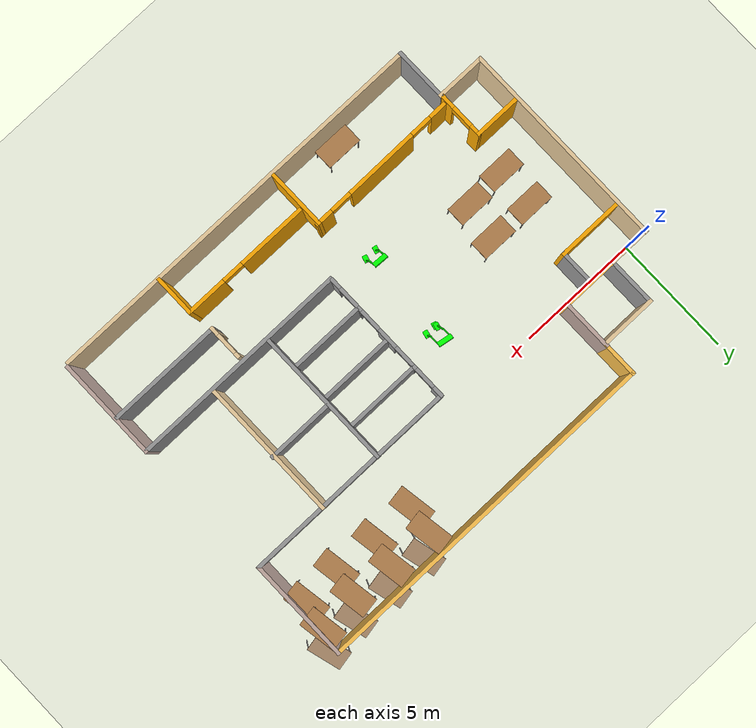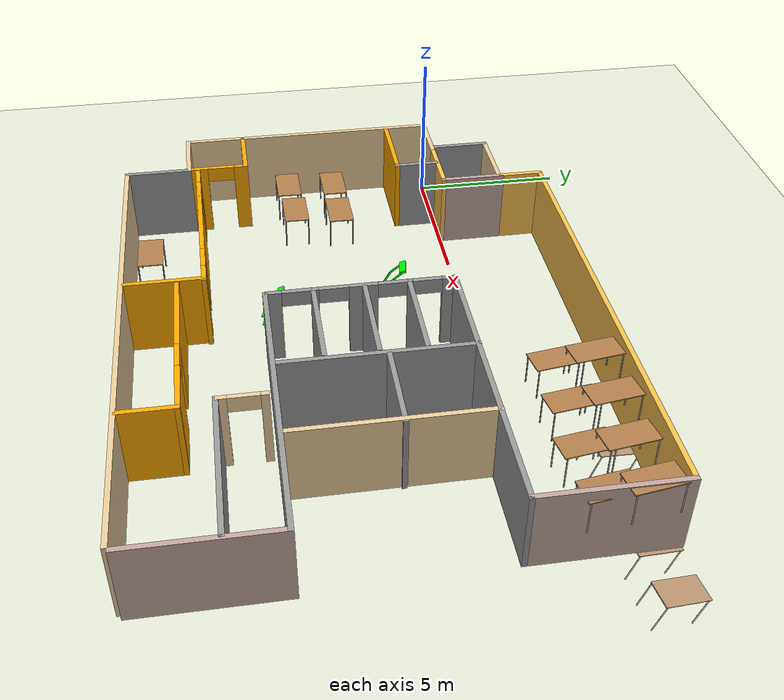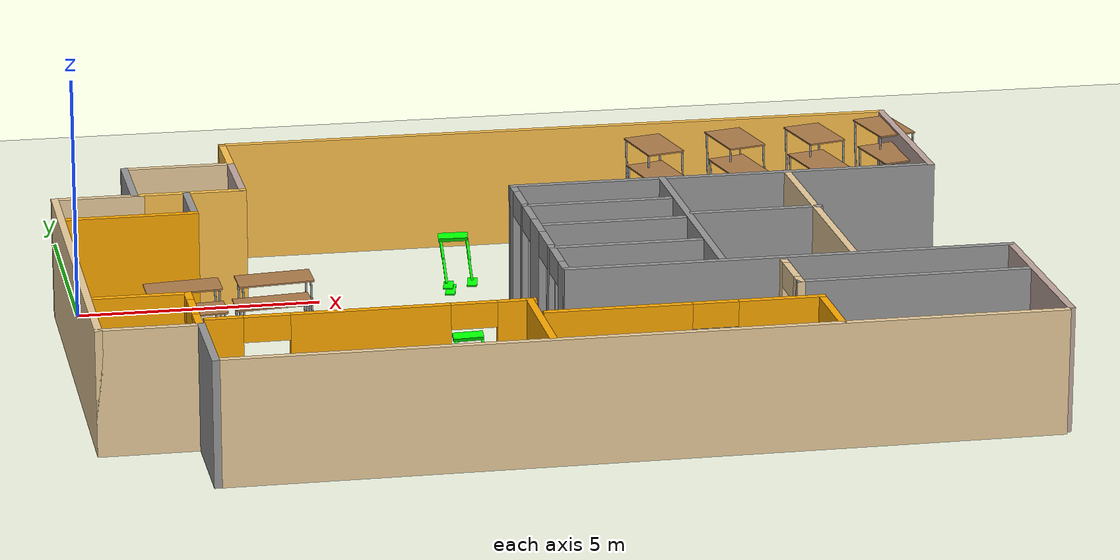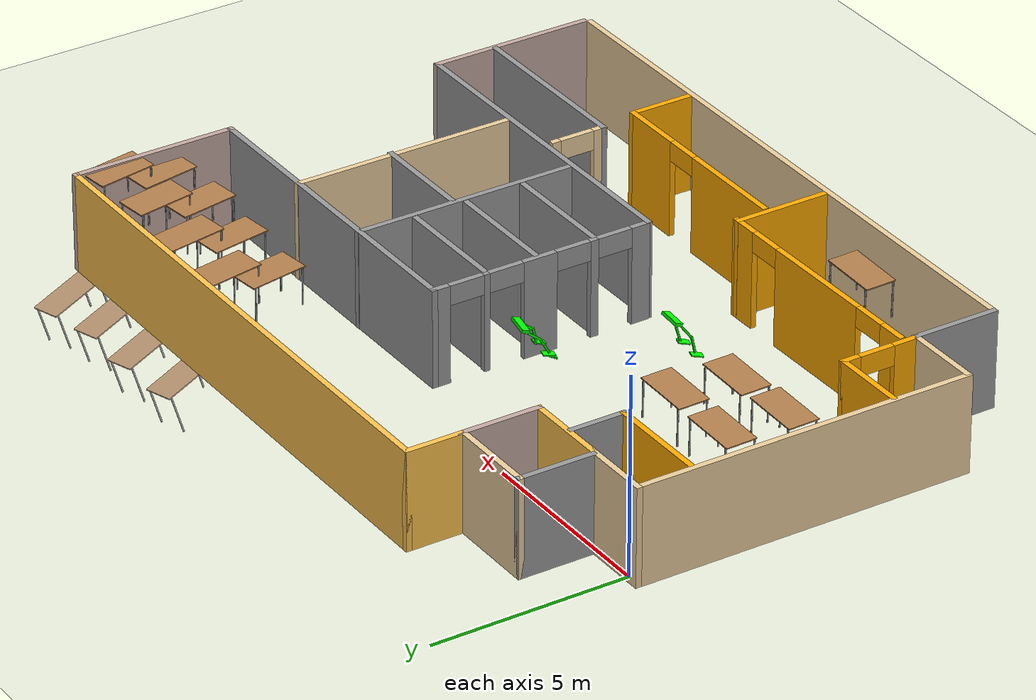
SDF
<sdf version="1.6">
 <world name="default">
  <plugin name="welcome_message" filename="libwelcome_message.so"/>
  <light name="sun" type="directional">
   <pose>0 0 10 0 -0 0</pose>
   <diffuse>0.8 0.8 0.8 1</diffuse>
   <specular>0.1 0.1 0.1 1</specular>
   <attenuation>
    <range>1000</range>
    <constant>0.9</constant>
    <linear>0.01</linear>
    <quadratic>0.001</quadratic>
   </attenuation>
   <direction>-0.5 0.5 -1</direction>
  </light>
  <model name="ground_plane">
   <static>1</static>
   <link name="link">
    <collision name="collision">
     <geometry><plane><normal>0 0 1</normal><size>100 100</size></plane></geometry>
     <surface><friction><ode><mu>100</mu><mu2>50</mu2></ode></friction></surface>
    </collision>
    <visual name="visual">
     <cast_shadows>0</cast_shadows>
     <geometry><plane><normal>0 0 1</normal><size>100 100</size></plane></geometry>
     <material>
      <script><uri>file://media/materials/scripts/gazebo.material</uri><name>Gazebo/Grey</name></script>
     </material>
    </visual>
   </link>
  </model>
  <gravity>0 0 -9.8</gravity>
  <magnetic_field>6e-06 2.3e-05 -4.2e-05</magnetic_field>
  <atmosphere type="adiabatic"/>
  <physics name="default_physics" default="0" type="ode">
   <max_step_size>0.001</max_step_size>
   <real_time_factor>1</real_time_factor>
   <real_time_update_rate>1000</real_time_update_rate>
  </physics>
  <scene><ambient>0.4 0.4 0.4 1</ambient><background>0.7 0.7 0.7 1</background><shadows>1</shadows></scene>
  <spherical_coordinates>
   <surface_model>EARTH_WGS84</surface_model>
   <latitude_deg>0</latitude_deg>
   <longitude_deg>0</longitude_deg>
   <elevation>0</elevation>
   <heading_deg>0</heading_deg>
  </spherical_coordinates>
  <model name="model">
   <link name="Wall_100">
    <pose>0.188472 0.1 0 0 0 -1.5708</pose>
    <visual name="Wall_100_Visual_8">
     <pose>1.96449 0 2.25 0 -0 0</pose>
     <geometry><box><size>0.9 0.15 0.5</size></box></geometry>
     <material>
      <script><uri>file://media/materials/scripts/gazebo.material</uri><name>Gazebo/Grey</name></script>
      <ambient>1 1 1 1</ambient>
      <shader type="pixel"/>
      <diffuse>0.7 0.7 0.7 1</diffuse>
      <specular>0.01 0.01 0.01 1</specular>
      <emissive>0 0 0 1</emissive>
     </material>
     <meta><layer>0</layer></meta>
    </visual>
    <visual name="Wall_100_Visual_0">
     <pose>-2.66165 0 1.25 0 -0 0</pose>
     <geometry><box><size>0.47671 0.15 2.5</size></box></geometry>
     <material>
      <script><uri>file://media/materials/scripts/gazebo.material</uri><name>Gazebo/Grey</name></script>
      <ambient>1 1 1 1</ambient>
      <shader type="pixel"/>
      <diffuse>0.7 0.7 0.7 1</diffuse>
      <specular>0.01 0.01 0.01 1</specular>
      <emissive>0 0 0 1</emissive>
     </material>
     <meta><layer>0</layer></meta>
    </visual>
    <visual name="Wall_100_Visual_1">
     <pose>-1.4503 0 1.25 0 -0 0</pose>
     <geometry><box><size>0.145974 0.15 2.5</size></box></geometry>
     <material>
      <script><uri>file://media/materials/scripts/gazebo.material</uri><name>Gazebo/Grey</name></script>
      <ambient>1 1 1 1</ambient>
      <shader type="pixel"/>
      <diffuse>0.7 0.7 0.7 1</diffuse>
      <specular>0.01 0.01 0.01 1</specular>
      <emissive>0 0 0 1</emissive>
     </material>
     <meta><layer>0</layer></meta>
    </visual>
    <visual name="Wall_100_Visual_2">
     <pose>-0.035162 0 1.25 0 -0 0</pose>
     <geometry><box><size>0.884308 0.15 2.5</size></box></geometry>
     <material>
      <script><uri>file://media/materials/scripts/gazebo.material</uri><name>Gazebo/Grey</name></script>
      <ambient>1 1 1 1</ambient>
      <shader type="pixel"/>
      <diffuse>0.7 0.7 0.7 1</diffuse>
      <specular>0.01 0.01 0.01 1</specular>
      <emissive>0 0 0 1</emissive>
     </material>
     <meta><layer>0</layer></meta>
    </visual>
    <visual name="Wall_100_Visual_3">
     <pose>1.41074 0 1.25 0 -0 0</pose>
     <geometry><box><size>0.207502 0.15 2.5</size></box></geometry>
     <material>
      <script><uri>file://media/materials/scripts/gazebo.material</uri><name>Gazebo/Grey</name></script>
      <ambient>1 1 1 1</ambient>
      <shader type="pixel"/>
      <diffuse>0.7 0.7 0.7 1</diffuse>
      <specular>0.01 0.01 0.01 1</specular>
      <emissive>0 0 0 1</emissive>
     </material>
     <meta><layer>0</layer></meta>
    </visual>
    <visual name="Wall_100_Visual_4">
     <pose>2.65725 0 1.25 0 -0 0</pose>
     <geometry><box><size>0.485506 0.15 2.5</size></box></geometry>
     <material>
      <script><uri>file://media/materials/scripts/gazebo.material</uri><name>Gazebo/Grey</name></script>
      <ambient>1 1 1 1</ambient>
      <shader type="pixel"/>
      <diffuse>0.7 0.7 0.7 1</diffuse>
      <specular>0.01 0.01 0.01 1</specular>
      <emissive>0 0 0 1</emissive>
     </material>
     <meta><layer>0</layer></meta>
    </visual>
    <visual name="Wall_100_Visual_5">
     <pose>-1.97329 0 2.25 0 -0 0</pose>
     <geometry><box><size>0.9 0.15 0.5</size></box></geometry>
     <material>
      <script><uri>file://media/materials/scripts/gazebo.material</uri><name>Gazebo/Grey</name></script>
      <ambient>1 1 1 1</ambient>
      <shader type="pixel"/>
      <diffuse>0.7 0.7 0.7 1</diffuse>
      <specular>0.01 0.01 0.01 1</specular>
      <emissive>0 0 0 1</emissive>
     </material>
     <meta><layer>0</layer></meta>
    </visual>
    <visual name="Wall_100_Visual_6">
     <pose>-0.927316 0 2.25 0 -0 0</pose>
     <geometry><box><size>0.9 0.15 0.5</size></box></geometry>
     <material>
      <script><uri>file://media/materials/scripts/gazebo.material</uri><name>Gazebo/Grey</name></script>
      <ambient>1 1 1 1</ambient>
      <shader type="pixel"/>
      <diffuse>0.7 0.7 0.7 1</diffuse>
      <specular>0.01 0.01 0.01 1</specular>
      <emissive>0 0 0 1</emissive>
     </material>
     <meta><layer>0</layer></meta>
    </visual>
    <visual name="Wall_100_Visual_7">
     <pose>0.856992 0 2.25 0 -0 0</pose>
     <geometry><box><size>0.9 0.15 0.5</size></box></geometry>
     <material>
      <script><uri>file://media/materials/scripts/gazebo.material</uri><name>Gazebo/Grey</name></script>
      <ambient>1 1 1 1</ambient>
      <shader type="pixel"/>
      <diffuse>0.7 0.7 0.7 1</diffuse>
      <specular>0.01 0.01 0.01 1</specular>
      <emissive>0 0 0 1</emissive>
     </material>
     <meta><layer>0</layer></meta>
    </visual>
    <collision name="Wall_100_Collision_0">
     <pose>-2.66165 0 1.25 0 -0 0</pose>
     <geometry><box><size>0.47671 0.15 2.5</size></box></geometry>
     <surface>
      <friction>
       <ode><mu>1</mu><mu2>1</mu2><fdir1>0 0 0</fdir1><slip1>0</slip1><slip2>0</slip2></ode>
       <torsional>
        <coefficient>1</coefficient>
        <patch_radius>0</patch_radius>
        <surface_radius>0</surface_radius>
        <use_patch_radius>1</use_patch_radius>
        <ode><slip>0</slip></ode>
       </torsional>
      </friction>
      <bounce><restitution_coefficient>0</restitution_coefficient><threshold>1e+06</threshold></bounce>
      <contact>
       <collide_without_contact>0</collide_without_contact>
       <collide_without_contact_bitmask>1</collide_without_contact_bitmask>
       <collide_bitmask>1</collide_bitmask>
       <ode>
        <soft_cfm>0</soft_cfm>
        <soft_erp>0.2</soft_erp>
        <kp>1e+13</kp>
        <kd>1</kd>
        <max_vel>0.01</max_vel>
        <min_depth>0</min_depth>
       </ode>
       <bullet>
        <split_impulse>1</split_impulse>
        <split_impulse_penetration_threshold>-0.01</split_impulse_penetration_threshold>
        <soft_cfm>0</soft_cfm>
        <soft_erp>0.2</soft_erp>
        <kp>1e+13</kp>
        <kd>1</kd>
       </bullet>
      </contact>
     </surface>
    </collision>
    <collision name="Wall_100_Collision_1">
     <pose>-1.4503 0 1.25 0 -0 0</pose>
     <geometry><box><size>0.145974 0.15 2.5</size></box></geometry>
     <surface>
      <friction>
       <ode><mu>1</mu><mu2>1</mu2><fdir1>0 0 0</fdir1><slip1>0</slip1><slip2>0</slip2></ode>
       <torsional>
        <coefficient>1</coefficient>
        <patch_radius>0</patch_radius>
        <surface_radius>0</surface_radius>
        <use_patch_radius>1</use_patch_radius>
        <ode><slip>0</slip></ode>
       </torsional>
      </friction>
      <bounce><restitution_coefficient>0</restitution_coefficient><threshold>1e+06</threshold></bounce>
      <contact>
       <collide_without_contact>0</collide_without_contact>
       <collide_without_contact_bitmask>1</collide_without_contact_bitmask>
       <collide_bitmask>1</collide_bitmask>
       <ode>
        <soft_cfm>0</soft_cfm>
        <soft_erp>0.2</soft_erp>
        <kp>1e+13</kp>
        <kd>1</kd>
        <max_vel>0.01</max_vel>
        <min_depth>0</min_depth>
       </ode>
       <bullet>
        <split_impulse>1</split_impulse>
        <split_impulse_penetration_threshold>-0.01</split_impulse_penetration_threshold>
        <soft_cfm>0</soft_cfm>
        <soft_erp>0.2</soft_erp>
        <kp>1e+13</kp>
        <kd>1</kd>
       </bullet>
      </contact>
     </surface>
    </collision>
    <collision name="Wall_100_Collision_2">
     <pose>-0.035162 0 1.25 0 -0 0</pose>
     <geometry><box><size>0.884308 0.15 2.5</size></box></geometry>
     <surface>
      <friction>
       <ode><mu>1</mu><mu2>1</mu2><fdir1>0 0 0</fdir1><slip1>0</slip1><slip2>0</slip2></ode>
       <torsional>
        <coefficient>1</coefficient>
        <patch_radius>0</patch_radius>
        <surface_radius>0</surface_radius>
        <use_patch_radius>1</use_patch_radius>
        <ode><slip>0</slip></ode>
       </torsional>
      </friction>
      <bounce><restitution_coefficient>0</restitution_coefficient><threshold>1e+06</threshold></bounce>
      <contact>
       <collide_without_contact>0</collide_without_contact>
       <collide_without_contact_bitmask>1</collide_without_contact_bitmask>
       <collide_bitmask>1</collide_bitmask>
       <ode>
        <soft_cfm>0</soft_cfm>
        <soft_erp>0.2</soft_erp>
        <kp>1e+13</kp>
        <kd>1</kd>
        <max_vel>0.01</max_vel>
        <min_depth>0</min_depth>
       </ode>
       <bullet>
        <split_impulse>1</split_impulse>
        <split_impulse_penetration_threshold>-0.01</split_impulse_penetration_threshold>
        <soft_cfm>0</soft_cfm>
        <soft_erp>0.2</soft_erp>
        <kp>1e+13</kp>
        <kd>1</kd>
       </bullet>
      </contact>
     </surface>
    </collision>
    <collision name="Wall_100_Collision_3">
     <pose>1.41074 0 1.25 0 -0 0</pose>
     <geometry><box><size>0.207502 0.15 2.5</size></box></geometry>
     <surface>
      <friction>
       <ode><mu>1</mu><mu2>1</mu2><fdir1>0 0 0</fdir1><slip1>0</slip1><slip2>0</slip2></ode>
       <torsional>
        <coefficient>1</coefficient>
        <patch_radius>0</patch_radius>
        <surface_radius>0</surface_radius>
        <use_patch_radius>1</use_patch_radius>
        <ode><slip>0</slip></ode>
       </torsional>
      </friction>
      <bounce><restitution_coefficient>0</restitution_coefficient><threshold>1e+06</threshold></bounce>
      <contact>
       <collide_without_contact>0</collide_without_contact>
       <collide_without_contact_bitmask>1</collide_without_contact_bitmask>
       <collide_bitmask>1</collide_bitmask>
       <ode>
        <soft_cfm>0</soft_cfm>
        <soft_erp>0.2</soft_erp>
        <kp>1e+13</kp>
        <kd>1</kd>
        <max_vel>0.01</max_vel>
        <min_depth>0</min_depth>
       </ode>
       <bullet>
        <split_impulse>1</split_impulse>
        <split_impulse_penetration_threshold>-0.01</split_impulse_penetration_threshold>
        <soft_cfm>0</soft_cfm>
        <soft_erp>0.2</soft_erp>
        <kp>1e+13</kp>
        <kd>1</kd>
       </bullet>
      </contact>
     </surface>
    </collision>
    <collision name="Wall_100_Collision_5">
     <pose>-1.97329 0 2.25 0 -0 0</pose>
     <geometry><box><size>0.9 0.15 0.5</size></box></geometry>
     <surface>
      <friction>
       <ode><mu>1</mu><mu2>1</mu2><fdir1>0 0 0</fdir1><slip1>0</slip1><slip2>0</slip2></ode>
       <torsional>
        <coefficient>1</coefficient>
        <patch_radius>0</patch_radius>
        <surface_radius>0</surface_radius>
        <use_patch_radius>1</use_patch_radius>
        <ode><slip>0</slip></ode>
       </torsional>
      </friction>
      <bounce><restitution_coefficient>0</restitution_coefficient><threshold>1e+06</threshold></bounce>
      <contact>
       <collide_without_contact>0</collide_without_contact>
       <collide_without_contact_bitmask>1</collide_without_contact_bitmask>
       <collide_bitmask>1</collide_bitmask>
       <ode>
        <soft_cfm>0</soft_cfm>
        <soft_erp>0.2</soft_erp>
        <kp>1e+13</kp>
        <kd>1</kd>
        <max_vel>0.01</max_vel>
        <min_depth>0</min_depth>
       </ode>
       <bullet>
        <split_impulse>1</split_impulse>
        <split_impulse_penetration_threshold>-0.01</split_impulse_penetration_threshold>
        <soft_cfm>0</soft_cfm>
        <soft_erp>0.2</soft_erp>
        <kp>1e+13</kp>
        <kd>1</kd>
       </bullet>
      </contact>
     </surface>
    </collision>
    <collision name="Wall_100_Collision_4">
     <pose>2.65725 0 1.25 0 -0 0</pose>
     <geometry><box><size>0.485506 0.15 2.5</size></box></geometry>
     <surface>
      <friction>
       <ode><mu>1</mu><mu2>1</mu2><fdir1>0 0 0</fdir1><slip1>0</slip1><slip2>0</slip2></ode>
       <torsional>
        <coefficient>1</coefficient>
        <patch_radius>0</patch_radius>
        <surface_radius>0</surface_radius>
        <use_patch_radius>1</use_patch_radius>
        <ode><slip>0</slip></ode>
       </torsional>
      </friction>
      <bounce><restitution_coefficient>0</restitution_coefficient><threshold>1e+06</threshold></bounce>
      <contact>
       <collide_without_contact>0</collide_without_contact>
       <collide_without_contact_bitmask>1</collide_without_contact_bitmask>
       <collide_bitmask>1</collide_bitmask>
       <ode>
        <soft_cfm>0</soft_cfm>
        <soft_erp>0.2</soft_erp>
        <kp>1e+13</kp>
        <kd>1</kd>
        <max_vel>0.01</max_vel>
        <min_depth>0</min_depth>
       </ode>
       <bullet>
        <split_impulse>1</split_impulse>
        <split_impulse_penetration_threshold>-0.01</split_impulse_penetration_threshold>
        <soft_cfm>0</soft_cfm>
        <soft_erp>0.2</soft_erp>
        <kp>1e+13</kp>
        <kd>1</kd>
       </bullet>
      </contact>
     </surface>
    </collision>
    <collision name="Wall_100_Collision_6">
     <pose>-0.927316 0 2.25 0 -0 0</pose>
     <geometry><box><size>0.9 0.15 0.5</size></box></geometry>
     <surface>
      <friction>
       <ode><mu>1</mu><mu2>1</mu2><fdir1>0 0 0</fdir1><slip1>0</slip1><slip2>0</slip2></ode>
       <torsional>
        <coefficient>1</coefficient>
        <patch_radius>0</patch_radius>
        <surface_radius>0</surface_radius>
        <use_patch_radius>1</use_patch_radius>
        <ode><slip>0</slip></ode>
       </torsional>
      </friction>
      <bounce><restitution_coefficient>0</restitution_coefficient><threshold>1e+06</threshold></bounce>
      <contact>
       <collide_without_contact>0</collide_without_contact>
       <collide_without_contact_bitmask>1</collide_without_contact_bitmask>
       <collide_bitmask>1</collide_bitmask>
       <ode>
        <soft_cfm>0</soft_cfm>
        <soft_erp>0.2</soft_erp>
        <kp>1e+13</kp>
        <kd>1</kd>
        <max_vel>0.01</max_vel>
        <min_depth>0</min_depth>
       </ode>
       <bullet>
        <split_impulse>1</split_impulse>
        <split_impulse_penetration_threshold>-0.01</split_impulse_penetration_threshold>
        <soft_cfm>0</soft_cfm>
        <soft_erp>0.2</soft_erp>
        <kp>1e+13</kp>
        <kd>1</kd>
       </bullet>
      </contact>
     </surface>
    </collision>
    <collision name="Wall_100_Collision_7">
     <pose>0.856992 0 2.25 0 -0 0</pose>
     <geometry><box><size>0.9 0.15 0.5</size></box></geometry>
     <surface>
      <friction>
       <ode><mu>1</mu><mu2>1</mu2><fdir1>0 0 0</fdir1><slip1>0</slip1><slip2>0</slip2></ode>
       <torsional>
        <coefficient>1</coefficient>
        <patch_radius>0</patch_radius>
        <surface_radius>0</surface_radius>
        <use_patch_radius>1</use_patch_radius>
        <ode><slip>0</slip></ode>
       </torsional>
      </friction>
      <bounce><restitution_coefficient>0</restitution_coefficient><threshold>1e+06</threshold></bounce>
      <contact>
       <collide_without_contact>0</collide_without_contact>
       <collide_without_contact_bitmask>1</collide_without_contact_bitmask>
       <collide_bitmask>1</collide_bitmask>
       <ode>
        <soft_cfm>0</soft_cfm>
        <soft_erp>0.2</soft_erp>
        <kp>1e+13</kp>
        <kd>1</kd>
        <max_vel>0.01</max_vel>
        <min_depth>0</min_depth>
       </ode>
       <bullet>
        <split_impulse>1</split_impulse>
        <split_impulse_penetration_threshold>-0.01</split_impulse_penetration_threshold>
        <soft_cfm>0</soft_cfm>
        <soft_erp>0.2</soft_erp>
        <kp>1e+13</kp>
        <kd>1</kd>
       </bullet>
      </contact>
     </surface>
    </collision>
    <collision name="Wall_100_Collision_8">
     <pose>1.96449 0 2.25 0 -0 0</pose>
     <geometry><box><size>0.9 0.15 0.5</size></box></geometry>
     <surface>
      <friction>
       <ode><mu>1</mu><mu2>1</mu2><fdir1>0 0 0</fdir1><slip1>0</slip1><slip2>0</slip2></ode>
       <torsional>
        <coefficient>1</coefficient>
        <patch_radius>0</patch_radius>
        <surface_radius>0</surface_radius>
        <use_patch_radius>1</use_patch_radius>
        <ode><slip>0</slip></ode>
       </torsional>
      </friction>
      <bounce><restitution_coefficient>0</restitution_coefficient><threshold>1e+06</threshold></bounce>
      <contact>
       <collide_without_contact>0</collide_without_contact>
       <collide_without_contact_bitmask>1</collide_without_contact_bitmask>
       <collide_bitmask>1</collide_bitmask>
       <ode>
        <soft_cfm>0</soft_cfm>
        <soft_erp>0.2</soft_erp>
        <kp>1e+13</kp>
        <kd>1</kd>
        <max_vel>0.01</max_vel>
        <min_depth>0</min_depth>
       </ode>
       <bullet>
        <split_impulse>1</split_impulse>
        <split_impulse_penetration_threshold>-0.01</split_impulse_penetration_threshold>
        <soft_cfm>0</soft_cfm>
        <soft_erp>0.2</soft_erp>
        <kp>1e+13</kp>
        <kd>1</kd>
       </bullet>
      </contact>
     </surface>
    </collision>
   </link>
   <link name="Wall_102">
    <pose>1.73212 1.51954 0 0 -0 0</pose>
    <visual name="Wall_102_Visual">
     <pose>0 0 1.25 0 -0 0</pose>
     <geometry><box><size>3 0.15 2.5</size></box></geometry>
     <material>
      <script><uri>file://media/materials/scripts/gazebo.material</uri><name>Gazebo/Grey</name></script>
      <ambient>1 1 1 1</ambient>
      <shader type="pixel"/>
      <diffuse>0.7 0.7 0.7 1</diffuse>
      <specular>0.01 0.01 0.01 1</specular>
      <emissive>0 0 0 1</emissive>
     </material>
     <meta><layer>0</layer></meta>
    </visual>
    <collision name="Wall_102_Collision">
     <pose>0 0 1.25 0 -0 0</pose>
     <geometry><box><size>3 0.15 2.5</size></box></geometry>
     <surface>
      <friction>
       <ode><mu>1</mu><mu2>1</mu2><fdir1>0 0 0</fdir1><slip1>0</slip1><slip2>0</slip2></ode>
       <torsional>
        <coefficient>1</coefficient>
        <patch_radius>0</patch_radius>
        <surface_radius>0</surface_radius>
        <use_patch_radius>1</use_patch_radius>
        <ode><slip>0</slip></ode>
       </torsional>
      </friction>
      <bounce><restitution_coefficient>0</restitution_coefficient><threshold>1e+06</threshold></bounce>
      <contact>
       <collide_without_contact>0</collide_without_contact>
       <collide_without_contact_bitmask>1</collide_without_contact_bitmask>
       <collide_bitmask>1</collide_bitmask>
       <ode>
        <soft_cfm>0</soft_cfm>
        <soft_erp>0.2</soft_erp>
        <kp>1e+13</kp>
        <kd>1</kd>
        <max_vel>0.01</max_vel>
        <min_depth>0</min_depth>
       </ode>
       <bullet>
        <split_impulse>1</split_impulse>
        <split_impulse_penetration_threshold>-0.01</split_impulse_penetration_threshold>
        <soft_cfm>0</soft_cfm>
        <soft_erp>0.2</soft_erp>
        <kp>1e+13</kp>
        <kd>1</kd>
       </bullet>
      </contact>
     </surface>
    </collision>
   </link>
   <link name="Wall_104">
    <pose>1.73212 0.165926 0 0 -0 0</pose>
    <visual name="Wall_104_Visual">
     <pose>0 0 1.25 0 -0 0</pose>
     <geometry><box><size>3 0.15 2.5</size></box></geometry>
     <material>
      <script><uri>file://media/materials/scripts/gazebo.material</uri><name>Gazebo/Grey</name></script>
      <ambient>1 1 1 1</ambient>
      <shader type="pixel"/>
      <diffuse>0.7 0.7 0.7 1</diffuse>
      <specular>0.01 0.01 0.01 1</specular>
      <emissive>0 0 0 1</emissive>
     </material>
     <meta><layer>0</layer></meta>
    </visual>
    <collision name="Wall_104_Collision">
     <pose>0 0 1.25 0 -0 0</pose>
     <geometry><box><size>3 0.15 2.5</size></box></geometry>
     <surface>
      <friction>
       <ode><mu>1</mu><mu2>1</mu2><fdir1>0 0 0</fdir1><slip1>0</slip1><slip2>0</slip2></ode>
       <torsional>
        <coefficient>1</coefficient>
        <patch_radius>0</patch_radius>
        <surface_radius>0</surface_radius>
        <use_patch_radius>1</use_patch_radius>
        <ode><slip>0</slip></ode>
       </torsional>
      </friction>
      <bounce><restitution_coefficient>0</restitution_coefficient><threshold>1e+06</threshold></bounce>
      <contact>
       <collide_without_contact>0</collide_without_contact>
       <collide_without_contact_bitmask>1</collide_without_contact_bitmask>
       <collide_bitmask>1</collide_bitmask>
       <ode>
        <soft_cfm>0</soft_cfm>
        <soft_erp>0.2</soft_erp>
        <kp>1e+13</kp>
        <kd>1</kd>
        <max_vel>0.01</max_vel>
        <min_depth>0</min_depth>
       </ode>
       <bullet>
        <split_impulse>1</split_impulse>
        <split_impulse_penetration_threshold>-0.01</split_impulse_penetration_threshold>
        <soft_cfm>0</soft_cfm>
        <soft_erp>0.2</soft_erp>
        <kp>1e+13</kp>
        <kd>1</kd>
       </bullet>
      </contact>
     </surface>
    </collision>
   </link>
   <link name="Wall_106">
    <pose>1.73212 -1.37227 0 0 -0 0</pose>
    <visual name="Wall_106_Visual">
     <pose>0 0 1.25 0 -0 0</pose>
     <geometry><box><size>3 0.15 2.5</size></box></geometry>
     <material>
      <script><uri>file://media/materials/scripts/gazebo.material</uri><name>Gazebo/Grey</name></script>
      <ambient>1 1 1 1</ambient>
      <shader type="pixel"/>
      <diffuse>0.7 0.7 0.7 1</diffuse>
      <specular>0.01 0.01 0.01 1</specular>
      <emissive>0 0 0 1</emissive>
     </material>
     <meta><layer>0</layer></meta>
    </visual>
    <collision name="Wall_106_Collision">
     <pose>0 0 1.25 0 -0 0</pose>
     <geometry><box><size>3 0.15 2.5</size></box></geometry>
     <surface>
      <friction>
       <ode><mu>1</mu><mu2>1</mu2><fdir1>0 0 0</fdir1><slip1>0</slip1><slip2>0</slip2></ode>
       <torsional>
        <coefficient>1</coefficient>
        <patch_radius>0</patch_radius>
        <surface_radius>0</surface_radius>
        <use_patch_radius>1</use_patch_radius>
        <ode><slip>0</slip></ode>
       </torsional>
      </friction>
      <bounce><restitution_coefficient>0</restitution_coefficient><threshold>1e+06</threshold></bounce>
      <contact>
       <collide_without_contact>0</collide_without_contact>
       <collide_without_contact_bitmask>1</collide_without_contact_bitmask>
       <collide_bitmask>1</collide_bitmask>
       <ode>
        <soft_cfm>0</soft_cfm>
        <soft_erp>0.2</soft_erp>
        <kp>1e+13</kp>
        <kd>1</kd>
        <max_vel>0.01</max_vel>
        <min_depth>0</min_depth>
       </ode>
       <bullet>
        <split_impulse>1</split_impulse>
        <split_impulse_penetration_threshold>-0.01</split_impulse_penetration_threshold>
        <soft_cfm>0</soft_cfm>
        <soft_erp>0.2</soft_erp>
        <kp>1e+13</kp>
        <kd>1</kd>
       </bullet>
      </contact>
     </surface>
    </collision>
   </link>
   <link name="Wall_108">
    <pose>-5.31153 6.35 0 0 0 -1.5708</pose>
    <visual name="Wall_108_Visual">
     <pose>0 0 1.25 0 -0 0</pose>
     <geometry><box><size>1.5 0.15 2.5</size></box></geometry>
     <material>
      <script><uri>file://media/materials/scripts/gazebo.material</uri><name>Gazebo/Grey</name></script>
      <ambient>1 0.764706 0.305882 1</ambient>
      <shader type="pixel"/>
      <diffuse>0.7 0.7 0.7 1</diffuse>
      <specular>0.01 0.01 0.01 1</specular>
      <emissive>0 0 0 1</emissive>
     </material>
     <meta><layer>0</layer></meta>
    </visual>
    <collision name="Wall_108_Collision">
     <pose>0 0 1.25 0 -0 0</pose>
     <geometry><box><size>1.5 0.15 2.5</size></box></geometry>
     <surface>
      <friction>
       <ode><mu>1</mu><mu2>1</mu2><fdir1>0 0 0</fdir1><slip1>0</slip1><slip2>0</slip2></ode>
       <torsional>
        <coefficient>1</coefficient>
        <patch_radius>0</patch_radius>
        <surface_radius>0</surface_radius>
        <use_patch_radius>1</use_patch_radius>
        <ode><slip>0</slip></ode>
       </torsional>
      </friction>
      <bounce><restitution_coefficient>0</restitution_coefficient><threshold>1e+06</threshold></bounce>
      <contact>
       <collide_without_contact>0</collide_without_contact>
       <collide_without_contact_bitmask>1</collide_without_contact_bitmask>
       <collide_bitmask>1</collide_bitmask>
       <ode>
        <soft_cfm>0</soft_cfm>
        <soft_erp>0.2</soft_erp>
        <kp>1e+13</kp>
        <kd>1</kd>
        <max_vel>0.01</max_vel>
        <min_depth>0</min_depth>
       </ode>
       <bullet>
        <split_impulse>1</split_impulse>
        <split_impulse_penetration_threshold>-0.01</split_impulse_penetration_threshold>
        <soft_cfm>0</soft_cfm>
        <soft_erp>0.2</soft_erp>
        <kp>1e+13</kp>
        <kd>1</kd>
       </bullet>
      </contact>
     </surface>
    </collision>
   </link>
   <link name="Wall_109">
    <pose>-5.31153 4.675 0 0 0 -1.5708</pose>
    <visual name="Wall_109_Visual">
     <pose>0 0 1.25 0 -0 0</pose>
     <geometry><box><size>2.15 0.15 2.5</size></box></geometry>
     <material>
      <script><uri>file://media/materials/scripts/gazebo.material</uri><name>Gazebo/Grey</name></script>
      <ambient>0.760784 0.662745 0.627451 1</ambient>
      <shader type="pixel"/>
      <diffuse>0.7 0.7 0.7 1</diffuse>
      <specular>0.01 0.01 0.01 1</specular>
      <emissive>0 0 0 1</emissive>
     </material>
     <meta><layer>0</layer></meta>
    </visual>
    <collision name="Wall_109_Collision">
     <pose>0 0 1.25 0 -0 0</pose>
     <geometry><box><size>2.15 0.15 2.5</size></box></geometry>
     <surface>
      <friction>
       <ode><mu>1</mu><mu2>1</mu2><fdir1>0 0 0</fdir1><slip1>0</slip1><slip2>0</slip2></ode>
       <torsional>
        <coefficient>1</coefficient>
        <patch_radius>0</patch_radius>
        <surface_radius>0</surface_radius>
        <use_patch_radius>1</use_patch_radius>
        <ode><slip>0</slip></ode>
       </torsional>
      </friction>
      <bounce><restitution_coefficient>0</restitution_coefficient><threshold>1e+06</threshold></bounce>
      <contact>
       <collide_without_contact>0</collide_without_contact>
       <collide_without_contact_bitmask>1</collide_without_contact_bitmask>
       <collide_bitmask>1</collide_bitmask>
       <ode>
        <soft_cfm>0</soft_cfm>
        <soft_erp>0.2</soft_erp>
        <kp>1e+13</kp>
        <kd>1</kd>
        <max_vel>0.01</max_vel>
        <min_depth>0</min_depth>
       </ode>
       <bullet>
        <split_impulse>1</split_impulse>
        <split_impulse_penetration_threshold>-0.01</split_impulse_penetration_threshold>
        <soft_cfm>0</soft_cfm>
        <soft_erp>0.2</soft_erp>
        <kp>1e+13</kp>
        <kd>1</kd>
       </bullet>
      </contact>
     </surface>
    </collision>
   </link>
   <link name="Wall_113">
    <pose>-6.36153 3.675 0 0 -0 3.14159</pose>
    <visual name="Wall_113_Visual">
     <pose>0 0 1.25 0 -0 0</pose>
     <geometry><box><size>2.25 0.15 2.5</size></box></geometry>
     <material>
      <script><uri>file://media/materials/scripts/gazebo.material</uri><name>Gazebo/Grey</name></script>
      <ambient>1 0.764706 0.305882 1</ambient>
      <shader type="pixel"/>
      <diffuse>0.7 0.7 0.7 1</diffuse>
      <specular>0.01 0.01 0.01 1</specular>
      <emissive>0 0 0 1</emissive>
     </material>
     <meta><layer>0</layer></meta>
    </visual>
    <collision name="Wall_113_Collision">
     <pose>0 0 1.25 0 -0 0</pose>
     <geometry><box><size>2.25 0.15 2.5</size></box></geometry>
     <surface>
      <friction>
       <ode><mu>1</mu><mu2>1</mu2><fdir1>0 0 0</fdir1><slip1>0</slip1><slip2>0</slip2></ode>
       <torsional>
        <coefficient>1</coefficient>
        <patch_radius>0</patch_radius>
        <surface_radius>0</surface_radius>
        <use_patch_radius>1</use_patch_radius>
        <ode><slip>0</slip></ode>
       </torsional>
      </friction>
      <bounce><restitution_coefficient>0</restitution_coefficient><threshold>1e+06</threshold></bounce>
      <contact>
       <collide_without_contact>0</collide_without_contact>
       <collide_without_contact_bitmask>1</collide_without_contact_bitmask>
       <collide_bitmask>1</collide_bitmask>
       <ode>
        <soft_cfm>0</soft_cfm>
        <soft_erp>0.2</soft_erp>
        <kp>1e+13</kp>
        <kd>1</kd>
        <max_vel>0.01</max_vel>
        <min_depth>0</min_depth>
       </ode>
       <bullet>
        <split_impulse>1</split_impulse>
        <split_impulse_penetration_threshold>-0.01</split_impulse_penetration_threshold>
        <soft_cfm>0</soft_cfm>
        <soft_erp>0.2</soft_erp>
        <kp>1e+13</kp>
        <kd>1</kd>
       </bullet>
      </contact>
     </surface>
    </collision>
   </link>
   <link name="Wall_114">
    <pose>-8.28653 3.675 0 0 -0 3.14159</pose>
    <visual name="Wall_114_Visual">
     <pose>0 0 1.25 0 -0 0</pose>
     <geometry><box><size>1.9 0.15 2.5</size></box></geometry>
     <material>
      <script><uri>file://media/materials/scripts/gazebo.material</uri><name>Gazebo/Grey</name></script>
      <ambient>0.921569 0.807843 0.615686 1</ambient>
      <shader type="pixel"/>
      <diffuse>0.7 0.7 0.7 1</diffuse>
      <specular>0.01 0.01 0.01 1</specular>
      <emissive>0 0 0 1</emissive>
     </material>
     <meta><layer>0</layer></meta>
    </visual>
    <collision name="Wall_114_Collision">
     <pose>0 0 1.25 0 -0 0</pose>
     <geometry><box><size>1.9 0.15 2.5</size></box></geometry>
     <surface>
      <friction>
       <ode><mu>1</mu><mu2>1</mu2><fdir1>0 0 0</fdir1><slip1>0</slip1><slip2>0</slip2></ode>
       <torsional>
        <coefficient>1</coefficient>
        <patch_radius>0</patch_radius>
        <surface_radius>0</surface_radius>
        <use_patch_radius>1</use_patch_radius>
        <ode><slip>0</slip></ode>
       </torsional>
      </friction>
      <bounce><restitution_coefficient>0</restitution_coefficient><threshold>1e+06</threshold></bounce>
      <contact>
       <collide_without_contact>0</collide_without_contact>
       <collide_without_contact_bitmask>1</collide_without_contact_bitmask>
       <collide_bitmask>1</collide_bitmask>
       <ode>
        <soft_cfm>0</soft_cfm>
        <soft_erp>0.2</soft_erp>
        <kp>1e+13</kp>
        <kd>1</kd>
        <max_vel>0.01</max_vel>
        <min_depth>0</min_depth>
       </ode>
       <bullet>
        <split_impulse>1</split_impulse>
        <split_impulse_penetration_threshold>-0.01</split_impulse_penetration_threshold>
        <soft_cfm>0</soft_cfm>
        <soft_erp>0.2</soft_erp>
        <kp>1e+13</kp>
        <kd>1</kd>
       </bullet>
      </contact>
     </surface>
    </collision>
   </link>
   <link name="Wall_13">
    <pose>1.86347 7.025 0 0 -0 0</pose>
    <visual name="Wall_13_Visual">
     <pose>0 0 1.25 0 -0 0</pose>
     <geometry><box><size>14.5 0.15 2.5</size></box></geometry>
     <material>
      <script><uri>file://media/materials/scripts/gazebo.material</uri><name>Gazebo/Grey</name></script>
      <ambient>1 0.764706 0.305882 1</ambient>
      <shader type="pixel"/>
      <diffuse>0.7 0.7 0.7 1</diffuse>
      <specular>0.01 0.01 0.01 1</specular>
      <emissive>0 0 0 1</emissive>
     </material>
     <meta><layer>0</layer></meta>
    </visual>
    <collision name="Wall_13_Collision">
     <pose>0 0 1.25 0 -0 0</pose>
     <geometry><box><size>14.5 0.15 2.5</size></box></geometry>
     <surface>
      <friction>
       <ode><mu>1</mu><mu2>1</mu2><fdir1>0 0 0</fdir1><slip1>0</slip1><slip2>0</slip2></ode>
       <torsional>
        <coefficient>1</coefficient>
        <patch_radius>0</patch_radius>
        <surface_radius>0</surface_radius>
        <use_patch_radius>1</use_patch_radius>
        <ode><slip>0</slip></ode>
       </torsional>
      </friction>
      <bounce><restitution_coefficient>0</restitution_coefficient><threshold>1e+06</threshold></bounce>
      <contact>
       <collide_without_contact>0</collide_without_contact>
       <collide_without_contact_bitmask>1</collide_without_contact_bitmask>
       <collide_bitmask>1</collide_bitmask>
       <ode>
        <soft_cfm>0</soft_cfm>
        <soft_erp>0.2</soft_erp>
        <kp>1e+13</kp>
        <kd>1</kd>
        <max_vel>0.01</max_vel>
        <min_depth>0</min_depth>
       </ode>
       <bullet>
        <split_impulse>1</split_impulse>
        <split_impulse_penetration_threshold>-0.01</split_impulse_penetration_threshold>
        <soft_cfm>0</soft_cfm>
        <soft_erp>0.2</soft_erp>
        <kp>1e+13</kp>
        <kd>1</kd>
       </bullet>
      </contact>
     </surface>
    </collision>
   </link>
   <link name="Wall_15">
    <pose>-7.53411 4.67076 0 0 -0 1.5708</pose>
    <visual name="Wall_15_Visual">
     <pose>0 0 1.25 0 -0 0</pose>
     <geometry><box><size>2 0.15 2.5</size></box></geometry>
     <material>
      <script><uri>file://media/materials/scripts/gazebo.material</uri><name>Gazebo/Grey</name></script>
      <ambient>1 1 1 1</ambient>
      <shader type="pixel"/>
      <diffuse>0.7 0.7 0.7 1</diffuse>
      <specular>0.01 0.01 0.01 1</specular>
      <emissive>0 0 0 1</emissive>
     </material>
     <meta><layer>0</layer></meta>
    </visual>
    <collision name="Wall_15_Collision">
     <pose>0 0 1.25 0 -0 0</pose>
     <geometry><box><size>2 0.15 2.5</size></box></geometry>
     <surface>
      <friction>
       <ode><mu>1</mu><mu2>1</mu2><fdir1>0 0 0</fdir1><slip1>0</slip1><slip2>0</slip2></ode>
       <torsional>
        <coefficient>1</coefficient>
        <patch_radius>0</patch_radius>
        <surface_radius>0</surface_radius>
        <use_patch_radius>1</use_patch_radius>
        <ode><slip>0</slip></ode>
       </torsional>
      </friction>
      <bounce><restitution_coefficient>0</restitution_coefficient><threshold>1e+06</threshold></bounce>
      <contact>
       <collide_without_contact>0</collide_without_contact>
       <collide_without_contact_bitmask>1</collide_without_contact_bitmask>
       <collide_bitmask>1</collide_bitmask>
       <ode>
        <soft_cfm>0</soft_cfm>
        <soft_erp>0.2</soft_erp>
        <kp>1e+13</kp>
        <kd>1</kd>
        <max_vel>0.01</max_vel>
        <min_depth>0</min_depth>
       </ode>
       <bullet>
        <split_impulse>1</split_impulse>
        <split_impulse_penetration_threshold>-0.01</split_impulse_penetration_threshold>
        <soft_cfm>0</soft_cfm>
        <soft_erp>0.2</soft_erp>
        <kp>1e+13</kp>
        <kd>1</kd>
       </bullet>
      </contact>
     </surface>
    </collision>
   </link>
   <link name="Wall_16">
    <pose>-6.48412 5.59576 0 0 -0 0</pose>
    <visual name="Wall_16_Visual">
     <pose>0 0 1.25 0 -0 0</pose>
     <geometry><box><size>2.25 0.15 2.5</size></box></geometry>
     <material>
      <script><uri>file://media/materials/scripts/gazebo.material</uri><name>Gazebo/Grey</name></script>
      <ambient>0.921569 0.807843 0.615686 1</ambient>
      <shader type="pixel"/>
      <diffuse>0.7 0.7 0.7 1</diffuse>
      <specular>0.01 0.01 0.01 1</specular>
      <emissive>0 0 0 1</emissive>
     </material>
     <meta><layer>0</layer></meta>
    </visual>
    <collision name="Wall_16_Collision">
     <pose>0 0 1.25 0 -0 0</pose>
     <geometry><box><size>2.25 0.15 2.5</size></box></geometry>
     <surface>
      <friction>
       <ode><mu>1</mu><mu2>1</mu2><fdir1>0 0 0</fdir1><slip1>0</slip1><slip2>0</slip2></ode>
       <torsional>
        <coefficient>1</coefficient>
        <patch_radius>0</patch_radius>
        <surface_radius>0</surface_radius>
        <use_patch_radius>1</use_patch_radius>
        <ode><slip>0</slip></ode>
       </torsional>
      </friction>
      <bounce><restitution_coefficient>0</restitution_coefficient><threshold>1e+06</threshold></bounce>
      <contact>
       <collide_without_contact>0</collide_without_contact>
       <collide_without_contact_bitmask>1</collide_without_contact_bitmask>
       <collide_bitmask>1</collide_bitmask>
       <ode>
        <soft_cfm>0</soft_cfm>
        <soft_erp>0.2</soft_erp>
        <kp>1e+13</kp>
        <kd>1</kd>
        <max_vel>0.01</max_vel>
        <min_depth>0</min_depth>
       </ode>
       <bullet>
        <split_impulse>1</split_impulse>
        <split_impulse_penetration_threshold>-0.01</split_impulse_penetration_threshold>
        <soft_cfm>0</soft_cfm>
        <soft_erp>0.2</soft_erp>
        <kp>1e+13</kp>
        <kd>1</kd>
       </bullet>
      </contact>
     </surface>
    </collision>
   </link>
   <link name="Wall_18">
    <pose>-6.47276 2.92924 0 0 0 -1.5708</pose>
    <visual name="Wall_18_Visual">
     <pose>0 0 1.25 0 -0 0</pose>
     <geometry><box><size>1.5 0.15 2.5</size></box></geometry>
     <material>
      <script><uri>file://media/materials/scripts/gazebo.material</uri><name>Gazebo/Grey</name></script>
      <ambient>1 1 1 1</ambient>
      <shader type="pixel"/>
      <diffuse>0.7 0.7 0.7 1</diffuse>
      <specular>0.01 0.01 0.01 1</specular>
      <emissive>0 0 0 1</emissive>
     </material>
     <meta><layer>0</layer></meta>
    </visual>
    <collision name="Wall_18_Collision">
     <pose>0 0 1.25 0 -0 0</pose>
     <geometry><box><size>1.5 0.15 2.5</size></box></geometry>
     <surface>
      <friction>
       <ode><mu>1</mu><mu2>1</mu2><fdir1>0 0 0</fdir1><slip1>0</slip1><slip2>0</slip2></ode>
       <torsional>
        <coefficient>1</coefficient>
        <patch_radius>0</patch_radius>
        <surface_radius>0</surface_radius>
        <use_patch_radius>1</use_patch_radius>
        <ode><slip>0</slip></ode>
       </torsional>
      </friction>
      <bounce><restitution_coefficient>0</restitution_coefficient><threshold>1e+06</threshold></bounce>
      <contact>
       <collide_without_contact>0</collide_without_contact>
       <collide_without_contact_bitmask>1</collide_without_contact_bitmask>
       <collide_bitmask>1</collide_bitmask>
       <ode>
        <soft_cfm>0</soft_cfm>
        <soft_erp>0.2</soft_erp>
        <kp>1e+13</kp>
        <kd>1</kd>
        <max_vel>0.01</max_vel>
        <min_depth>0</min_depth>
       </ode>
       <bullet>
        <split_impulse>1</split_impulse>
        <split_impulse_penetration_threshold>-0.01</split_impulse_penetration_threshold>
        <soft_cfm>0</soft_cfm>
        <soft_erp>0.2</soft_erp>
        <kp>1e+13</kp>
        <kd>1</kd>
       </bullet>
      </contact>
     </surface>
    </collision>
   </link>
   <link name="Wall_19">
    <pose>-7.74776 2.25424 0 0 -0 3.14159</pose>
    <visual name="Wall_19_Visual">
     <pose>0 0 1.25 0 -0 0</pose>
     <geometry><box><size>2.7 0.15 2.5</size></box></geometry>
     <material>
      <script><uri>file://media/materials/scripts/gazebo.material</uri><name>Gazebo/Grey</name></script>
      <ambient>1 0.666667 0 1</ambient>
      <shader type="pixel"/>
      <diffuse>0.7 0.7 0.7 1</diffuse>
      <specular>0.01 0.01 0.01 1</specular>
      <emissive>0 0 0 1</emissive>
     </material>
     <meta><layer>0</layer></meta>
    </visual>
    <collision name="Wall_19_Collision">
     <pose>0 0 1.25 0 -0 0</pose>
     <geometry><box><size>2.7 0.15 2.5</size></box></geometry>
     <surface>
      <friction>
       <ode><mu>1</mu><mu2>1</mu2><fdir1>0 0 0</fdir1><slip1>0</slip1><slip2>0</slip2></ode>
       <torsional>
        <coefficient>1</coefficient>
        <patch_radius>0</patch_radius>
        <surface_radius>0</surface_radius>
        <use_patch_radius>1</use_patch_radius>
        <ode><slip>0</slip></ode>
       </torsional>
      </friction>
      <bounce><restitution_coefficient>0</restitution_coefficient><threshold>1e+06</threshold></bounce>
      <contact>
       <collide_without_contact>0</collide_without_contact>
       <collide_without_contact_bitmask>1</collide_without_contact_bitmask>
       <collide_bitmask>1</collide_bitmask>
       <ode>
        <soft_cfm>0</soft_cfm>
        <soft_erp>0.2</soft_erp>
        <kp>1e+13</kp>
        <kd>1</kd>
        <max_vel>0.01</max_vel>
        <min_depth>0</min_depth>
       </ode>
       <bullet>
        <split_impulse>1</split_impulse>
        <split_impulse_penetration_threshold>-0.01</split_impulse_penetration_threshold>
        <soft_cfm>0</soft_cfm>
        <soft_erp>0.2</soft_erp>
        <kp>1e+13</kp>
        <kd>1</kd>
       </bullet>
      </contact>
     </surface>
    </collision>
   </link>
   <link name="Wall_2">
    <pose>-9.16153 -0.625 0 0 0 -1.5708</pose>
    <visual name="Wall_2_Visual">
     <pose>0 0 1.25 0 -0 0</pose>
     <geometry><box><size>8.75 0.15 2.5</size></box></geometry>
     <material>
      <script><uri>file://media/materials/scripts/gazebo.material</uri><name>Gazebo/Grey</name></script>
      <ambient>0.921569 0.807843 0.615686 1</ambient>
      <shader type="pixel"/>
      <diffuse>0.7 0.7 0.7 1</diffuse>
      <specular>0.01 0.01 0.01 1</specular>
      <emissive>0 0 0 1</emissive>
     </material>
     <meta><layer>0</layer></meta>
    </visual>
    <collision name="Wall_2_Collision">
     <pose>0 0 1.25 0 -0 0</pose>
     <geometry><box><size>8.75 0.15 2.5</size></box></geometry>
     <surface>
      <friction>
       <ode><mu>1</mu><mu2>1</mu2><fdir1>0 0 0</fdir1><slip1>0</slip1><slip2>0</slip2></ode>
       <torsional>
        <coefficient>1</coefficient>
        <patch_radius>0</patch_radius>
        <surface_radius>0</surface_radius>
        <use_patch_radius>1</use_patch_radius>
        <ode><slip>0</slip></ode>
       </torsional>
      </friction>
      <bounce><restitution_coefficient>0</restitution_coefficient><threshold>1e+06</threshold></bounce>
      <contact>
       <collide_without_contact>0</collide_without_contact>
       <collide_without_contact_bitmask>1</collide_without_contact_bitmask>
       <collide_bitmask>1</collide_bitmask>
       <ode>
        <soft_cfm>0</soft_cfm>
        <soft_erp>0.2</soft_erp>
        <kp>1e+13</kp>
        <kd>1</kd>
        <max_vel>0.01</max_vel>
        <min_depth>0</min_depth>
       </ode>
       <bullet>
        <split_impulse>1</split_impulse>
        <split_impulse_penetration_threshold>-0.01</split_impulse_penetration_threshold>
        <soft_cfm>0</soft_cfm>
        <soft_erp>0.2</soft_erp>
        <kp>1e+13</kp>
        <kd>1</kd>
       </bullet>
      </contact>
     </surface>
    </collision>
   </link>
   <link name="Wall_21">
    <pose>-8.16577 -2.97616 0 0 -0 0</pose>
    <visual name="Wall_21_Visual">
     <pose>0 0 1.25 0 -0 0</pose>
     <geometry><box><size>2 0.15 2.5</size></box></geometry>
     <material>
      <script><uri>file://media/materials/scripts/gazebo.material</uri><name>Gazebo/Grey</name></script>
      <ambient>1 0.666667 0 1</ambient>
      <shader type="pixel"/>
      <diffuse>0.7 0.7 0.7 1</diffuse>
      <specular>0.01 0.01 0.01 1</specular>
      <emissive>0 0 0 1</emissive>
     </material>
     <meta><layer>0</layer></meta>
    </visual>
    <collision name="Wall_21_Collision">
     <pose>0 0 1.25 0 -0 0</pose>
     <geometry><box><size>2 0.15 2.5</size></box></geometry>
     <surface>
      <friction>
       <ode><mu>1</mu><mu2>1</mu2><fdir1>0 0 0</fdir1><slip1>0</slip1><slip2>0</slip2></ode>
       <torsional>
        <coefficient>1</coefficient>
        <patch_radius>0</patch_radius>
        <surface_radius>0</surface_radius>
        <use_patch_radius>1</use_patch_radius>
        <ode><slip>0</slip></ode>
       </torsional>
      </friction>
      <bounce><restitution_coefficient>0</restitution_coefficient><threshold>1e+06</threshold></bounce>
      <contact>
       <collide_without_contact>0</collide_without_contact>
       <collide_without_contact_bitmask>1</collide_without_contact_bitmask>
       <collide_bitmask>1</collide_bitmask>
       <ode>
        <soft_cfm>0</soft_cfm>
        <soft_erp>0.2</soft_erp>
        <kp>1e+13</kp>
        <kd>1</kd>
        <max_vel>0.01</max_vel>
        <min_depth>0</min_depth>
       </ode>
       <bullet>
        <split_impulse>1</split_impulse>
        <split_impulse_penetration_threshold>-0.01</split_impulse_penetration_threshold>
        <soft_cfm>0</soft_cfm>
        <soft_erp>0.2</soft_erp>
        <kp>1e+13</kp>
        <kd>1</kd>
       </bullet>
      </contact>
     </surface>
    </collision>
   </link>
   <link name="Wall_24">
    <pose>9.03847 4.975 0 0 0 -1.5708</pose>
    <visual name="Wall_24_Visual">
     <pose>0 0 1.25 0 -0 0</pose>
     <geometry><box><size>4.25 0.15 2.5</size></box></geometry>
     <material>
      <script><uri>file://media/materials/scripts/gazebo.material</uri><name>Gazebo/Grey</name></script>
      <ambient>0.760784 0.662745 0.627451 1</ambient>
      <shader type="pixel"/>
      <diffuse>0.7 0.7 0.7 1</diffuse>
      <specular>0.01 0.01 0.01 1</specular>
      <emissive>0 0 0 1</emissive>
     </material>
     <meta><layer>0</layer></meta>
    </visual>
    <collision name="Wall_24_Collision">
     <pose>0 0 1.25 0 -0 0</pose>
     <geometry><box><size>4.25 0.15 2.5</size></box></geometry>
     <surface>
      <friction>
       <ode><mu>1</mu><mu2>1</mu2><fdir1>0 0 0</fdir1><slip1>0</slip1><slip2>0</slip2></ode>
       <torsional>
        <coefficient>1</coefficient>
        <patch_radius>0</patch_radius>
        <surface_radius>0</surface_radius>
        <use_patch_radius>1</use_patch_radius>
        <ode><slip>0</slip></ode>
       </torsional>
      </friction>
      <bounce><restitution_coefficient>0</restitution_coefficient><threshold>1e+06</threshold></bounce>
      <contact>
       <collide_without_contact>0</collide_without_contact>
       <collide_without_contact_bitmask>1</collide_without_contact_bitmask>
       <collide_bitmask>1</collide_bitmask>
       <ode>
        <soft_cfm>0</soft_cfm>
        <soft_erp>0.2</soft_erp>
        <kp>1e+13</kp>
        <kd>1</kd>
        <max_vel>0.01</max_vel>
        <min_depth>0</min_depth>
       </ode>
       <bullet>
        <split_impulse>1</split_impulse>
        <split_impulse_penetration_threshold>-0.01</split_impulse_penetration_threshold>
        <soft_cfm>0</soft_cfm>
        <soft_erp>0.2</soft_erp>
        <kp>1e+13</kp>
        <kd>1</kd>
       </bullet>
      </contact>
     </surface>
    </collision>
   </link>
   <link name="Wall_26">
    <pose>4.61347 2.925 0 0 -0 3.14159</pose>
    <visual name="Wall_26_Visual">
     <pose>0 0 1.25 0 -0 0</pose>
     <geometry><box><size>9 0.15 2.5</size></box></geometry>
     <material>
      <script><uri>file://media/materials/scripts/gazebo.material</uri><name>Gazebo/Grey</name></script>
      <ambient>1 1 1 1</ambient>
      <shader type="pixel"/>
      <diffuse>0.7 0.7 0.7 1</diffuse>
      <specular>0.01 0.01 0.01 1</specular>
      <emissive>0 0 0 1</emissive>
     </material>
     <meta><layer>0</layer></meta>
    </visual>
    <collision name="Wall_26_Collision">
     <pose>0 0 1.25 0 -0 0</pose>
     <geometry><box><size>9 0.15 2.5</size></box></geometry>
     <surface>
      <friction>
       <ode><mu>1</mu><mu2>1</mu2><fdir1>0 0 0</fdir1><slip1>0</slip1><slip2>0</slip2></ode>
       <torsional>
        <coefficient>1</coefficient>
        <patch_radius>0</patch_radius>
        <surface_radius>0</surface_radius>
        <use_patch_radius>1</use_patch_radius>
        <ode><slip>0</slip></ode>
       </torsional>
      </friction>
      <bounce><restitution_coefficient>0</restitution_coefficient><threshold>1e+06</threshold></bounce>
      <contact>
       <collide_without_contact>0</collide_without_contact>
       <collide_without_contact_bitmask>1</collide_without_contact_bitmask>
       <collide_bitmask>1</collide_bitmask>
       <ode>
        <soft_cfm>0</soft_cfm>
        <soft_erp>0.2</soft_erp>
        <kp>1e+13</kp>
        <kd>1</kd>
        <max_vel>0.01</max_vel>
        <min_depth>0</min_depth>
       </ode>
       <bullet>
        <split_impulse>1</split_impulse>
        <split_impulse_penetration_threshold>-0.01</split_impulse_penetration_threshold>
        <soft_cfm>0</soft_cfm>
        <soft_erp>0.2</soft_erp>
        <kp>1e+13</kp>
        <kd>1</kd>
       </bullet>
      </contact>
     </surface>
    </collision>
   </link>
   <link name="Wall_31">
    <pose>4.68653 -2.80194 0 0 -0 3.14159</pose>
    <visual name="Wall_31_Visual">
     <pose>0 0 1.25 0 -0 0</pose>
     <geometry><box><size>9.1 0.15 2.5</size></box></geometry>
     <material>
      <script><uri>file://media/materials/scripts/gazebo.material</uri><name>Gazebo/Grey</name></script>
      <ambient>1 1 1 1</ambient>
      <shader type="pixel"/>
      <diffuse>0.7 0.7 0.7 1</diffuse>
      <specular>0.01 0.01 0.01 1</specular>
      <emissive>0 0 0 1</emissive>
     </material>
     <meta><layer>0</layer></meta>
    </visual>
    <collision name="Wall_31_Collision">
     <pose>0 0 1.25 0 -0 0</pose>
     <geometry><box><size>9.1 0.15 2.5</size></box></geometry>
     <surface>
      <friction>
       <ode><mu>1</mu><mu2>1</mu2><fdir1>0 0 0</fdir1><slip1>0</slip1><slip2>0</slip2></ode>
       <torsional>
        <coefficient>1</coefficient>
        <patch_radius>0</patch_radius>
        <surface_radius>0</surface_radius>
        <use_patch_radius>1</use_patch_radius>
        <ode><slip>0</slip></ode>
       </torsional>
      </friction>
      <bounce><restitution_coefficient>0</restitution_coefficient><threshold>1e+06</threshold></bounce>
      <contact>
       <collide_without_contact>0</collide_without_contact>
       <collide_without_contact_bitmask>1</collide_without_contact_bitmask>
       <collide_bitmask>1</collide_bitmask>
       <ode>
        <soft_cfm>0</soft_cfm>
        <soft_erp>0.2</soft_erp>
        <kp>1e+13</kp>
        <kd>1</kd>
        <max_vel>0.01</max_vel>
        <min_depth>0</min_depth>
       </ode>
       <bullet>
        <split_impulse>1</split_impulse>
        <split_impulse_penetration_threshold>-0.01</split_impulse_penetration_threshold>
        <soft_cfm>0</soft_cfm>
        <soft_erp>0.2</soft_erp>
        <kp>1e+13</kp>
        <kd>1</kd>
       </bullet>
      </contact>
     </surface>
    </collision>
   </link>
   <link name="Wall_33">
    <pose>6.79379 -4.39131 0 0 -0 3.14159</pose>
    <visual name="Wall_33_Visual">
     <pose>0 0 1.25 0 -0 0</pose>
     <geometry><box><size>4.75 0.15 2.5</size></box></geometry>
     <material>
      <script><uri>file://media/materials/scripts/gazebo.material</uri><name>Gazebo/Grey</name></script>
      <ambient>1 1 1 1</ambient>
      <shader type="pixel"/>
      <diffuse>0.7 0.7 0.7 1</diffuse>
      <specular>0.01 0.01 0.01 1</specular>
      <emissive>0 0 0 1</emissive>
     </material>
     <meta><layer>0</layer></meta>
    </visual>
    <collision name="Wall_33_Collision">
     <pose>0 0 1.25 0 -0 0</pose>
     <geometry><box><size>4.75 0.15 2.5</size></box></geometry>
     <surface>
      <friction>
       <ode><mu>1</mu><mu2>1</mu2><fdir1>0 0 0</fdir1><slip1>0</slip1><slip2>0</slip2></ode>
       <torsional>
        <coefficient>1</coefficient>
        <patch_radius>0</patch_radius>
        <surface_radius>0</surface_radius>
        <use_patch_radius>1</use_patch_radius>
        <ode><slip>0</slip></ode>
       </torsional>
      </friction>
      <bounce><restitution_coefficient>0</restitution_coefficient><threshold>1e+06</threshold></bounce>
      <contact>
       <collide_without_contact>0</collide_without_contact>
       <collide_without_contact_bitmask>1</collide_without_contact_bitmask>
       <collide_bitmask>1</collide_bitmask>
       <ode>
        <soft_cfm>0</soft_cfm>
        <soft_erp>0.2</soft_erp>
        <kp>1e+13</kp>
        <kd>1</kd>
        <max_vel>0.01</max_vel>
        <min_depth>0</min_depth>
       </ode>
       <bullet>
        <split_impulse>1</split_impulse>
        <split_impulse_penetration_threshold>-0.01</split_impulse_penetration_threshold>
        <soft_cfm>0</soft_cfm>
        <soft_erp>0.2</soft_erp>
        <kp>1e+13</kp>
        <kd>1</kd>
       </bullet>
      </contact>
     </surface>
    </collision>
   </link>
   <link name="Wall_4">
    <pose>-8.18653 -4.925 0 0 -0 0</pose>
    <visual name="Wall_4_Visual">
     <pose>0 0 1.25 0 -0 0</pose>
     <geometry><box><size>2.1 0.15 2.5</size></box></geometry>
     <material>
      <script><uri>file://media/materials/scripts/gazebo.material</uri><name>Gazebo/Grey</name></script>
      <ambient>0.921569 0.807843 0.615686 1</ambient>
      <shader type="pixel"/>
      <diffuse>0.7 0.7 0.7 1</diffuse>
      <specular>0.01 0.01 0.01 1</specular>
      <emissive>0 0 0 1</emissive>
     </material>
     <meta><layer>0</layer></meta>
    </visual>
    <collision name="Wall_4_Collision">
     <pose>0 0 1.25 0 -0 0</pose>
     <geometry><box><size>2.1 0.15 2.5</size></box></geometry>
     <surface>
      <friction>
       <ode><mu>1</mu><mu2>1</mu2><fdir1>0 0 0</fdir1><slip1>0</slip1><slip2>0</slip2></ode>
       <torsional>
        <coefficient>1</coefficient>
        <patch_radius>0</patch_radius>
        <surface_radius>0</surface_radius>
        <use_patch_radius>1</use_patch_radius>
        <ode><slip>0</slip></ode>
       </torsional>
      </friction>
      <bounce><restitution_coefficient>0</restitution_coefficient><threshold>1e+06</threshold></bounce>
      <contact>
       <collide_without_contact>0</collide_without_contact>
       <collide_without_contact_bitmask>1</collide_without_contact_bitmask>
       <collide_bitmask>1</collide_bitmask>
       <ode>
        <soft_cfm>0</soft_cfm>
        <soft_erp>0.2</soft_erp>
        <kp>1e+13</kp>
        <kd>1</kd>
        <max_vel>0.01</max_vel>
        <min_depth>0</min_depth>
       </ode>
       <bullet>
        <split_impulse>1</split_impulse>
        <split_impulse_penetration_threshold>-0.01</split_impulse_penetration_threshold>
        <soft_cfm>0</soft_cfm>
        <soft_erp>0.2</soft_erp>
        <kp>1e+13</kp>
        <kd>1</kd>
       </bullet>
      </contact>
     </surface>
    </collision>
   </link>
   <link name="Wall_7">
    <pose>0.988472 -7.025 0 0 -0 0</pose>
    <visual name="Wall_7_Visual">
     <pose>0 0 1.25 0 -0 0</pose>
     <geometry><box><size>16.25 0.15 2.5</size></box></geometry>
     <material>
      <script><uri>file://media/materials/scripts/gazebo.material</uri><name>Gazebo/Grey</name></script>
      <ambient>0.921569 0.807843 0.615686 1</ambient>
      <shader type="pixel"/>
      <diffuse>0.7 0.7 0.7 1</diffuse>
      <specular>0.01 0.01 0.01 1</specular>
      <emissive>0 0 0 1</emissive>
     </material>
     <meta><layer>0</layer></meta>
    </visual>
    <collision name="Wall_7_Collision">
     <pose>0 0 1.25 0 -0 0</pose>
     <geometry><box><size>16.25 0.15 2.5</size></box></geometry>
     <surface>
      <friction>
       <ode><mu>1</mu><mu2>1</mu2><fdir1>0 0 0</fdir1><slip1>0</slip1><slip2>0</slip2></ode>
       <torsional>
        <coefficient>1</coefficient>
        <patch_radius>0</patch_radius>
        <surface_radius>0</surface_radius>
        <use_patch_radius>1</use_patch_radius>
        <ode><slip>0</slip></ode>
       </torsional>
      </friction>
      <bounce><restitution_coefficient>0</restitution_coefficient><threshold>1e+06</threshold></bounce>
      <contact>
       <collide_without_contact>0</collide_without_contact>
       <collide_without_contact_bitmask>1</collide_without_contact_bitmask>
       <collide_bitmask>1</collide_bitmask>
       <ode>
        <soft_cfm>0</soft_cfm>
        <soft_erp>0.2</soft_erp>
        <kp>1e+13</kp>
        <kd>1</kd>
        <max_vel>0.01</max_vel>
        <min_depth>0</min_depth>
       </ode>
       <bullet>
        <split_impulse>1</split_impulse>
        <split_impulse_penetration_threshold>-0.01</split_impulse_penetration_threshold>
        <soft_cfm>0</soft_cfm>
        <soft_erp>0.2</soft_erp>
        <kp>1e+13</kp>
        <kd>1</kd>
       </bullet>
      </contact>
     </surface>
    </collision>
   </link>
   <link name="Wall_70">
    <pose>-7.21153 -5.975 0 0 0 -1.5708</pose>
    <visual name="Wall_70_Visual">
     <pose>0 0 1.25 0 -0 0</pose>
     <geometry><box><size>2.25 0.15 2.5</size></box></geometry>
     <material>
      <script><uri>file://media/materials/scripts/gazebo.material</uri><name>Gazebo/Grey</name></script>
      <ambient>1 1 1 1</ambient>
      <shader type="pixel"/>
      <diffuse>0.7 0.7 0.7 1</diffuse>
      <specular>0.01 0.01 0.01 1</specular>
      <emissive>0 0 0 1</emissive>
     </material>
     <meta><layer>0</layer></meta>
    </visual>
    <collision name="Wall_70_Collision">
     <pose>0 0 1.25 0 -0 0</pose>
     <geometry><box><size>2.25 0.15 2.5</size></box></geometry>
     <surface>
      <friction>
       <ode><mu>1</mu><mu2>1</mu2><fdir1>0 0 0</fdir1><slip1>0</slip1><slip2>0</slip2></ode>
       <torsional>
        <coefficient>1</coefficient>
        <patch_radius>0</patch_radius>
        <surface_radius>0</surface_radius>
        <use_patch_radius>1</use_patch_radius>
        <ode><slip>0</slip></ode>
       </torsional>
      </friction>
      <bounce><restitution_coefficient>0</restitution_coefficient><threshold>1e+06</threshold></bounce>
      <contact>
       <collide_without_contact>0</collide_without_contact>
       <collide_without_contact_bitmask>1</collide_without_contact_bitmask>
       <collide_bitmask>1</collide_bitmask>
       <ode>
        <soft_cfm>0</soft_cfm>
        <soft_erp>0.2</soft_erp>
        <kp>1e+13</kp>
        <kd>1</kd>
        <max_vel>0.01</max_vel>
        <min_depth>0</min_depth>
       </ode>
       <bullet>
        <split_impulse>1</split_impulse>
        <split_impulse_penetration_threshold>-0.01</split_impulse_penetration_threshold>
        <soft_cfm>0</soft_cfm>
        <soft_erp>0.2</soft_erp>
        <kp>1e+13</kp>
        <kd>1</kd>
       </bullet>
      </contact>
     </surface>
    </collision>
   </link>
   <link name="Wall_78">
    <pose>-7.24077 -3.90116 0 0 0 -1.5708</pose>
    <visual name="Wall_78_Visual_0">
     <pose>-0.758889 0 1.25 0 -0 0</pose>
     <geometry><box><size>0.482223 0.15 2.5</size></box></geometry>
     <material>
      <script><uri>file://media/materials/scripts/gazebo.material</uri><name>Gazebo/Grey</name></script>
      <ambient>1 0.666667 0 1</ambient>
      <shader type="pixel"/>
      <diffuse>0.7 0.7 0.7 1</diffuse>
      <specular>0.01 0.01 0.01 1</specular>
      <emissive>0 0 0 1</emissive>
     </material>
     <meta><layer>0</layer></meta>
    </visual>
    <visual name="Wall_78_Visual_1">
     <pose>0.691111 0 1.25 0 -0 0</pose>
     <geometry><box><size>0.617777 0.15 2.5</size></box></geometry>
     <material>
      <script><uri>file://media/materials/scripts/gazebo.material</uri><name>Gazebo/Grey</name></script>
      <ambient>1 0.666667 0 1</ambient>
      <shader type="pixel"/>
      <diffuse>0.7 0.7 0.7 1</diffuse>
      <specular>0.01 0.01 0.01 1</specular>
      <emissive>0 0 0 1</emissive>
     </material>
     <meta><layer>0</layer></meta>
    </visual>
    <visual name="Wall_78_Visual_2">
     <pose>-0.067777 0 2.25 0 -0 0</pose>
     <geometry><box><size>0.9 0.15 0.5</size></box></geometry>
     <material>
      <script><uri>file://media/materials/scripts/gazebo.material</uri><name>Gazebo/Grey</name></script>
      <ambient>1 0.666667 0 1</ambient>
      <shader type="pixel"/>
      <diffuse>0.7 0.7 0.7 1</diffuse>
      <specular>0.01 0.01 0.01 1</specular>
      <emissive>0 0 0 1</emissive>
     </material>
     <meta><layer>0</layer></meta>
    </visual>
    <collision name="Wall_78_Collision_2">
     <pose>-0.067777 0 2.25 0 -0 0</pose>
     <geometry><box><size>0.9 0.15 0.5</size></box></geometry>
     <surface>
      <friction>
       <ode><mu>1</mu><mu2>1</mu2><fdir1>0 0 0</fdir1><slip1>0</slip1><slip2>0</slip2></ode>
       <torsional>
        <coefficient>1</coefficient>
        <patch_radius>0</patch_radius>
        <surface_radius>0</surface_radius>
        <use_patch_radius>1</use_patch_radius>
        <ode><slip>0</slip></ode>
       </torsional>
      </friction>
      <bounce><restitution_coefficient>0</restitution_coefficient><threshold>1e+06</threshold></bounce>
      <contact>
       <collide_without_contact>0</collide_without_contact>
       <collide_without_contact_bitmask>1</collide_without_contact_bitmask>
       <collide_bitmask>1</collide_bitmask>
       <ode>
        <soft_cfm>0</soft_cfm>
        <soft_erp>0.2</soft_erp>
        <kp>1e+13</kp>
        <kd>1</kd>
        <max_vel>0.01</max_vel>
        <min_depth>0</min_depth>
       </ode>
       <bullet>
        <split_impulse>1</split_impulse>
        <split_impulse_penetration_threshold>-0.01</split_impulse_penetration_threshold>
        <soft_cfm>0</soft_cfm>
        <soft_erp>0.2</soft_erp>
        <kp>1e+13</kp>
        <kd>1</kd>
       </bullet>
      </contact>
     </surface>
    </collision>
    <collision name="Wall_78_Collision_0">
     <pose>-0.758889 0 1.25 0 -0 0</pose>
     <geometry><box><size>0.482223 0.15 2.5</size></box></geometry>
     <surface>
      <friction>
       <ode><mu>1</mu><mu2>1</mu2><fdir1>0 0 0</fdir1><slip1>0</slip1><slip2>0</slip2></ode>
       <torsional>
        <coefficient>1</coefficient>
        <patch_radius>0</patch_radius>
        <surface_radius>0</surface_radius>
        <use_patch_radius>1</use_patch_radius>
        <ode><slip>0</slip></ode>
       </torsional>
      </friction>
      <bounce><restitution_coefficient>0</restitution_coefficient><threshold>1e+06</threshold></bounce>
      <contact>
       <collide_without_contact>0</collide_without_contact>
       <collide_without_contact_bitmask>1</collide_without_contact_bitmask>
       <collide_bitmask>1</collide_bitmask>
       <ode>
        <soft_cfm>0</soft_cfm>
        <soft_erp>0.2</soft_erp>
        <kp>1e+13</kp>
        <kd>1</kd>
        <max_vel>0.01</max_vel>
        <min_depth>0</min_depth>
       </ode>
       <bullet>
        <split_impulse>1</split_impulse>
        <split_impulse_penetration_threshold>-0.01</split_impulse_penetration_threshold>
        <soft_cfm>0</soft_cfm>
        <soft_erp>0.2</soft_erp>
        <kp>1e+13</kp>
        <kd>1</kd>
       </bullet>
      </contact>
     </surface>
    </collision>
    <collision name="Wall_78_Collision_1">
     <pose>0.691111 0 1.25 0 -0 0</pose>
     <geometry><box><size>0.617777 0.15 2.5</size></box></geometry>
     <surface>
      <friction>
       <ode><mu>1</mu><mu2>1</mu2><fdir1>0 0 0</fdir1><slip1>0</slip1><slip2>0</slip2></ode>
       <torsional>
        <coefficient>1</coefficient>
        <patch_radius>0</patch_radius>
        <surface_radius>0</surface_radius>
        <use_patch_radius>1</use_patch_radius>
        <ode><slip>0</slip></ode>
       </torsional>
      </friction>
      <bounce><restitution_coefficient>0</restitution_coefficient><threshold>1e+06</threshold></bounce>
      <contact>
       <collide_without_contact>0</collide_without_contact>
       <collide_without_contact_bitmask>1</collide_without_contact_bitmask>
       <collide_bitmask>1</collide_bitmask>
       <ode>
        <soft_cfm>0</soft_cfm>
        <soft_erp>0.2</soft_erp>
        <kp>1e+13</kp>
        <kd>1</kd>
        <max_vel>0.01</max_vel>
        <min_depth>0</min_depth>
       </ode>
       <bullet>
        <split_impulse>1</split_impulse>
        <split_impulse_penetration_threshold>-0.01</split_impulse_penetration_threshold>
        <soft_cfm>0</soft_cfm>
        <soft_erp>0.2</soft_erp>
        <kp>1e+13</kp>
        <kd>1</kd>
       </bullet>
      </contact>
     </surface>
    </collision>
   </link>
   <link name="Wall_80">
    <pose>4.49379 -3.71631 0 0 -0 1.5708</pose>
    <visual name="Wall_80_Visual_0">
     <pose>-0.566249 0 1.25 0 -0 0</pose>
     <geometry><box><size>0.367502 0.15 2.5</size></box></geometry>
     <material>
      <script><uri>file://media/materials/scripts/gazebo.material</uri><name>Gazebo/Grey</name></script>
      <ambient>0.921569 0.807843 0.615686 1</ambient>
      <shader type="pixel"/>
      <diffuse>0.7 0.7 0.7 1</diffuse>
      <specular>0.01 0.01 0.01 1</specular>
      <emissive>0 0 0 1</emissive>
     </material>
     <meta><layer>0</layer></meta>
    </visual>
    <visual name="Wall_80_Visual_1">
     <pose>0.633751 0 1.25 0 -0 0</pose>
     <geometry><box><size>0.232498 0.15 2.5</size></box></geometry>
     <material>
      <script><uri>file://media/materials/scripts/gazebo.material</uri><name>Gazebo/Grey</name></script>
      <ambient>0.921569 0.807843 0.615686 1</ambient>
      <shader type="pixel"/>
      <diffuse>0.7 0.7 0.7 1</diffuse>
      <specular>0.01 0.01 0.01 1</specular>
      <emissive>0 0 0 1</emissive>
     </material>
     <meta><layer>0</layer></meta>
    </visual>
    <visual name="Wall_80_Visual_2">
     <pose>0.067502 0 2.25 0 -0 0</pose>
     <geometry><box><size>0.9 0.15 0.5</size></box></geometry>
     <material>
      <script><uri>file://media/materials/scripts/gazebo.material</uri><name>Gazebo/Grey</name></script>
      <ambient>0.921569 0.807843 0.615686 1</ambient>
      <shader type="pixel"/>
      <diffuse>0.7 0.7 0.7 1</diffuse>
      <specular>0.01 0.01 0.01 1</specular>
      <emissive>0 0 0 1</emissive>
     </material>
     <meta><layer>0</layer></meta>
    </visual>
    <collision name="Wall_80_Collision_2">
     <pose>0.067502 0 2.25 0 -0 0</pose>
     <geometry><box><size>0.9 0.15 0.5</size></box></geometry>
     <surface>
      <friction>
       <ode><mu>1</mu><mu2>1</mu2><fdir1>0 0 0</fdir1><slip1>0</slip1><slip2>0</slip2></ode>
       <torsional>
        <coefficient>1</coefficient>
        <patch_radius>0</patch_radius>
        <surface_radius>0</surface_radius>
        <use_patch_radius>1</use_patch_radius>
        <ode><slip>0</slip></ode>
       </torsional>
      </friction>
      <bounce><restitution_coefficient>0</restitution_coefficient><threshold>1e+06</threshold></bounce>
      <contact>
       <collide_without_contact>0</collide_without_contact>
       <collide_without_contact_bitmask>1</collide_without_contact_bitmask>
       <collide_bitmask>1</collide_bitmask>
       <ode>
        <soft_cfm>0</soft_cfm>
        <soft_erp>0.2</soft_erp>
        <kp>1e+13</kp>
        <kd>1</kd>
        <max_vel>0.01</max_vel>
        <min_depth>0</min_depth>
       </ode>
       <bullet>
        <split_impulse>1</split_impulse>
        <split_impulse_penetration_threshold>-0.01</split_impulse_penetration_threshold>
        <soft_cfm>0</soft_cfm>
        <soft_erp>0.2</soft_erp>
        <kp>1e+13</kp>
        <kd>1</kd>
       </bullet>
      </contact>
     </surface>
    </collision>
    <collision name="Wall_80_Collision_0">
     <pose>-0.566249 0 1.25 0 -0 0</pose>
     <geometry><box><size>0.367502 0.15 2.5</size></box></geometry>
     <surface>
      <friction>
       <ode><mu>1</mu><mu2>1</mu2><fdir1>0 0 0</fdir1><slip1>0</slip1><slip2>0</slip2></ode>
       <torsional>
        <coefficient>1</coefficient>
        <patch_radius>0</patch_radius>
        <surface_radius>0</surface_radius>
        <use_patch_radius>1</use_patch_radius>
        <ode><slip>0</slip></ode>
       </torsional>
      </friction>
      <bounce><restitution_coefficient>0</restitution_coefficient><threshold>1e+06</threshold></bounce>
      <contact>
       <collide_without_contact>0</collide_without_contact>
       <collide_without_contact_bitmask>1</collide_without_contact_bitmask>
       <collide_bitmask>1</collide_bitmask>
       <ode>
        <soft_cfm>0</soft_cfm>
        <soft_erp>0.2</soft_erp>
        <kp>1e+13</kp>
        <kd>1</kd>
        <max_vel>0.01</max_vel>
        <min_depth>0</min_depth>
       </ode>
       <bullet>
        <split_impulse>1</split_impulse>
        <split_impulse_penetration_threshold>-0.01</split_impulse_penetration_threshold>
        <soft_cfm>0</soft_cfm>
        <soft_erp>0.2</soft_erp>
        <kp>1e+13</kp>
        <kd>1</kd>
       </bullet>
      </contact>
     </surface>
    </collision>
    <collision name="Wall_80_Collision_1">
     <pose>0.633751 0 1.25 0 -0 0</pose>
     <geometry><box><size>0.232498 0.15 2.5</size></box></geometry>
     <surface>
      <friction>
       <ode><mu>1</mu><mu2>1</mu2><fdir1>0 0 0</fdir1><slip1>0</slip1><slip2>0</slip2></ode>
       <torsional>
        <coefficient>1</coefficient>
        <patch_radius>0</patch_radius>
        <surface_radius>0</surface_radius>
        <use_patch_radius>1</use_patch_radius>
        <ode><slip>0</slip></ode>
       </torsional>
      </friction>
      <bounce><restitution_coefficient>0</restitution_coefficient><threshold>1e+06</threshold></bounce>
      <contact>
       <collide_without_contact>0</collide_without_contact>
       <collide_without_contact_bitmask>1</collide_without_contact_bitmask>
       <collide_bitmask>1</collide_bitmask>
       <ode>
        <soft_cfm>0</soft_cfm>
        <soft_erp>0.2</soft_erp>
        <kp>1e+13</kp>
        <kd>1</kd>
        <max_vel>0.01</max_vel>
        <min_depth>0</min_depth>
       </ode>
       <bullet>
        <split_impulse>1</split_impulse>
        <split_impulse_penetration_threshold>-0.01</split_impulse_penetration_threshold>
        <soft_cfm>0</soft_cfm>
        <soft_erp>0.2</soft_erp>
        <kp>1e+13</kp>
        <kd>1</kd>
       </bullet>
      </contact>
     </surface>
    </collision>
   </link>
   <link name="Wall_82">
    <pose>-0.861905 -5.73478 0 0 -0 1.5708</pose>
    <visual name="Wall_82_Visual">
     <pose>0 0 1.25 0 -0 0</pose>
     <geometry><box><size>2.5 0.15 2.5</size></box></geometry>
     <material>
      <script><uri>file://media/materials/scripts/gazebo.material</uri><name>Gazebo/Grey</name></script>
      <ambient>1 0.666667 0 1</ambient>
      <shader type="pixel"/>
      <diffuse>0.7 0.7 0.7 1</diffuse>
      <specular>0.01 0.01 0.01 1</specular>
      <emissive>0 0 0 1</emissive>
     </material>
     <meta><layer>0</layer></meta>
    </visual>
    <collision name="Wall_82_Collision">
     <pose>0 0 1.25 0 -0 0</pose>
     <geometry><box><size>2.5 0.15 2.5</size></box></geometry>
     <surface>
      <friction>
       <ode><mu>1</mu><mu2>1</mu2><fdir1>0 0 0</fdir1><slip1>0</slip1><slip2>0</slip2></ode>
       <torsional>
        <coefficient>1</coefficient>
        <patch_radius>0</patch_radius>
        <surface_radius>0</surface_radius>
        <use_patch_radius>1</use_patch_radius>
        <ode><slip>0</slip></ode>
       </torsional>
      </friction>
      <bounce><restitution_coefficient>0</restitution_coefficient><threshold>1e+06</threshold></bounce>
      <contact>
       <collide_without_contact>0</collide_without_contact>
       <collide_without_contact_bitmask>1</collide_without_contact_bitmask>
       <collide_bitmask>1</collide_bitmask>
       <ode>
        <soft_cfm>0</soft_cfm>
        <soft_erp>0.2</soft_erp>
        <kp>1e+13</kp>
        <kd>1</kd>
        <max_vel>0.01</max_vel>
        <min_depth>0</min_depth>
       </ode>
       <bullet>
        <split_impulse>1</split_impulse>
        <split_impulse_penetration_threshold>-0.01</split_impulse_penetration_threshold>
        <soft_cfm>0</soft_cfm>
        <soft_erp>0.2</soft_erp>
        <kp>1e+13</kp>
        <kd>1</kd>
       </bullet>
      </contact>
     </surface>
    </collision>
   </link>
   <link name="Wall_85">
    <pose>-3.92906 -4.59054 0 0 0 -3.13176</pose>
    <visual name="Wall_85_Visual_0">
     <pose>-2.81601 0 1.25 0 -0 0</pose>
     <geometry><box><size>0.775638 0.15 2.5</size></box></geometry>
     <material>
      <script><uri>file://media/materials/scripts/gazebo.material</uri><name>Gazebo/Grey</name></script>
      <ambient>1 0.666667 0 1</ambient>
      <shader type="pixel"/>
      <diffuse>0.7 0.7 0.7 1</diffuse>
      <specular>0.01 0.01 0.01 1</specular>
      <emissive>0 0 0 1</emissive>
     </material>
     <meta><layer>0</layer></meta>
    </visual>
    <visual name="Wall_85_Visual_1">
     <pose>0.013292 0 1.25 0 -0 0</pose>
     <geometry><box><size>3.08297 0.15 2.5</size></box></geometry>
     <material>
      <script><uri>file://media/materials/scripts/gazebo.material</uri><name>Gazebo/Grey</name></script>
      <ambient>1 0.666667 0 1</ambient>
      <shader type="pixel"/>
      <diffuse>0.7 0.7 0.7 1</diffuse>
      <specular>0.01 0.01 0.01 1</specular>
      <emissive>0 0 0 1</emissive>
     </material>
     <meta><layer>0</layer></meta>
    </visual>
    <visual name="Wall_85_Visual_2">
     <pose>2.82931 0 1.25 0 -0 0</pose>
     <geometry><box><size>0.749054 0.15 2.5</size></box></geometry>
     <material>
      <script><uri>file://media/materials/scripts/gazebo.material</uri><name>Gazebo/Grey</name></script>
      <ambient>1 0.666667 0 1</ambient>
      <shader type="pixel"/>
      <diffuse>0.7 0.7 0.7 1</diffuse>
      <specular>0.01 0.01 0.01 1</specular>
      <emissive>0 0 0 1</emissive>
     </material>
     <meta><layer>0</layer></meta>
    </visual>
    <visual name="Wall_85_Visual_3">
     <pose>-1.97819 0 2.25 0 -0 0</pose>
     <geometry><box><size>0.9 0.15 0.5</size></box></geometry>
     <material>
      <script><uri>file://media/materials/scripts/gazebo.material</uri><name>Gazebo/Grey</name></script>
      <ambient>1 0.666667 0 1</ambient>
      <shader type="pixel"/>
      <diffuse>0.7 0.7 0.7 1</diffuse>
      <specular>0.01 0.01 0.01 1</specular>
      <emissive>0 0 0 1</emissive>
     </material>
     <meta><layer>0</layer></meta>
    </visual>
    <visual name="Wall_85_Visual_4">
     <pose>2.00478 0 2.25 0 -0 0</pose>
     <geometry><box><size>0.9 0.15 0.5</size></box></geometry>
     <material>
      <script><uri>file://media/materials/scripts/gazebo.material</uri><name>Gazebo/Grey</name></script>
      <ambient>1 0.666667 0 1</ambient>
      <shader type="pixel"/>
      <diffuse>0.7 0.7 0.7 1</diffuse>
      <specular>0.01 0.01 0.01 1</specular>
      <emissive>0 0 0 1</emissive>
     </material>
     <meta><layer>0</layer></meta>
    </visual>
    <collision name="Wall_85_Collision_0">
     <pose>-2.81601 0 1.25 0 -0 0</pose>
     <geometry><box><size>0.775638 0.15 2.5</size></box></geometry>
     <surface>
      <friction>
       <ode><mu>1</mu><mu2>1</mu2><fdir1>0 0 0</fdir1><slip1>0</slip1><slip2>0</slip2></ode>
       <torsional>
        <coefficient>1</coefficient>
        <patch_radius>0</patch_radius>
        <surface_radius>0</surface_radius>
        <use_patch_radius>1</use_patch_radius>
        <ode><slip>0</slip></ode>
       </torsional>
      </friction>
      <bounce><restitution_coefficient>0</restitution_coefficient><threshold>1e+06</threshold></bounce>
      <contact>
       <collide_without_contact>0</collide_without_contact>
       <collide_without_contact_bitmask>1</collide_without_contact_bitmask>
       <collide_bitmask>1</collide_bitmask>
       <ode>
        <soft_cfm>0</soft_cfm>
        <soft_erp>0.2</soft_erp>
        <kp>1e+13</kp>
        <kd>1</kd>
        <max_vel>0.01</max_vel>
        <min_depth>0</min_depth>
       </ode>
       <bullet>
        <split_impulse>1</split_impulse>
        <split_impulse_penetration_threshold>-0.01</split_impulse_penetration_threshold>
        <soft_cfm>0</soft_cfm>
        <soft_erp>0.2</soft_erp>
        <kp>1e+13</kp>
        <kd>1</kd>
       </bullet>
      </contact>
     </surface>
    </collision>
    <collision name="Wall_85_Collision_1">
     <pose>0.013292 0 1.25 0 -0 0</pose>
     <geometry><box><size>3.08297 0.15 2.5</size></box></geometry>
     <surface>
      <friction>
       <ode><mu>1</mu><mu2>1</mu2><fdir1>0 0 0</fdir1><slip1>0</slip1><slip2>0</slip2></ode>
       <torsional>
        <coefficient>1</coefficient>
        <patch_radius>0</patch_radius>
        <surface_radius>0</surface_radius>
        <use_patch_radius>1</use_patch_radius>
        <ode><slip>0</slip></ode>
       </torsional>
      </friction>
      <bounce><restitution_coefficient>0</restitution_coefficient><threshold>1e+06</threshold></bounce>
      <contact>
       <collide_without_contact>0</collide_without_contact>
       <collide_without_contact_bitmask>1</collide_without_contact_bitmask>
       <collide_bitmask>1</collide_bitmask>
       <ode>
        <soft_cfm>0</soft_cfm>
        <soft_erp>0.2</soft_erp>
        <kp>1e+13</kp>
        <kd>1</kd>
        <max_vel>0.01</max_vel>
        <min_depth>0</min_depth>
       </ode>
       <bullet>
        <split_impulse>1</split_impulse>
        <split_impulse_penetration_threshold>-0.01</split_impulse_penetration_threshold>
        <soft_cfm>0</soft_cfm>
        <soft_erp>0.2</soft_erp>
        <kp>1e+13</kp>
        <kd>1</kd>
       </bullet>
      </contact>
     </surface>
    </collision>
    <collision name="Wall_85_Collision_2">
     <pose>2.82931 0 1.25 0 -0 0</pose>
     <geometry><box><size>0.749054 0.15 2.5</size></box></geometry>
     <surface>
      <friction>
       <ode><mu>1</mu><mu2>1</mu2><fdir1>0 0 0</fdir1><slip1>0</slip1><slip2>0</slip2></ode>
       <torsional>
        <coefficient>1</coefficient>
        <patch_radius>0</patch_radius>
        <surface_radius>0</surface_radius>
        <use_patch_radius>1</use_patch_radius>
        <ode><slip>0</slip></ode>
       </torsional>
      </friction>
      <bounce><restitution_coefficient>0</restitution_coefficient><threshold>1e+06</threshold></bounce>
      <contact>
       <collide_without_contact>0</collide_without_contact>
       <collide_without_contact_bitmask>1</collide_without_contact_bitmask>
       <collide_bitmask>1</collide_bitmask>
       <ode>
        <soft_cfm>0</soft_cfm>
        <soft_erp>0.2</soft_erp>
        <kp>1e+13</kp>
        <kd>1</kd>
        <max_vel>0.01</max_vel>
        <min_depth>0</min_depth>
       </ode>
       <bullet>
        <split_impulse>1</split_impulse>
        <split_impulse_penetration_threshold>-0.01</split_impulse_penetration_threshold>
        <soft_cfm>0</soft_cfm>
        <soft_erp>0.2</soft_erp>
        <kp>1e+13</kp>
        <kd>1</kd>
       </bullet>
      </contact>
     </surface>
    </collision>
    <collision name="Wall_85_Collision_3">
     <pose>-1.97819 0 2.25 0 -0 0</pose>
     <geometry><box><size>0.9 0.15 0.5</size></box></geometry>
     <surface>
      <friction>
       <ode><mu>1</mu><mu2>1</mu2><fdir1>0 0 0</fdir1><slip1>0</slip1><slip2>0</slip2></ode>
       <torsional>
        <coefficient>1</coefficient>
        <patch_radius>0</patch_radius>
        <surface_radius>0</surface_radius>
        <use_patch_radius>1</use_patch_radius>
        <ode><slip>0</slip></ode>
       </torsional>
      </friction>
      <bounce><restitution_coefficient>0</restitution_coefficient><threshold>1e+06</threshold></bounce>
      <contact>
       <collide_without_contact>0</collide_without_contact>
       <collide_without_contact_bitmask>1</collide_without_contact_bitmask>
       <collide_bitmask>1</collide_bitmask>
       <ode>
        <soft_cfm>0</soft_cfm>
        <soft_erp>0.2</soft_erp>
        <kp>1e+13</kp>
        <kd>1</kd>
        <max_vel>0.01</max_vel>
        <min_depth>0</min_depth>
       </ode>
       <bullet>
        <split_impulse>1</split_impulse>
        <split_impulse_penetration_threshold>-0.01</split_impulse_penetration_threshold>
        <soft_cfm>0</soft_cfm>
        <soft_erp>0.2</soft_erp>
        <kp>1e+13</kp>
        <kd>1</kd>
       </bullet>
      </contact>
     </surface>
    </collision>
    <collision name="Wall_85_Collision_4">
     <pose>2.00478 0 2.25 0 -0 0</pose>
     <geometry><box><size>0.9 0.15 0.5</size></box></geometry>
     <surface>
      <friction>
       <ode><mu>1</mu><mu2>1</mu2><fdir1>0 0 0</fdir1><slip1>0</slip1><slip2>0</slip2></ode>
       <torsional>
        <coefficient>1</coefficient>
        <patch_radius>0</patch_radius>
        <surface_radius>0</surface_radius>
        <use_patch_radius>1</use_patch_radius>
        <ode><slip>0</slip></ode>
       </torsional>
      </friction>
      <bounce><restitution_coefficient>0</restitution_coefficient><threshold>1e+06</threshold></bounce>
      <contact>
       <collide_without_contact>0</collide_without_contact>
       <collide_without_contact_bitmask>1</collide_without_contact_bitmask>
       <collide_bitmask>1</collide_bitmask>
       <ode>
        <soft_cfm>0</soft_cfm>
        <soft_erp>0.2</soft_erp>
        <kp>1e+13</kp>
        <kd>1</kd>
        <max_vel>0.01</max_vel>
        <min_depth>0</min_depth>
       </ode>
       <bullet>
        <split_impulse>1</split_impulse>
        <split_impulse_penetration_threshold>-0.01</split_impulse_penetration_threshold>
        <soft_cfm>0</soft_cfm>
        <soft_erp>0.2</soft_erp>
        <kp>1e+13</kp>
        <kd>1</kd>
       </bullet>
      </contact>
     </surface>
    </collision>
   </link>
   <link name="Wall_89">
    <pose>9.16153 -4.85194 0 0 0 -1.5708</pose>
    <visual name="Wall_89_Visual">
     <pose>0 0 1.25 0 -0 0</pose>
     <geometry><box><size>4.25 0.15 2.5</size></box></geometry>
     <material>
      <script><uri>file://media/materials/scripts/gazebo.material</uri><name>Gazebo/Grey</name></script>
      <ambient>0.760784 0.662745 0.627451 1</ambient>
      <shader type="pixel"/>
      <diffuse>0.7 0.7 0.7 1</diffuse>
      <specular>0.01 0.01 0.01 1</specular>
      <emissive>0 0 0 1</emissive>
     </material>
     <meta><layer>0</layer></meta>
    </visual>
    <collision name="Wall_89_Collision">
     <pose>0 0 1.25 0 -0 0</pose>
     <geometry><box><size>4.25 0.15 2.5</size></box></geometry>
     <surface>
      <friction>
       <ode><mu>1</mu><mu2>1</mu2><fdir1>0 0 0</fdir1><slip1>0</slip1><slip2>0</slip2></ode>
       <torsional>
        <coefficient>1</coefficient>
        <patch_radius>0</patch_radius>
        <surface_radius>0</surface_radius>
        <use_patch_radius>1</use_patch_radius>
        <ode><slip>0</slip></ode>
       </torsional>
      </friction>
      <bounce><restitution_coefficient>0</restitution_coefficient><threshold>1e+06</threshold></bounce>
      <contact>
       <collide_without_contact>0</collide_without_contact>
       <collide_without_contact_bitmask>1</collide_without_contact_bitmask>
       <collide_bitmask>1</collide_bitmask>
       <ode>
        <soft_cfm>0</soft_cfm>
        <soft_erp>0.2</soft_erp>
        <kp>1e+13</kp>
        <kd>1</kd>
        <max_vel>0.01</max_vel>
        <min_depth>0</min_depth>
       </ode>
       <bullet>
        <split_impulse>1</split_impulse>
        <split_impulse_penetration_threshold>-0.01</split_impulse_penetration_threshold>
        <soft_cfm>0</soft_cfm>
        <soft_erp>0.2</soft_erp>
        <kp>1e+13</kp>
        <kd>1</kd>
       </bullet>
      </contact>
     </surface>
    </collision>
   </link>
   <link name="Wall_91">
    <pose>4.6756 -6.17131 0 0 -0 1.5708</pose>
    <visual name="Wall_91_Visual">
     <pose>0 0 1.25 0 -0 0</pose>
     <geometry><box><size>1.75 0.15 2.5</size></box></geometry>
     <material>
      <script><uri>file://media/materials/scripts/gazebo.material</uri><name>Gazebo/Grey</name></script>
      <ambient>1 0.666667 0 1</ambient>
      <shader type="pixel"/>
      <diffuse>0.7 0.7 0.7 1</diffuse>
      <specular>0.01 0.01 0.01 1</specular>
      <emissive>0 0 0 1</emissive>
     </material>
     <meta><layer>0</layer></meta>
    </visual>
    <collision name="Wall_91_Collision">
     <pose>0 0 1.25 0 -0 0</pose>
     <geometry><box><size>1.75 0.15 2.5</size></box></geometry>
     <surface>
      <friction>
       <ode><mu>1</mu><mu2>1</mu2><fdir1>0 0 0</fdir1><slip1>0</slip1><slip2>0</slip2></ode>
       <torsional>
        <coefficient>1</coefficient>
        <patch_radius>0</patch_radius>
        <surface_radius>0</surface_radius>
        <use_patch_radius>1</use_patch_radius>
        <ode><slip>0</slip></ode>
       </torsional>
      </friction>
      <bounce><restitution_coefficient>0</restitution_coefficient><threshold>1e+06</threshold></bounce>
      <contact>
       <collide_without_contact>0</collide_without_contact>
       <collide_without_contact_bitmask>1</collide_without_contact_bitmask>
       <collide_bitmask>1</collide_bitmask>
       <ode>
        <soft_cfm>0</soft_cfm>
        <soft_erp>0.2</soft_erp>
        <kp>1e+13</kp>
        <kd>1</kd>
        <max_vel>0.01</max_vel>
        <min_depth>0</min_depth>
       </ode>
       <bullet>
        <split_impulse>1</split_impulse>
        <split_impulse_penetration_threshold>-0.01</split_impulse_penetration_threshold>
        <soft_cfm>0</soft_cfm>
        <soft_erp>0.2</soft_erp>
        <kp>1e+13</kp>
        <kd>1</kd>
       </bullet>
      </contact>
     </surface>
    </collision>
   </link>
   <link name="Wall_92">
    <pose>2.0006 -5.37131 0 0 -0 3.14159</pose>
    <visual name="Wall_92_Visual_0">
     <pose>-1.89153 0 1.25 0 -0 0</pose>
     <geometry><box><size>1.71695 0.15 2.5</size></box></geometry>
     <material>
      <script><uri>file://media/materials/scripts/gazebo.material</uri><name>Gazebo/Grey</name></script>
      <ambient>1 0.666667 0 1</ambient>
      <shader type="pixel"/>
      <diffuse>0.7 0.7 0.7 1</diffuse>
      <specular>0.01 0.01 0.01 1</specular>
      <emissive>0 0 0 1</emissive>
     </material>
     <meta><layer>0</layer></meta>
    </visual>
    <visual name="Wall_92_Visual_1">
     <pose>1.30847 0 1.25 0 -0 0</pose>
     <geometry><box><size>2.88305 0.15 2.5</size></box></geometry>
     <material>
      <script><uri>file://media/materials/scripts/gazebo.material</uri><name>Gazebo/Grey</name></script>
      <ambient>1 0.666667 0 1</ambient>
      <shader type="pixel"/>
      <diffuse>0.7 0.7 0.7 1</diffuse>
      <specular>0.01 0.01 0.01 1</specular>
      <emissive>0 0 0 1</emissive>
     </material>
     <meta><layer>0</layer></meta>
    </visual>
    <visual name="Wall_92_Visual_2">
     <pose>-0.583052 0 2.25 0 -0 0</pose>
     <geometry><box><size>0.9 0.15 0.5</size></box></geometry>
     <material>
      <script><uri>file://media/materials/scripts/gazebo.material</uri><name>Gazebo/Grey</name></script>
      <ambient>1 0.666667 0 1</ambient>
      <shader type="pixel"/>
      <diffuse>0.7 0.7 0.7 1</diffuse>
      <specular>0.01 0.01 0.01 1</specular>
      <emissive>0 0 0 1</emissive>
     </material>
     <meta><layer>0</layer></meta>
    </visual>
    <collision name="Wall_92_Collision_0">
     <pose>-1.89153 0 1.25 0 -0 0</pose>
     <geometry><box><size>1.71695 0.15 2.5</size></box></geometry>
     <surface>
      <friction>
       <ode><mu>1</mu><mu2>1</mu2><fdir1>0 0 0</fdir1><slip1>0</slip1><slip2>0</slip2></ode>
       <torsional>
        <coefficient>1</coefficient>
        <patch_radius>0</patch_radius>
        <surface_radius>0</surface_radius>
        <use_patch_radius>1</use_patch_radius>
        <ode><slip>0</slip></ode>
       </torsional>
      </friction>
      <bounce><restitution_coefficient>0</restitution_coefficient><threshold>1e+06</threshold></bounce>
      <contact>
       <collide_without_contact>0</collide_without_contact>
       <collide_without_contact_bitmask>1</collide_without_contact_bitmask>
       <collide_bitmask>1</collide_bitmask>
       <ode>
        <soft_cfm>0</soft_cfm>
        <soft_erp>0.2</soft_erp>
        <kp>1e+13</kp>
        <kd>1</kd>
        <max_vel>0.01</max_vel>
        <min_depth>0</min_depth>
       </ode>
       <bullet>
        <split_impulse>1</split_impulse>
        <split_impulse_penetration_threshold>-0.01</split_impulse_penetration_threshold>
        <soft_cfm>0</soft_cfm>
        <soft_erp>0.2</soft_erp>
        <kp>1e+13</kp>
        <kd>1</kd>
       </bullet>
      </contact>
     </surface>
    </collision>
    <collision name="Wall_92_Collision_1">
     <pose>1.30847 0 1.25 0 -0 0</pose>
     <geometry><box><size>2.88305 0.15 2.5</size></box></geometry>
     <surface>
      <friction>
       <ode><mu>1</mu><mu2>1</mu2><fdir1>0 0 0</fdir1><slip1>0</slip1><slip2>0</slip2></ode>
       <torsional>
        <coefficient>1</coefficient>
        <patch_radius>0</patch_radius>
        <surface_radius>0</surface_radius>
        <use_patch_radius>1</use_patch_radius>
        <ode><slip>0</slip></ode>
       </torsional>
      </friction>
      <bounce><restitution_coefficient>0</restitution_coefficient><threshold>1e+06</threshold></bounce>
      <contact>
       <collide_without_contact>0</collide_without_contact>
       <collide_without_contact_bitmask>1</collide_without_contact_bitmask>
       <collide_bitmask>1</collide_bitmask>
       <ode>
        <soft_cfm>0</soft_cfm>
        <soft_erp>0.2</soft_erp>
        <kp>1e+13</kp>
        <kd>1</kd>
        <max_vel>0.01</max_vel>
        <min_depth>0</min_depth>
       </ode>
       <bullet>
        <split_impulse>1</split_impulse>
        <split_impulse_penetration_threshold>-0.01</split_impulse_penetration_threshold>
        <soft_cfm>0</soft_cfm>
        <soft_erp>0.2</soft_erp>
        <kp>1e+13</kp>
        <kd>1</kd>
       </bullet>
      </contact>
     </surface>
    </collision>
    <collision name="Wall_92_Collision_2">
     <pose>-0.583052 0 2.25 0 -0 0</pose>
     <geometry><box><size>0.9 0.15 0.5</size></box></geometry>
     <surface>
      <friction>
       <ode><mu>1</mu><mu2>1</mu2><fdir1>0 0 0</fdir1><slip1>0</slip1><slip2>0</slip2></ode>
       <torsional>
        <coefficient>1</coefficient>
        <patch_radius>0</patch_radius>
        <surface_radius>0</surface_radius>
        <use_patch_radius>1</use_patch_radius>
        <ode><slip>0</slip></ode>
       </torsional>
      </friction>
      <bounce><restitution_coefficient>0</restitution_coefficient><threshold>1e+06</threshold></bounce>
      <contact>
       <collide_without_contact>0</collide_without_contact>
       <collide_without_contact_bitmask>1</collide_without_contact_bitmask>
       <collide_bitmask>1</collide_bitmask>
       <ode>
        <soft_cfm>0</soft_cfm>
        <soft_erp>0.2</soft_erp>
        <kp>1e+13</kp>
        <kd>1</kd>
        <max_vel>0.01</max_vel>
        <min_depth>0</min_depth>
       </ode>
       <bullet>
        <split_impulse>1</split_impulse>
        <split_impulse_penetration_threshold>-0.01</split_impulse_penetration_threshold>
        <soft_cfm>0</soft_cfm>
        <soft_erp>0.2</soft_erp>
        <kp>1e+13</kp>
        <kd>1</kd>
       </bullet>
      </contact>
     </surface>
    </collision>
   </link>
   <link name="Wall_94">
    <pose>5.96769 0.13468 0 0 0 -1.5708</pose>
    <visual name="Wall_94_Visual">
     <pose>0 0 1.25 0 -0 0</pose>
     <geometry><box><size>5.75 0.15 2.5</size></box></geometry>
     <material>
      <script><uri>file://media/materials/scripts/gazebo.material</uri><name>Gazebo/Grey</name></script>
      <ambient>0.921569 0.807843 0.615686 1</ambient>
      <shader type="pixel"/>
      <diffuse>0.7 0.7 0.7 1</diffuse>
      <specular>0.01 0.01 0.01 1</specular>
      <emissive>0 0 0 1</emissive>
     </material>
     <meta><layer>0</layer></meta>
    </visual>
    <collision name="Wall_94_Collision">
     <pose>0 0 1.25 0 -0 0</pose>
     <geometry><box><size>5.75 0.15 2.5</size></box></geometry>
     <surface>
      <friction>
       <ode><mu>1</mu><mu2>1</mu2><fdir1>0 0 0</fdir1><slip1>0</slip1><slip2>0</slip2></ode>
       <torsional>
        <coefficient>1</coefficient>
        <patch_radius>0</patch_radius>
        <surface_radius>0</surface_radius>
        <use_patch_radius>1</use_patch_radius>
        <ode><slip>0</slip></ode>
       </torsional>
      </friction>
      <bounce><restitution_coefficient>0</restitution_coefficient><threshold>1e+06</threshold></bounce>
      <contact>
       <collide_without_contact>0</collide_without_contact>
       <collide_without_contact_bitmask>1</collide_without_contact_bitmask>
       <collide_bitmask>1</collide_bitmask>
       <ode>
        <soft_cfm>0</soft_cfm>
        <soft_erp>0.2</soft_erp>
        <kp>1e+13</kp>
        <kd>1</kd>
        <max_vel>0.01</max_vel>
        <min_depth>0</min_depth>
       </ode>
       <bullet>
        <split_impulse>1</split_impulse>
        <split_impulse_penetration_threshold>-0.01</split_impulse_penetration_threshold>
        <soft_cfm>0</soft_cfm>
        <soft_erp>0.2</soft_erp>
        <kp>1e+13</kp>
        <kd>1</kd>
       </bullet>
      </contact>
     </surface>
    </collision>
   </link>
   <link name="Wall_96">
    <pose>3.32199 0.13468 0 0 0 -1.5708</pose>
    <visual name="Wall_96_Visual">
     <pose>0 0 1.25 0 -0 0</pose>
     <geometry><box><size>5.75 0.15 2.5</size></box></geometry>
     <material>
      <script><uri>file://media/materials/scripts/gazebo.material</uri><name>Gazebo/Grey</name></script>
      <ambient>1 1 1 1</ambient>
      <shader type="pixel"/>
      <diffuse>0.7 0.7 0.7 1</diffuse>
      <specular>0.01 0.01 0.01 1</specular>
      <emissive>0 0 0 1</emissive>
     </material>
     <meta><layer>0</layer></meta>
    </visual>
    <collision name="Wall_96_Collision">
     <pose>0 0 1.25 0 -0 0</pose>
     <geometry><box><size>5.75 0.15 2.5</size></box></geometry>
     <surface>
      <friction>
       <ode><mu>1</mu><mu2>1</mu2><fdir1>0 0 0</fdir1><slip1>0</slip1><slip2>0</slip2></ode>
       <torsional>
        <coefficient>1</coefficient>
        <patch_radius>0</patch_radius>
        <surface_radius>0</surface_radius>
        <use_patch_radius>1</use_patch_radius>
        <ode><slip>0</slip></ode>
       </torsional>
      </friction>
      <bounce><restitution_coefficient>0</restitution_coefficient><threshold>1e+06</threshold></bounce>
      <contact>
       <collide_without_contact>0</collide_without_contact>
       <collide_without_contact_bitmask>1</collide_without_contact_bitmask>
       <collide_bitmask>1</collide_bitmask>
       <ode>
        <soft_cfm>0</soft_cfm>
        <soft_erp>0.2</soft_erp>
        <kp>1e+13</kp>
        <kd>1</kd>
        <max_vel>0.01</max_vel>
        <min_depth>0</min_depth>
       </ode>
       <bullet>
        <split_impulse>1</split_impulse>
        <split_impulse_penetration_threshold>-0.01</split_impulse_penetration_threshold>
        <soft_cfm>0</soft_cfm>
        <soft_erp>0.2</soft_erp>
        <kp>1e+13</kp>
        <kd>1</kd>
       </bullet>
      </contact>
     </surface>
    </collision>
   </link>
   <link name="Wall_98">
    <pose>4.72922 0.412037 0 0 -0 3.14159</pose>
    <visual name="Wall_98_Visual">
     <pose>0 0 1.25 0 -0 0</pose>
     <geometry><box><size>2.75 0.15 2.5</size></box></geometry>
     <material>
      <script><uri>file://media/materials/scripts/gazebo.material</uri><name>Gazebo/Grey</name></script>
      <ambient>1 1 1 1</ambient>
      <shader type="pixel"/>
      <diffuse>0.7 0.7 0.7 1</diffuse>
      <specular>0.01 0.01 0.01 1</specular>
      <emissive>0 0 0 1</emissive>
     </material>
     <meta><layer>0</layer></meta>
    </visual>
    <collision name="Wall_98_Collision">
     <pose>0 0 1.25 0 -0 0</pose>
     <geometry><box><size>2.75 0.15 2.5</size></box></geometry>
     <surface>
      <friction>
       <ode><mu>1</mu><mu2>1</mu2><fdir1>0 0 0</fdir1><slip1>0</slip1><slip2>0</slip2></ode>
       <torsional>
        <coefficient>1</coefficient>
        <patch_radius>0</patch_radius>
        <surface_radius>0</surface_radius>
        <use_patch_radius>1</use_patch_radius>
        <ode><slip>0</slip></ode>
       </torsional>
      </friction>
      <bounce><restitution_coefficient>0</restitution_coefficient><threshold>1e+06</threshold></bounce>
      <contact>
       <collide_without_contact>0</collide_without_contact>
       <collide_without_contact_bitmask>1</collide_without_contact_bitmask>
       <collide_bitmask>1</collide_bitmask>
       <ode>
        <soft_cfm>0</soft_cfm>
        <soft_erp>0.2</soft_erp>
        <kp>1e+13</kp>
        <kd>1</kd>
        <max_vel>0.01</max_vel>
        <min_depth>0</min_depth>
       </ode>
       <bullet>
        <split_impulse>1</split_impulse>
        <split_impulse_penetration_threshold>-0.01</split_impulse_penetration_threshold>
        <soft_cfm>0</soft_cfm>
        <soft_erp>0.2</soft_erp>
        <kp>1e+13</kp>
        <kd>1</kd>
       </bullet>
      </contact>
     </surface>
    </collision>
   </link>
   <static>1</static>
   <pose>8.76473 -3.61191 0 0 -0 0</pose>
  </model>
  <model name="model_1">
   <model name="model">
    <model name="model">
     <link name="link_0">
      <pose>-6.17867 2.41501 0.938772 -0.011582 -0.334231 1.40503</pose>
      <inertial>
       <mass>1</mass>
       <inertia>
        <ixx>0.166667</ixx>
        <ixy>0</ixy>
        <ixz>0</ixz>
        <iyy>0.166667</iyy>
        <iyz>0</iyz>
        <izz>0.166667</izz>
       </inertia>
      </inertial>
      <visual name="visual">
       <geometry><box><size>0.2 0.6 0.08</size></box></geometry>
       <material>
        <lighting>1</lighting>
        <script><uri>file://media/materials/scripts/gazebo.material</uri><name>Gazebo/Grey</name></script>
        <shader type="pixel"><normal_map>__default__</normal_map></shader>
        <ambient>0 1 0 0</ambient>
        <diffuse>0 1 0 0</diffuse>
        <specular>0 1 0.01 0</specular>
        <emissive>0 0 0 1</emissive>
       </material>
      </visual>
      <collision name="collision">
       <geometry><box><size>0.2 0.6 0.08</size></box></geometry>
       <surface>
        <friction>
         <ode><mu>1</mu><mu2>1</mu2><fdir1>0 0 0</fdir1><slip1>0</slip1><slip2>0</slip2></ode>
         <torsional>
          <coefficient>1</coefficient>
          <patch_radius>0</patch_radius>
          <surface_radius>0</surface_radius>
          <use_patch_radius>1</use_patch_radius>
          <ode><slip>0</slip></ode>
         </torsional>
        </friction>
        <bounce><restitution_coefficient>0</restitution_coefficient><threshold>1e+06</threshold></bounce>
        <contact>
         <collide_without_contact>0</collide_without_contact>
         <collide_without_contact_bitmask>1</collide_without_contact_bitmask>
         <collide_bitmask>1</collide_bitmask>
         <ode>
          <soft_cfm>0</soft_cfm>
          <soft_erp>0.2</soft_erp>
          <kp>1e+13</kp>
          <kd>1</kd>
          <max_vel>0.01</max_vel>
          <min_depth>0</min_depth>
         </ode>
         <bullet>
          <split_impulse>1</split_impulse>
          <split_impulse_penetration_threshold>-0.01</split_impulse_penetration_threshold>
          <soft_cfm>0</soft_cfm>
          <soft_erp>0.2</soft_erp>
          <kp>1e+13</kp>
          <kd>1</kd>
         </bullet>
        </contact>
       </surface>
      </collision>
     </link>
     <link name="link_0_clone">
      <pose>-6.58153 -1.3868 0.046294 -0.00055 -0.365456 1.52859</pose>
      <inertial>
       <mass>1</mass>
       <inertia>
        <ixx>0.166667</ixx>
        <ixy>0</ixy>
        <ixz>0</ixz>
        <iyy>0.166667</iyy>
        <iyz>0</iyz>
        <izz>0.166667</izz>
       </inertia>
      </inertial>
      <visual name="visual">
       <geometry><box><size>0.2 0.6 0.08</size></box></geometry>
       <material>
        <lighting>1</lighting>
        <script><uri>file://media/materials/scripts/gazebo.material</uri><name>Gazebo/Grey</name></script>
        <shader type="pixel"><normal_map>__default__</normal_map></shader>
        <ambient>0 1 0 0</ambient>
        <diffuse>0 1 0 0</diffuse>
        <specular>0 1 0.01 0</specular>
        <emissive>0 0 0 1</emissive>
       </material>
      </visual>
      <collision name="collision">
       <geometry><box><size>0.2 0.6 0.08</size></box></geometry>
       <surface>
        <friction>
         <ode><mu>1</mu><mu2>1</mu2><fdir1>0 0 0</fdir1><slip1>0</slip1><slip2>0</slip2></ode>
         <torsional>
          <coefficient>1</coefficient>
          <patch_radius>0</patch_radius>
          <surface_radius>0</surface_radius>
          <use_patch_radius>1</use_patch_radius>
          <ode><slip>0</slip></ode>
         </torsional>
        </friction>
        <bounce><restitution_coefficient>0</restitution_coefficient><threshold>1e+06</threshold></bounce>
        <contact>
         <collide_without_contact>0</collide_without_contact>
         <collide_without_contact_bitmask>1</collide_without_contact_bitmask>
         <collide_bitmask>1</collide_bitmask>
         <ode>
          <soft_cfm>0</soft_cfm>
          <soft_erp>0.2</soft_erp>
          <kp>1e+13</kp>
          <kd>1</kd>
          <max_vel>0.01</max_vel>
          <min_depth>0</min_depth>
         </ode>
         <bullet>
          <split_impulse>1</split_impulse>
          <split_impulse_penetration_threshold>-0.01</split_impulse_penetration_threshold>
          <soft_cfm>0</soft_cfm>
          <soft_erp>0.2</soft_erp>
          <kp>1e+13</kp>
          <kd>1</kd>
         </bullet>
        </contact>
       </surface>
      </collision>
     </link>
     <link name="link_1">
      <pose>-6.41046 1.8165 0.1133 0.183046 -0 -0.235467</pose>
      <inertial>
       <mass>1</mass>
       <inertia>
        <ixx>0.166667</ixx>
        <ixy>0</ixy>
        <ixz>0</ixz>
        <iyy>0.166667</iyy>
        <iyz>0</iyz>
        <izz>0.166667</izz>
       </inertia>
      </inertial>
      <visual name="visual">
       <geometry><box><size>0.2 0.3 0.03</size></box></geometry>
       <material>
        <lighting>1</lighting>
        <script><uri>file://media/materials/scripts/gazebo.material</uri><name>Gazebo/Grey</name></script>
        <shader type="pixel"><normal_map>__default__</normal_map></shader>
        <ambient>0 1 0 0</ambient>
        <diffuse>0 1 0 0</diffuse>
        <specular>0.01 0.01 0.01 1</specular>
        <emissive>0 0 0 1</emissive>
       </material>
      </visual>
      <collision name="collision">
       <geometry><box><size>0.2 0.3 0.03</size></box></geometry>
       <surface>
        <friction>
         <ode><mu>1</mu><mu2>1</mu2><fdir1>0 0 0</fdir1><slip1>0</slip1><slip2>0</slip2></ode>
         <torsional>
          <coefficient>1</coefficient>
          <patch_radius>0</patch_radius>
          <surface_radius>0</surface_radius>
          <use_patch_radius>1</use_patch_radius>
          <ode><slip>0</slip></ode>
         </torsional>
        </friction>
        <bounce><restitution_coefficient>0</restitution_coefficient><threshold>1e+06</threshold></bounce>
        <contact>
         <collide_without_contact>0</collide_without_contact>
         <collide_without_contact_bitmask>1</collide_without_contact_bitmask>
         <collide_bitmask>1</collide_bitmask>
         <ode>
          <soft_cfm>0</soft_cfm>
          <soft_erp>0.2</soft_erp>
          <kp>1e+13</kp>
          <kd>1</kd>
          <max_vel>0.01</max_vel>
          <min_depth>0</min_depth>
         </ode>
         <bullet>
          <split_impulse>1</split_impulse>
          <split_impulse_penetration_threshold>-0.01</split_impulse_penetration_threshold>
          <soft_cfm>0</soft_cfm>
          <soft_erp>0.2</soft_erp>
          <kp>1e+13</kp>
          <kd>1</kd>
         </bullet>
        </contact>
       </surface>
      </collision>
     </link>
     <link name="link_1_clone">
      <pose>-5.92798 1.76459 0.152262 0.281576 0.047119 -0.221842</pose>
      <inertial>
       <mass>1</mass>
       <inertia>
        <ixx>0.166667</ixx>
        <ixy>0</ixy>
        <ixz>0</ixz>
        <iyy>0.166667</iyy>
        <iyz>0</iyz>
        <izz>0.166667</izz>
       </inertia>
      </inertial>
      <visual name="visual">
       <geometry><box><size>0.2 0.3 0.03</size></box></geometry>
       <material>
        <lighting>1</lighting>
        <script><uri>file://media/materials/scripts/gazebo.material</uri><name>Gazebo/Grey</name></script>
        <shader type="pixel"><normal_map>__default__</normal_map></shader>
        <ambient>0 1 0 0</ambient>
        <diffuse>0 1 0 0</diffuse>
        <specular>0 1 0 0</specular>
        <emissive>0 0 0 1</emissive>
       </material>
      </visual>
      <collision name="collision">
       <geometry><box><size>0.2 0.3 0.03</size></box></geometry>
       <surface>
        <friction>
         <ode><mu>1</mu><mu2>1</mu2><fdir1>0 0 0</fdir1><slip1>0</slip1><slip2>0</slip2></ode>
         <torsional>
          <coefficient>1</coefficient>
          <patch_radius>0</patch_radius>
          <surface_radius>0</surface_radius>
          <use_patch_radius>1</use_patch_radius>
          <ode><slip>0</slip></ode>
         </torsional>
        </friction>
        <bounce><restitution_coefficient>0</restitution_coefficient><threshold>1e+06</threshold></bounce>
        <contact>
         <collide_without_contact>0</collide_without_contact>
         <collide_without_contact_bitmask>1</collide_without_contact_bitmask>
         <collide_bitmask>1</collide_bitmask>
         <ode>
          <soft_cfm>0</soft_cfm>
          <soft_erp>0.2</soft_erp>
          <kp>1e+13</kp>
          <kd>1</kd>
          <max_vel>0.01</max_vel>
          <min_depth>0</min_depth>
         </ode>
         <bullet>
          <split_impulse>1</split_impulse>
          <split_impulse_penetration_threshold>-0.01</split_impulse_penetration_threshold>
          <soft_cfm>0</soft_cfm>
          <soft_erp>0.2</soft_erp>
          <kp>1e+13</kp>
          <kd>1</kd>
         </bullet>
        </contact>
       </surface>
      </collision>
     </link>
     <link name="link_1_clone_0">
      <pose>-6.38012 1.74212 0.040313 0.455747 -0.004913 -0.290917</pose>
      <inertial>
       <mass>1</mass>
       <inertia>
        <ixx>0.166667</ixx>
        <ixy>0</ixy>
        <ixz>0</ixz>
        <iyy>0.166667</iyy>
        <iyz>0</iyz>
        <izz>0.166667</izz>
       </inertia>
      </inertial>
      <visual name="visual">
       <geometry><box><size>0.2 0.3 0.03</size></box></geometry>
       <material>
        <lighting>1</lighting>
        <script><uri>file://media/materials/scripts/gazebo.material</uri><name>Gazebo/Grey</name></script>
        <shader type="pixel"><normal_map>__default__</normal_map></shader>
        <ambient>0 1 0 0</ambient>
        <diffuse>0 1 0 0</diffuse>
        <specular>0.01 0.01 0.01 1</specular>
        <emissive>0 0 0 1</emissive>
       </material>
      </visual>
      <collision name="collision">
       <geometry><box><size>0.2 0.3 0.03</size></box></geometry>
       <surface>
        <friction>
         <ode><mu>1</mu><mu2>1</mu2><fdir1>0 0 0</fdir1><slip1>0</slip1><slip2>0</slip2></ode>
         <torsional>
          <coefficient>1</coefficient>
          <patch_radius>0</patch_radius>
          <surface_radius>0</surface_radius>
          <use_patch_radius>1</use_patch_radius>
          <ode><slip>0</slip></ode>
         </torsional>
        </friction>
        <bounce><restitution_coefficient>0</restitution_coefficient><threshold>1e+06</threshold></bounce>
        <contact>
         <collide_without_contact>0</collide_without_contact>
         <collide_without_contact_bitmask>1</collide_without_contact_bitmask>
         <collide_bitmask>1</collide_bitmask>
         <ode>
          <soft_cfm>0</soft_cfm>
          <soft_erp>0.2</soft_erp>
          <kp>1e+13</kp>
          <kd>1</kd>
          <max_vel>0.01</max_vel>
          <min_depth>0</min_depth>
         </ode>
         <bullet>
          <split_impulse>1</split_impulse>
          <split_impulse_penetration_threshold>-0.01</split_impulse_penetration_threshold>
          <soft_cfm>0</soft_cfm>
          <soft_erp>0.2</soft_erp>
          <kp>1e+13</kp>
          <kd>1</kd>
         </bullet>
        </contact>
       </surface>
      </collision>
     </link>
     <link name="link_1_clone_clone">
      <pose>-6.33133 -1.88437 -0.865745 0.271134 0.012393 -0.271892</pose>
      <inertial>
       <mass>1</mass>
       <inertia>
        <ixx>0.166667</ixx>
        <ixy>0</ixy>
        <ixz>0</ixz>
        <iyy>0.166667</iyy>
        <iyz>0</iyz>
        <izz>0.166667</izz>
       </inertia>
      </inertial>
      <visual name="visual">
       <geometry><box><size>0.2 0.3 0.03</size></box></geometry>
       <material>
        <lighting>1</lighting>
        <script><uri>file://media/materials/scripts/gazebo.material</uri><name>Gazebo/Grey</name></script>
        <shader type="pixel"><normal_map>__default__</normal_map></shader>
        <ambient>0 1 0 0</ambient>
        <diffuse>0 1 0 0</diffuse>
        <specular>0 1 0 0</specular>
        <emissive>0 0 0 1</emissive>
       </material>
      </visual>
      <collision name="collision">
       <geometry><box><size>0.2 0.3 0.03</size></box></geometry>
       <surface>
        <friction>
         <ode><mu>1</mu><mu2>1</mu2><fdir1>0 0 0</fdir1><slip1>0</slip1><slip2>0</slip2></ode>
         <torsional>
          <coefficient>1</coefficient>
          <patch_radius>0</patch_radius>
          <surface_radius>0</surface_radius>
          <use_patch_radius>1</use_patch_radius>
          <ode><slip>0</slip></ode>
         </torsional>
        </friction>
        <bounce><restitution_coefficient>0</restitution_coefficient><threshold>1e+06</threshold></bounce>
        <contact>
         <collide_without_contact>0</collide_without_contact>
         <collide_without_contact_bitmask>1</collide_without_contact_bitmask>
         <collide_bitmask>1</collide_bitmask>
         <ode>
          <soft_cfm>0</soft_cfm>
          <soft_erp>0.2</soft_erp>
          <kp>1e+13</kp>
          <kd>1</kd>
          <max_vel>0.01</max_vel>
          <min_depth>0</min_depth>
         </ode>
         <bullet>
          <split_impulse>1</split_impulse>
          <split_impulse_penetration_threshold>-0.01</split_impulse_penetration_threshold>
          <soft_cfm>0</soft_cfm>
          <soft_erp>0.2</soft_erp>
          <kp>1e+13</kp>
          <kd>1</kd>
         </bullet>
        </contact>
       </surface>
      </collision>
     </link>
     <link name="link_1_clone_clone_0">
      <pose>-6.85274 -1.88855 -0.927168 0.267157 0.036796 -0.265104</pose>
      <inertial>
       <mass>1</mass>
       <inertia>
        <ixx>0.166667</ixx>
        <ixy>0</ixy>
        <ixz>0</ixz>
        <iyy>0.166667</iyy>
        <iyz>0</iyz>
        <izz>0.166667</izz>
       </inertia>
      </inertial>
      <visual name="visual">
       <geometry><box><size>0.2 0.3 0.03</size></box></geometry>
       <material>
        <lighting>1</lighting>
        <script><uri>file://media/materials/scripts/gazebo.material</uri><name>Gazebo/Grey</name></script>
        <shader type="pixel"><normal_map>__default__</normal_map></shader>
        <ambient>0 1 0 0</ambient>
        <diffuse>0 1 0 0</diffuse>
        <specular>0 1 0 0</specular>
        <emissive>0 0 0 1</emissive>
       </material>
      </visual>
      <collision name="collision">
       <geometry><box><size>0.2 0.3 0.03</size></box></geometry>
       <surface>
        <friction>
         <ode><mu>1</mu><mu2>1</mu2><fdir1>0 0 0</fdir1><slip1>0</slip1><slip2>0</slip2></ode>
         <torsional>
          <coefficient>1</coefficient>
          <patch_radius>0</patch_radius>
          <surface_radius>0</surface_radius>
          <use_patch_radius>1</use_patch_radius>
          <ode><slip>0</slip></ode>
         </torsional>
        </friction>
        <bounce><restitution_coefficient>0</restitution_coefficient><threshold>1e+06</threshold></bounce>
        <contact>
         <collide_without_contact>0</collide_without_contact>
         <collide_without_contact_bitmask>1</collide_without_contact_bitmask>
         <collide_bitmask>1</collide_bitmask>
         <ode>
          <soft_cfm>0</soft_cfm>
          <soft_erp>0.2</soft_erp>
          <kp>1e+13</kp>
          <kd>1</kd>
          <max_vel>0.01</max_vel>
          <min_depth>0</min_depth>
         </ode>
         <bullet>
          <split_impulse>1</split_impulse>
          <split_impulse_penetration_threshold>-0.01</split_impulse_penetration_threshold>
          <soft_cfm>0</soft_cfm>
          <soft_erp>0.2</soft_erp>
          <kp>1e+13</kp>
          <kd>1</kd>
         </bullet>
        </contact>
       </surface>
      </collision>
     </link>
     <link name="link_2">
      <pose>-6.44305 2.26627 0.760746 -0.891241 0.080792 0.00706</pose>
      <inertial>
       <mass>1</mass>
       <inertia>
        <ixx>0.166667</ixx>
        <ixy>0</ixy>
        <ixz>0</ixz>
        <iyy>0.166667</iyy>
        <iyz>0</iyz>
        <izz>0.166667</izz>
       </inertia>
      </inertial>
      <visual name="visual">
       <geometry><box><size>0.05 0.05 0.5</size></box></geometry>
       <material>
        <lighting>1</lighting>
        <script><uri>file://media/materials/scripts/gazebo.material</uri><name>Gazebo/Grey</name></script>
        <shader type="pixel"><normal_map>__default__</normal_map></shader>
        <ambient>0 1 0 0</ambient>
        <diffuse>0 1 0 0</diffuse>
        <specular>0.01 0.01 0.01 1</specular>
        <emissive>0 0 0 1</emissive>
       </material>
      </visual>
      <collision name="collision">
       <geometry><box><size>0.05 0.05 0.5</size></box></geometry>
       <surface>
        <friction>
         <ode><mu>1</mu><mu2>1</mu2><fdir1>0 0 0</fdir1><slip1>0</slip1><slip2>0</slip2></ode>
         <torsional>
          <coefficient>1</coefficient>
          <patch_radius>0</patch_radius>
          <surface_radius>0</surface_radius>
          <use_patch_radius>1</use_patch_radius>
          <ode><slip>0</slip></ode>
         </torsional>
        </friction>
        <bounce><restitution_coefficient>0</restitution_coefficient><threshold>1e+06</threshold></bounce>
        <contact>
         <collide_without_contact>0</collide_without_contact>
         <collide_without_contact_bitmask>1</collide_without_contact_bitmask>
         <collide_bitmask>1</collide_bitmask>
         <ode>
          <soft_cfm>0</soft_cfm>
          <soft_erp>0.2</soft_erp>
          <kp>1e+13</kp>
          <kd>1</kd>
          <max_vel>0.01</max_vel>
          <min_depth>0</min_depth>
         </ode>
         <bullet>
          <split_impulse>1</split_impulse>
          <split_impulse_penetration_threshold>-0.01</split_impulse_penetration_threshold>
          <soft_cfm>0</soft_cfm>
          <soft_erp>0.2</soft_erp>
          <kp>1e+13</kp>
          <kd>1</kd>
         </bullet>
        </contact>
       </surface>
      </collision>
     </link>
     <link name="link_2_clone">
      <pose>-6.44658 1.94399 0.378339 -0.522527 -0.030013 -0.031139</pose>
      <inertial>
       <mass>1</mass>
       <inertia>
        <ixx>0.166667</ixx>
        <ixy>0</ixy>
        <ixz>0</ixz>
        <iyy>0.166667</iyy>
        <iyz>0</iyz>
        <izz>0.166667</izz>
       </inertia>
      </inertial>
      <visual name="visual">
       <geometry><box><size>0.05 0.05 0.5</size></box></geometry>
       <material>
        <lighting>1</lighting>
        <script><uri>file://media/materials/scripts/gazebo.material</uri><name>Gazebo/Grey</name></script>
        <shader type="pixel"><normal_map>__default__</normal_map></shader>
        <ambient>0.3 0.3 0.3 1</ambient>
        <diffuse>0 1 0 1</diffuse>
        <specular>0 1 0 1</specular>
        <emissive>0 0 0 1</emissive>
       </material>
      </visual>
      <collision name="collision">
       <geometry><box><size>0.05 0.05 0.5</size></box></geometry>
       <surface>
        <friction>
         <ode><mu>1</mu><mu2>1</mu2><fdir1>0 0 0</fdir1><slip1>0</slip1><slip2>0</slip2></ode>
         <torsional>
          <coefficient>1</coefficient>
          <patch_radius>0</patch_radius>
          <surface_radius>0</surface_radius>
          <use_patch_radius>1</use_patch_radius>
          <ode><slip>0</slip></ode>
         </torsional>
        </friction>
        <bounce><restitution_coefficient>0</restitution_coefficient><threshold>1e+06</threshold></bounce>
        <contact>
         <collide_without_contact>0</collide_without_contact>
         <collide_without_contact_bitmask>1</collide_without_contact_bitmask>
         <collide_bitmask>1</collide_bitmask>
         <ode>
          <soft_cfm>0</soft_cfm>
          <soft_erp>0.2</soft_erp>
          <kp>1e+13</kp>
          <kd>1</kd>
          <max_vel>0.01</max_vel>
          <min_depth>0</min_depth>
         </ode>
         <bullet>
          <split_impulse>1</split_impulse>
          <split_impulse_penetration_threshold>-0.01</split_impulse_penetration_threshold>
          <soft_cfm>0</soft_cfm>
          <soft_erp>0.2</soft_erp>
          <kp>1e+13</kp>
          <kd>1</kd>
         </bullet>
        </contact>
       </surface>
      </collision>
     </link>
     <link name="link_2_clone_0">
      <pose>-5.92263 2.15206 0.732218 -0.837517 0.080791 0.00706</pose>
      <inertial>
       <mass>1</mass>
       <inertia>
        <ixx>0.166667</ixx>
        <ixy>0</ixy>
        <ixz>0</ixz>
        <iyy>0.166667</iyy>
        <iyz>0</iyz>
        <izz>0.166667</izz>
       </inertia>
      </inertial>
      <visual name="visual">
       <geometry><box><size>0.05 0.05 0.5</size></box></geometry>
       <material>
        <lighting>1</lighting>
        <script><uri>file://media/materials/scripts/gazebo.material</uri><name>Gazebo/Grey</name></script>
        <shader type="pixel"><normal_map>__default__</normal_map></shader>
        <ambient>0 1 0 0</ambient>
        <diffuse>0 1 0 0</diffuse>
        <specular>0 1 0 0</specular>
        <emissive>0 0 0 1</emissive>
       </material>
      </visual>
      <collision name="collision">
       <geometry><box><size>0.05 0.05 0.5</size></box></geometry>
       <surface>
        <friction>
         <ode><mu>1</mu><mu2>1</mu2><fdir1>0 0 0</fdir1><slip1>0</slip1><slip2>0</slip2></ode>
         <torsional>
          <coefficient>1</coefficient>
          <patch_radius>0</patch_radius>
          <surface_radius>0</surface_radius>
          <use_patch_radius>1</use_patch_radius>
          <ode><slip>0</slip></ode>
         </torsional>
        </friction>
        <bounce><restitution_coefficient>0</restitution_coefficient><threshold>1e+06</threshold></bounce>
        <contact>
         <collide_without_contact>0</collide_without_contact>
         <collide_without_contact_bitmask>1</collide_without_contact_bitmask>
         <collide_bitmask>1</collide_bitmask>
         <ode>
          <soft_cfm>0</soft_cfm>
          <soft_erp>0.2</soft_erp>
          <kp>1e+13</kp>
          <kd>1</kd>
          <max_vel>0.01</max_vel>
          <min_depth>0</min_depth>
         </ode>
         <bullet>
          <split_impulse>1</split_impulse>
          <split_impulse_penetration_threshold>-0.01</split_impulse_penetration_threshold>
          <soft_cfm>0</soft_cfm>
          <soft_erp>0.2</soft_erp>
          <kp>1e+13</kp>
          <kd>1</kd>
         </bullet>
        </contact>
       </surface>
      </collision>
     </link>
     <link name="link_2_clone_0_clone">
      <pose>-6.31307 -1.5775 -0.220206 -0.574205 0.008496 -0.035888</pose>
      <inertial>
       <mass>1</mass>
       <inertia>
        <ixx>0.166667</ixx>
        <ixy>0</ixy>
        <ixz>0</ixz>
        <iyy>0.166667</iyy>
        <iyz>0</iyz>
        <izz>0.166667</izz>
       </inertia>
      </inertial>
      <visual name="visual">
       <geometry><box><size>0.05 0.05 0.5</size></box></geometry>
       <material>
        <lighting>1</lighting>
        <script><uri>file://media/materials/scripts/gazebo.material</uri><name>Gazebo/Grey</name></script>
        <shader type="pixel"><normal_map>__default__</normal_map></shader>
        <ambient>0 1 0 0</ambient>
        <diffuse>0 1 0 0</diffuse>
        <specular>0 1 0 0</specular>
        <emissive>0 0 0 1</emissive>
       </material>
      </visual>
      <collision name="collision">
       <geometry><box><size>0.05 0.05 0.5</size></box></geometry>
       <surface>
        <friction>
         <ode><mu>1</mu><mu2>1</mu2><fdir1>0 0 0</fdir1><slip1>0</slip1><slip2>0</slip2></ode>
         <torsional>
          <coefficient>1</coefficient>
          <patch_radius>0</patch_radius>
          <surface_radius>0</surface_radius>
          <use_patch_radius>1</use_patch_radius>
          <ode><slip>0</slip></ode>
         </torsional>
        </friction>
        <bounce><restitution_coefficient>0</restitution_coefficient><threshold>1e+06</threshold></bounce>
        <contact>
         <collide_without_contact>0</collide_without_contact>
         <collide_without_contact_bitmask>1</collide_without_contact_bitmask>
         <collide_bitmask>1</collide_bitmask>
         <ode>
          <soft_cfm>0</soft_cfm>
          <soft_erp>0.2</soft_erp>
          <kp>1e+13</kp>
          <kd>1</kd>
          <max_vel>0.01</max_vel>
          <min_depth>0</min_depth>
         </ode>
         <bullet>
          <split_impulse>1</split_impulse>
          <split_impulse_penetration_threshold>-0.01</split_impulse_penetration_threshold>
          <soft_cfm>0</soft_cfm>
          <soft_erp>0.2</soft_erp>
          <kp>1e+13</kp>
          <kd>1</kd>
         </bullet>
        </contact>
       </surface>
      </collision>
     </link>
     <link name="link_2_clone_1">
      <pose>-6.84229 -1.5856 -0.213701 -0.627932 0.008497 -0.035888</pose>
      <inertial>
       <mass>1</mass>
       <inertia>
        <ixx>0.166667</ixx>
        <ixy>0</ixy>
        <ixz>0</ixz>
        <iyy>0.166667</iyy>
        <iyz>0</iyz>
        <izz>0.166667</izz>
       </inertia>
      </inertial>
      <visual name="visual">
       <geometry><box><size>0.05 0.05 0.5</size></box></geometry>
       <material>
        <lighting>1</lighting>
        <script><uri>file://media/materials/scripts/gazebo.material</uri><name>Gazebo/Grey</name></script>
        <shader type="pixel"><normal_map>__default__</normal_map></shader>
        <ambient>0 1 0 0</ambient>
        <diffuse>0 1 0 0</diffuse>
        <specular>0.01 0.01 0.01 1</specular>
        <emissive>0 0 0 1</emissive>
       </material>
      </visual>
      <collision name="collision">
       <geometry><box><size>0.05 0.05 0.5</size></box></geometry>
       <surface>
        <friction>
         <ode><mu>1</mu><mu2>1</mu2><fdir1>0 0 0</fdir1><slip1>0</slip1><slip2>0</slip2></ode>
         <torsional>
          <coefficient>1</coefficient>
          <patch_radius>0</patch_radius>
          <surface_radius>0</surface_radius>
          <use_patch_radius>1</use_patch_radius>
          <ode><slip>0</slip></ode>
         </torsional>
        </friction>
        <bounce><restitution_coefficient>0</restitution_coefficient><threshold>1e+06</threshold></bounce>
        <contact>
         <collide_without_contact>0</collide_without_contact>
         <collide_without_contact_bitmask>1</collide_without_contact_bitmask>
         <collide_bitmask>1</collide_bitmask>
         <ode>
          <soft_cfm>0</soft_cfm>
          <soft_erp>0.2</soft_erp>
          <kp>1e+13</kp>
          <kd>1</kd>
          <max_vel>0.01</max_vel>
          <min_depth>0</min_depth>
         </ode>
         <bullet>
          <split_impulse>1</split_impulse>
          <split_impulse_penetration_threshold>-0.01</split_impulse_penetration_threshold>
          <soft_cfm>0</soft_cfm>
          <soft_erp>0.2</soft_erp>
          <kp>1e+13</kp>
          <kd>1</kd>
         </bullet>
        </contact>
       </surface>
      </collision>
     </link>
     <link name="link_2_clone_clone">
      <pose>-5.93174 1.87683 0.341136 -0.255605 -0.088448 -0.101816</pose>
      <inertial>
       <mass>1</mass>
       <inertia>
        <ixx>0.166667</ixx>
        <ixy>0</ixy>
        <ixz>0</ixz>
        <iyy>0.166667</iyy>
        <iyz>0</iyz>
        <izz>0.166667</izz>
       </inertia>
      </inertial>
      <visual name="visual">
       <geometry><box><size>0.05 0.05 0.5</size></box></geometry>
       <material>
        <lighting>1</lighting>
        <script><uri>file://media/materials/scripts/gazebo.material</uri><name>Gazebo/Grey</name></script>
        <shader type="pixel"><normal_map>__default__</normal_map></shader>
        <ambient>0.3 0.3 0.3 1</ambient>
        <diffuse>0 1 0 1</diffuse>
        <specular>0 1 0 1</specular>
        <emissive>0 0 0 1</emissive>
       </material>
      </visual>
      <collision name="collision">
       <geometry><box><size>0.05 0.05 0.5</size></box></geometry>
       <surface>
        <friction>
         <ode><mu>1</mu><mu2>1</mu2><fdir1>0 0 0</fdir1><slip1>0</slip1><slip2>0</slip2></ode>
         <torsional>
          <coefficient>1</coefficient>
          <patch_radius>0</patch_radius>
          <surface_radius>0</surface_radius>
          <use_patch_radius>1</use_patch_radius>
          <ode><slip>0</slip></ode>
         </torsional>
        </friction>
        <bounce><restitution_coefficient>0</restitution_coefficient><threshold>1e+06</threshold></bounce>
        <contact>
         <collide_without_contact>0</collide_without_contact>
         <collide_without_contact_bitmask>1</collide_without_contact_bitmask>
         <collide_bitmask>1</collide_bitmask>
         <ode>
          <soft_cfm>0</soft_cfm>
          <soft_erp>0.2</soft_erp>
          <kp>1e+13</kp>
          <kd>1</kd>
          <max_vel>0.01</max_vel>
          <min_depth>0</min_depth>
         </ode>
         <bullet>
          <split_impulse>1</split_impulse>
          <split_impulse_penetration_threshold>-0.01</split_impulse_penetration_threshold>
          <soft_cfm>0</soft_cfm>
          <soft_erp>0.2</soft_erp>
          <kp>1e+13</kp>
          <kd>1</kd>
         </bullet>
        </contact>
       </surface>
      </collision>
     </link>
     <link name="link_2_clone_clone_0">
      <pose>-6.83737 -1.80181 -0.632693 -0.255605 -0.088448 -0.101816</pose>
      <inertial>
       <mass>1</mass>
       <inertia>
        <ixx>0.166667</ixx>
        <ixy>0</ixy>
        <ixz>0</ixz>
        <iyy>0.166667</iyy>
        <iyz>0</iyz>
        <izz>0.166667</izz>
       </inertia>
      </inertial>
      <visual name="visual">
       <geometry><box><size>0.05 0.05 0.5</size></box></geometry>
       <material>
        <lighting>1</lighting>
        <script><uri>file://media/materials/scripts/gazebo.material</uri><name>Gazebo/Grey</name></script>
        <shader type="pixel"><normal_map>__default__</normal_map></shader>
        <ambient>0.3 0.3 0.3 1</ambient>
        <diffuse>0 1 0 1</diffuse>
        <specular>0 1 0 1</specular>
        <emissive>0 0 0 1</emissive>
       </material>
      </visual>
      <collision name="collision">
       <geometry><box><size>0.05 0.05 0.5</size></box></geometry>
       <surface>
        <friction>
         <ode><mu>1</mu><mu2>1</mu2><fdir1>0 0 0</fdir1><slip1>0</slip1><slip2>0</slip2></ode>
         <torsional>
          <coefficient>1</coefficient>
          <patch_radius>0</patch_radius>
          <surface_radius>0</surface_radius>
          <use_patch_radius>1</use_patch_radius>
          <ode><slip>0</slip></ode>
         </torsional>
        </friction>
        <bounce><restitution_coefficient>0</restitution_coefficient><threshold>1e+06</threshold></bounce>
        <contact>
         <collide_without_contact>0</collide_without_contact>
         <collide_without_contact_bitmask>1</collide_without_contact_bitmask>
         <collide_bitmask>1</collide_bitmask>
         <ode>
          <soft_cfm>0</soft_cfm>
          <soft_erp>0.2</soft_erp>
          <kp>1e+13</kp>
          <kd>1</kd>
          <max_vel>0.01</max_vel>
          <min_depth>0</min_depth>
         </ode>
         <bullet>
          <split_impulse>1</split_impulse>
          <split_impulse_penetration_threshold>-0.01</split_impulse_penetration_threshold>
          <soft_cfm>0</soft_cfm>
          <soft_erp>0.2</soft_erp>
          <kp>1e+13</kp>
          <kd>1</kd>
         </bullet>
        </contact>
       </surface>
      </collision>
     </link>
     <link name="link_2_clone_clone_clone">
      <pose>-6.3061 -1.75691 -0.645953 -0.308055 -0.126 -0.185855</pose>
      <inertial>
       <mass>1</mass>
       <inertia>
        <ixx>0.166667</ixx>
        <ixy>0</ixy>
        <ixz>0</ixz>
        <iyy>0.166667</iyy>
        <iyz>0</iyz>
        <izz>0.166667</izz>
       </inertia>
      </inertial>
      <visual name="visual">
       <geometry><box><size>0.05 0.05 0.5</size></box></geometry>
       <material>
        <lighting>1</lighting>
        <script><uri>file://media/materials/scripts/gazebo.material</uri><name>Gazebo/Grey</name></script>
        <shader type="pixel"><normal_map>__default__</normal_map></shader>
        <ambient>0.3 0.3 0.3 1</ambient>
        <diffuse>0 1 0 1</diffuse>
        <specular>0 1 0 1</specular>
        <emissive>0 0 0 1</emissive>
       </material>
      </visual>
      <collision name="collision">
       <geometry><box><size>0.05 0.05 0.5</size></box></geometry>
       <surface>
        <friction>
         <ode><mu>1</mu><mu2>1</mu2><fdir1>0 0 0</fdir1><slip1>0</slip1><slip2>0</slip2></ode>
         <torsional>
          <coefficient>1</coefficient>
          <patch_radius>0</patch_radius>
          <surface_radius>0</surface_radius>
          <use_patch_radius>1</use_patch_radius>
          <ode><slip>0</slip></ode>
         </torsional>
        </friction>
        <bounce><restitution_coefficient>0</restitution_coefficient><threshold>1e+06</threshold></bounce>
        <contact>
         <collide_without_contact>0</collide_without_contact>
         <collide_without_contact_bitmask>1</collide_without_contact_bitmask>
         <collide_bitmask>1</collide_bitmask>
         <ode>
          <soft_cfm>0</soft_cfm>
          <soft_erp>0.2</soft_erp>
          <kp>1e+13</kp>
          <kd>1</kd>
          <max_vel>0.01</max_vel>
          <min_depth>0</min_depth>
         </ode>
         <bullet>
          <split_impulse>1</split_impulse>
          <split_impulse_penetration_threshold>-0.01</split_impulse_penetration_threshold>
          <soft_cfm>0</soft_cfm>
          <soft_erp>0.2</soft_erp>
          <kp>1e+13</kp>
          <kd>1</kd>
         </bullet>
        </contact>
       </surface>
      </collision>
     </link>
     <model name="table">
      <static>1</static>
      <link name="link">
       <collision name="surface">
        <pose>0 0 1 0 -0 0</pose>
        <geometry><box><size>1.5 0.8 0.03</size></box></geometry>
        <surface><friction><ode><mu>0.6</mu><mu2>0.6</mu2></ode></friction></surface>
       </collision>
       <visual name="visual1">
        <pose>0 0 1 0 -0 0</pose>
        <geometry><box><size>1.5 0.8 0.03</size></box></geometry>
        <material>
         <script><uri>file://media/materials/scripts/gazebo.material</uri><name>Gazebo/Wood</name></script>
        </material>
       </visual>
       <collision name="front_left_leg">
        <pose>0.68 0.38 0.5 0 -0 0</pose>
        <geometry><cylinder><radius>0.02</radius><length>1</length></cylinder></geometry>
       </collision>
       <visual name="front_left_leg">
        <pose>0.68 0.38 0.5 0 -0 0</pose>
        <geometry><cylinder><radius>0.02</radius><length>1</length></cylinder></geometry>
        <material>
         <script><uri>file://media/materials/scripts/gazebo.material</uri><name>Gazebo/Grey</name></script>
        </material>
       </visual>
       <collision name="front_right_leg">
        <pose>0.68 -0.38 0.5 0 -0 0</pose>
        <geometry><cylinder><radius>0.02</radius><length>1</length></cylinder></geometry>
       </collision>
       <visual name="front_right_leg">
        <pose>0.68 -0.38 0.5 0 -0 0</pose>
        <geometry><cylinder><radius>0.02</radius><length>1</length></cylinder></geometry>
        <material>
         <script><uri>file://media/materials/scripts/gazebo.material</uri><name>Gazebo/Grey</name></script>
        </material>
       </visual>
       <collision name="back_right_leg">
        <pose>-0.68 -0.38 0.5 0 -0 0</pose>
        <geometry><cylinder><radius>0.02</radius><length>1</length></cylinder></geometry>
       </collision>
       <visual name="back_right_leg">
        <pose>-0.68 -0.38 0.5 0 -0 0</pose>
        <geometry><cylinder><radius>0.02</radius><length>1</length></cylinder></geometry>
        <material>
         <script><uri>file://media/materials/scripts/gazebo.material</uri><name>Gazebo/Grey</name></script>
        </material>
       </visual>
       <collision name="back_left_leg">
        <pose>-0.68 0.38 0.5 0 -0 0</pose>
        <geometry><cylinder><radius>0.02</radius><length>1</length></cylinder></geometry>
       </collision>
       <visual name="back_left_leg">
        <pose>-0.68 0.38 0.5 0 -0 0</pose>
        <geometry><cylinder><radius>0.02</radius><length>1</length></cylinder></geometry>
        <material>
         <script><uri>file://media/materials/scripts/gazebo.material</uri><name>Gazebo/Grey</name></script>
        </material>
       </visual>
      </link>
      <pose>-8.228 -5.39652 -0.12402 0 -0 0</pose>
     </model>
     <model name="table_0">
      <static>1</static>
      <link name="link">
       <collision name="surface">
        <pose>0 0 1 0 -0 0</pose>
        <geometry><box><size>1.5 0.8 0.03</size></box></geometry>
        <surface><friction><ode><mu>0.6</mu><mu2>0.6</mu2></ode></friction></surface>
       </collision>
       <visual name="visual1">
        <pose>0 0 1 0 -0 0</pose>
        <geometry><box><size>1.5 0.8 0.03</size></box></geometry>
        <material>
         <script><uri>file://media/materials/scripts/gazebo.material</uri><name>Gazebo/Wood</name></script>
        </material>
       </visual>
       <collision name="front_left_leg">
        <pose>0.68 0.38 0.5 0 -0 0</pose>
        <geometry><cylinder><radius>0.02</radius><length>1</length></cylinder></geometry>
       </collision>
       <visual name="front_left_leg">
        <pose>0.68 0.38 0.5 0 -0 0</pose>
        <geometry><cylinder><radius>0.02</radius><length>1</length></cylinder></geometry>
        <material>
         <script><uri>file://media/materials/scripts/gazebo.material</uri><name>Gazebo/Grey</name></script>
        </material>
       </visual>
       <collision name="front_right_leg">
        <pose>0.68 -0.38 0.5 0 -0 0</pose>
        <geometry><cylinder><radius>0.02</radius><length>1</length></cylinder></geometry>
       </collision>
       <visual name="front_right_leg">
        <pose>0.68 -0.38 0.5 0 -0 0</pose>
        <geometry><cylinder><radius>0.02</radius><length>1</length></cylinder></geometry>
        <material>
         <script><uri>file://media/materials/scripts/gazebo.material</uri><name>Gazebo/Grey</name></script>
        </material>
       </visual>
       <collision name="back_right_leg">
        <pose>-0.68 -0.38 0.5 0 -0 0</pose>
        <geometry><cylinder><radius>0.02</radius><length>1</length></cylinder></geometry>
       </collision>
       <visual name="back_right_leg">
        <pose>-0.68 -0.38 0.5 0 -0 0</pose>
        <geometry><cylinder><radius>0.02</radius><length>1</length></cylinder></geometry>
        <material>
         <script><uri>file://media/materials/scripts/gazebo.material</uri><name>Gazebo/Grey</name></script>
        </material>
       </visual>
       <collision name="back_left_leg">
        <pose>-0.68 0.38 0.5 0 -0 0</pose>
        <geometry><cylinder><radius>0.02</radius><length>1</length></cylinder></geometry>
       </collision>
       <visual name="back_left_leg">
        <pose>-0.68 0.38 0.5 0 -0 0</pose>
        <geometry><cylinder><radius>0.02</radius><length>1</length></cylinder></geometry>
        <material>
         <script><uri>file://media/materials/scripts/gazebo.material</uri><name>Gazebo/Grey</name></script>
        </material>
       </visual>
      </link>
      <pose>-11.8841 0.896946 -0.124021 0 -0 0</pose>
     </model>
     <model name="table_1">
      <static>1</static>
      <link name="link">
       <collision name="surface">
        <pose>0 0 1 0 -0 0</pose>
        <geometry><box><size>1.5 0.8 0.03</size></box></geometry>
        <surface><friction><ode><mu>0.6</mu><mu2>0.6</mu2></ode></friction></surface>
       </collision>
       <visual name="visual1">
        <pose>0 0 1 0 -0 0</pose>
        <geometry><box><size>1.5 0.8 0.03</size></box></geometry>
        <material>
         <script><uri>file://media/materials/scripts/gazebo.material</uri><name>Gazebo/Wood</name></script>
        </material>
       </visual>
       <collision name="front_left_leg">
        <pose>0.68 0.38 0.5 0 -0 0</pose>
        <geometry><cylinder><radius>0.02</radius><length>1</length></cylinder></geometry>
       </collision>
       <visual name="front_left_leg">
        <pose>0.68 0.38 0.5 0 -0 0</pose>
        <geometry><cylinder><radius>0.02</radius><length>1</length></cylinder></geometry>
        <material>
         <script><uri>file://media/materials/scripts/gazebo.material</uri><name>Gazebo/Grey</name></script>
        </material>
       </visual>
       <collision name="front_right_leg">
        <pose>0.68 -0.38 0.5 0 -0 0</pose>
        <geometry><cylinder><radius>0.02</radius><length>1</length></cylinder></geometry>
       </collision>
       <visual name="front_right_leg">
        <pose>0.68 -0.38 0.5 0 -0 0</pose>
        <geometry><cylinder><radius>0.02</radius><length>1</length></cylinder></geometry>
        <material>
         <script><uri>file://media/materials/scripts/gazebo.material</uri><name>Gazebo/Grey</name></script>
        </material>
       </visual>
       <collision name="back_right_leg">
        <pose>-0.68 -0.38 0.5 0 -0 0</pose>
        <geometry><cylinder><radius>0.02</radius><length>1</length></cylinder></geometry>
       </collision>
       <visual name="back_right_leg">
        <pose>-0.68 -0.38 0.5 0 -0 0</pose>
        <geometry><cylinder><radius>0.02</radius><length>1</length></cylinder></geometry>
        <material>
         <script><uri>file://media/materials/scripts/gazebo.material</uri><name>Gazebo/Grey</name></script>
        </material>
       </visual>
       <collision name="back_left_leg">
        <pose>-0.68 0.38 0.5 0 -0 0</pose>
        <geometry><cylinder><radius>0.02</radius><length>1</length></cylinder></geometry>
       </collision>
       <visual name="back_left_leg">
        <pose>-0.68 0.38 0.5 0 -0 0</pose>
        <geometry><cylinder><radius>0.02</radius><length>1</length></cylinder></geometry>
        <material>
         <script><uri>file://media/materials/scripts/gazebo.material</uri><name>Gazebo/Grey</name></script>
        </material>
       </visual>
      </link>
      <pose>-11.9745 -0.678288 -0.124021 0 -0 0</pose>
     </model>
     <model name="table_2">
      <static>1</static>
      <link name="link">
       <collision name="surface">
        <pose>0 0 1 0 -0 0</pose>
        <geometry><box><size>1.5 0.8 0.03</size></box></geometry>
        <surface><friction><ode><mu>0.6</mu><mu2>0.6</mu2></ode></friction></surface>
       </collision>
       <visual name="visual1">
        <pose>0 0 1 0 -0 0</pose>
        <geometry><box><size>1.5 0.8 0.03</size></box></geometry>
        <material>
         <script><uri>file://media/materials/scripts/gazebo.material</uri><name>Gazebo/Wood</name></script>
        </material>
       </visual>
       <collision name="front_left_leg">
        <pose>0.68 0.38 0.5 0 -0 0</pose>
        <geometry><cylinder><radius>0.02</radius><length>1</length></cylinder></geometry>
       </collision>
       <visual name="front_left_leg">
        <pose>0.68 0.38 0.5 0 -0 0</pose>
        <geometry><cylinder><radius>0.02</radius><length>1</length></cylinder></geometry>
        <material>
         <script><uri>file://media/materials/scripts/gazebo.material</uri><name>Gazebo/Grey</name></script>
        </material>
       </visual>
       <collision name="front_right_leg">
        <pose>0.68 -0.38 0.5 0 -0 0</pose>
        <geometry><cylinder><radius>0.02</radius><length>1</length></cylinder></geometry>
       </collision>
       <visual name="front_right_leg">
        <pose>0.68 -0.38 0.5 0 -0 0</pose>
        <geometry><cylinder><radius>0.02</radius><length>1</length></cylinder></geometry>
        <material>
         <script><uri>file://media/materials/scripts/gazebo.material</uri><name>Gazebo/Grey</name></script>
        </material>
       </visual>
       <collision name="back_right_leg">
        <pose>-0.68 -0.38 0.5 0 -0 0</pose>
        <geometry><cylinder><radius>0.02</radius><length>1</length></cylinder></geometry>
       </collision>
       <visual name="back_right_leg">
        <pose>-0.68 -0.38 0.5 0 -0 0</pose>
        <geometry><cylinder><radius>0.02</radius><length>1</length></cylinder></geometry>
        <material>
         <script><uri>file://media/materials/scripts/gazebo.material</uri><name>Gazebo/Grey</name></script>
        </material>
       </visual>
       <collision name="back_left_leg">
        <pose>-0.68 0.38 0.5 0 -0 0</pose>
        <geometry><cylinder><radius>0.02</radius><length>1</length></cylinder></geometry>
       </collision>
       <visual name="back_left_leg">
        <pose>-0.68 0.38 0.5 0 -0 0</pose>
        <geometry><cylinder><radius>0.02</radius><length>1</length></cylinder></geometry>
        <material>
         <script><uri>file://media/materials/scripts/gazebo.material</uri><name>Gazebo/Grey</name></script>
        </material>
       </visual>
      </link>
      <pose>-10.0552 0.895773 -0.124021 0 -0 0</pose>
     </model>
     <model name="table_3">
      <static>1</static>
      <link name="link">
       <collision name="surface">
        <pose>0 0 1 0 -0 0</pose>
        <geometry><box><size>1.5 0.8 0.03</size></box></geometry>
        <surface><friction><ode><mu>0.6</mu><mu2>0.6</mu2></ode></friction></surface>
       </collision>
       <visual name="visual1">
        <pose>0 0 1 0 -0 0</pose>
        <geometry><box><size>1.5 0.8 0.03</size></box></geometry>
        <material>
         <script><uri>file://media/materials/scripts/gazebo.material</uri><name>Gazebo/Wood</name></script>
        </material>
       </visual>
       <collision name="front_left_leg">
        <pose>0.68 0.38 0.5 0 -0 0</pose>
        <geometry><cylinder><radius>0.02</radius><length>1</length></cylinder></geometry>
       </collision>
       <visual name="front_left_leg">
        <pose>0.68 0.38 0.5 0 -0 0</pose>
        <geometry><cylinder><radius>0.02</radius><length>1</length></cylinder></geometry>
        <material>
         <script><uri>file://media/materials/scripts/gazebo.material</uri><name>Gazebo/Grey</name></script>
        </material>
       </visual>
       <collision name="front_right_leg">
        <pose>0.68 -0.38 0.5 0 -0 0</pose>
        <geometry><cylinder><radius>0.02</radius><length>1</length></cylinder></geometry>
       </collision>
       <visual name="front_right_leg">
        <pose>0.68 -0.38 0.5 0 -0 0</pose>
        <geometry><cylinder><radius>0.02</radius><length>1</length></cylinder></geometry>
        <material>
         <script><uri>file://media/materials/scripts/gazebo.material</uri><name>Gazebo/Grey</name></script>
        </material>
       </visual>
       <collision name="back_right_leg">
        <pose>-0.68 -0.38 0.5 0 -0 0</pose>
        <geometry><cylinder><radius>0.02</radius><length>1</length></cylinder></geometry>
       </collision>
       <visual name="back_right_leg">
        <pose>-0.68 -0.38 0.5 0 -0 0</pose>
        <geometry><cylinder><radius>0.02</radius><length>1</length></cylinder></geometry>
        <material>
         <script><uri>file://media/materials/scripts/gazebo.material</uri><name>Gazebo/Grey</name></script>
        </material>
       </visual>
       <collision name="back_left_leg">
        <pose>-0.68 0.38 0.5 0 -0 0</pose>
        <geometry><cylinder><radius>0.02</radius><length>1</length></cylinder></geometry>
       </collision>
       <visual name="back_left_leg">
        <pose>-0.68 0.38 0.5 0 -0 0</pose>
        <geometry><cylinder><radius>0.02</radius><length>1</length></cylinder></geometry>
        <material>
         <script><uri>file://media/materials/scripts/gazebo.material</uri><name>Gazebo/Grey</name></script>
        </material>
       </visual>
      </link>
      <pose>-10.293 -0.578529 -0.137338 0 -0 0</pose>
     </model>
     <model name="table_4">
      <static>1</static>
      <link name="link">
       <collision name="surface">
        <pose>0 0 1 0 -0 0</pose>
        <geometry><box><size>1.5 0.8 0.03</size></box></geometry>
        <surface><friction><ode><mu>0.6</mu><mu2>0.6</mu2></ode></friction></surface>
       </collision>
       <visual name="visual1">
        <pose>0 0 1 0 -0 0</pose>
        <geometry><box><size>1.5 0.8 0.03</size></box></geometry>
        <material>
         <script><uri>file://media/materials/scripts/gazebo.material</uri><name>Gazebo/Wood</name></script>
        </material>
       </visual>
       <collision name="front_left_leg">
        <pose>0.68 0.38 0.5 0 -0 0</pose>
        <geometry><cylinder><radius>0.02</radius><length>1</length></cylinder></geometry>
       </collision>
       <visual name="front_left_leg">
        <pose>0.68 0.38 0.5 0 -0 0</pose>
        <geometry><cylinder><radius>0.02</radius><length>1</length></cylinder></geometry>
        <material>
         <script><uri>file://media/materials/scripts/gazebo.material</uri><name>Gazebo/Grey</name></script>
        </material>
       </visual>
       <collision name="front_right_leg">
        <pose>0.68 -0.38 0.5 0 -0 0</pose>
        <geometry><cylinder><radius>0.02</radius><length>1</length></cylinder></geometry>
       </collision>
       <visual name="front_right_leg">
        <pose>0.68 -0.38 0.5 0 -0 0</pose>
        <geometry><cylinder><radius>0.02</radius><length>1</length></cylinder></geometry>
        <material>
         <script><uri>file://media/materials/scripts/gazebo.material</uri><name>Gazebo/Grey</name></script>
        </material>
       </visual>
       <collision name="back_right_leg">
        <pose>-0.68 -0.38 0.5 0 -0 0</pose>
        <geometry><cylinder><radius>0.02</radius><length>1</length></cylinder></geometry>
       </collision>
       <visual name="back_right_leg">
        <pose>-0.68 -0.38 0.5 0 -0 0</pose>
        <geometry><cylinder><radius>0.02</radius><length>1</length></cylinder></geometry>
        <material>
         <script><uri>file://media/materials/scripts/gazebo.material</uri><name>Gazebo/Grey</name></script>
        </material>
       </visual>
       <collision name="back_left_leg">
        <pose>-0.68 0.38 0.5 0 -0 0</pose>
        <geometry><cylinder><radius>0.02</radius><length>1</length></cylinder></geometry>
       </collision>
       <visual name="back_left_leg">
        <pose>-0.68 0.38 0.5 0 -0 0</pose>
        <geometry><cylinder><radius>0.02</radius><length>1</length></cylinder></geometry>
        <material>
         <script><uri>file://media/materials/scripts/gazebo.material</uri><name>Gazebo/Grey</name></script>
        </material>
       </visual>
      </link>
      <pose>3.8323 5.79972 -0.124021 -0 -0 -1.41827</pose>
     </model>
     <model name="table_4_clone">
      <static>1</static>
      <link name="link">
       <collision name="surface">
        <pose>0 0 1 0 -0 0</pose>
        <geometry><box><size>1.5 0.8 0.03</size></box></geometry>
        <surface><friction><ode><mu>0.6</mu><mu2>0.6</mu2></ode></friction></surface>
       </collision>
       <visual name="visual1">
        <pose>0 0 1 0 -0 0</pose>
        <geometry><box><size>1.5 0.8 0.03</size></box></geometry>
        <material>
         <script><uri>file://media/materials/scripts/gazebo.material</uri><name>Gazebo/Wood</name></script>
        </material>
       </visual>
       <collision name="front_left_leg">
        <pose>0.68 0.38 0.5 0 -0 0</pose>
        <geometry><cylinder><radius>0.02</radius><length>1</length></cylinder></geometry>
       </collision>
       <visual name="front_left_leg">
        <pose>0.68 0.38 0.5 0 -0 0</pose>
        <geometry><cylinder><radius>0.02</radius><length>1</length></cylinder></geometry>
        <material>
         <script><uri>file://media/materials/scripts/gazebo.material</uri><name>Gazebo/Grey</name></script>
        </material>
       </visual>
       <collision name="front_right_leg">
        <pose>0.68 -0.38 0.5 0 -0 0</pose>
        <geometry><cylinder><radius>0.02</radius><length>1</length></cylinder></geometry>
       </collision>
       <visual name="front_right_leg">
        <pose>0.68 -0.38 0.5 0 -0 0</pose>
        <geometry><cylinder><radius>0.02</radius><length>1</length></cylinder></geometry>
        <material>
         <script><uri>file://media/materials/scripts/gazebo.material</uri><name>Gazebo/Grey</name></script>
        </material>
       </visual>
       <collision name="back_right_leg">
        <pose>-0.68 -0.38 0.5 0 -0 0</pose>
        <geometry><cylinder><radius>0.02</radius><length>1</length></cylinder></geometry>
       </collision>
       <visual name="back_right_leg">
        <pose>-0.68 -0.38 0.5 0 -0 0</pose>
        <geometry><cylinder><radius>0.02</radius><length>1</length></cylinder></geometry>
        <material>
         <script><uri>file://media/materials/scripts/gazebo.material</uri><name>Gazebo/Grey</name></script>
        </material>
       </visual>
       <collision name="back_left_leg">
        <pose>-0.68 0.38 0.5 0 -0 0</pose>
        <geometry><cylinder><radius>0.02</radius><length>1</length></cylinder></geometry>
       </collision>
       <visual name="back_left_leg">
        <pose>-0.68 0.38 0.5 0 -0 0</pose>
        <geometry><cylinder><radius>0.02</radius><length>1</length></cylinder></geometry>
        <material>
         <script><uri>file://media/materials/scripts/gazebo.material</uri><name>Gazebo/Grey</name></script>
        </material>
       </visual>
      </link>
      <pose>2.27065 5.68392 -0.124021 -0 -0 -1.41827</pose>
     </model>
     <model name="table_4_clone_0">
      <static>1</static>
      <link name="link">
       <collision name="surface">
        <pose>0 0 1 0 -0 0</pose>
        <geometry><box><size>1.5 0.8 0.03</size></box></geometry>
        <surface><friction><ode><mu>0.6</mu><mu2>0.6</mu2></ode></friction></surface>
       </collision>
       <visual name="visual1">
        <pose>0 0 1 0 -0 0</pose>
        <geometry><box><size>1.5 0.8 0.03</size></box></geometry>
        <material>
         <script><uri>file://media/materials/scripts/gazebo.material</uri><name>Gazebo/Wood</name></script>
        </material>
       </visual>
       <collision name="front_left_leg">
        <pose>0.68 0.38 0.5 0 -0 0</pose>
        <geometry><cylinder><radius>0.02</radius><length>1</length></cylinder></geometry>
       </collision>
       <visual name="front_left_leg">
        <pose>0.68 0.38 0.5 0 -0 0</pose>
        <geometry><cylinder><radius>0.02</radius><length>1</length></cylinder></geometry>
        <material>
         <script><uri>file://media/materials/scripts/gazebo.material</uri><name>Gazebo/Grey</name></script>
        </material>
       </visual>
       <collision name="front_right_leg">
        <pose>0.68 -0.38 0.5 0 -0 0</pose>
        <geometry><cylinder><radius>0.02</radius><length>1</length></cylinder></geometry>
       </collision>
       <visual name="front_right_leg">
        <pose>0.68 -0.38 0.5 0 -0 0</pose>
        <geometry><cylinder><radius>0.02</radius><length>1</length></cylinder></geometry>
        <material>
         <script><uri>file://media/materials/scripts/gazebo.material</uri><name>Gazebo/Grey</name></script>
        </material>
       </visual>
       <collision name="back_right_leg">
        <pose>-0.68 -0.38 0.5 0 -0 0</pose>
        <geometry><cylinder><radius>0.02</radius><length>1</length></cylinder></geometry>
       </collision>
       <visual name="back_right_leg">
        <pose>-0.68 -0.38 0.5 0 -0 0</pose>
        <geometry><cylinder><radius>0.02</radius><length>1</length></cylinder></geometry>
        <material>
         <script><uri>file://media/materials/scripts/gazebo.material</uri><name>Gazebo/Grey</name></script>
        </material>
       </visual>
       <collision name="back_left_leg">
        <pose>-0.68 0.38 0.5 0 -0 0</pose>
        <geometry><cylinder><radius>0.02</radius><length>1</length></cylinder></geometry>
       </collision>
       <visual name="back_left_leg">
        <pose>-0.68 0.38 0.5 0 -0 0</pose>
        <geometry><cylinder><radius>0.02</radius><length>1</length></cylinder></geometry>
        <material>
         <script><uri>file://media/materials/scripts/gazebo.material</uri><name>Gazebo/Grey</name></script>
        </material>
       </visual>
      </link>
      <pose>0.569294 5.85835 -0.124021 -0 -0 -1.41827</pose>
     </model>
     <model name="table_4_clone_1">
      <static>1</static>
      <link name="link">
       <collision name="surface">
        <pose>0 0 1 0 -0 0</pose>
        <geometry><box><size>1.5 0.8 0.03</size></box></geometry>
        <surface><friction><ode><mu>0.6</mu><mu2>0.6</mu2></ode></friction></surface>
       </collision>
       <visual name="visual1">
        <pose>0 0 1 0 -0 0</pose>
        <geometry><box><size>1.5 0.8 0.03</size></box></geometry>
        <material>
         <script><uri>file://media/materials/scripts/gazebo.material</uri><name>Gazebo/Wood</name></script>
        </material>
       </visual>
       <collision name="front_left_leg">
        <pose>0.68 0.38 0.5 0 -0 0</pose>
        <geometry><cylinder><radius>0.02</radius><length>1</length></cylinder></geometry>
       </collision>
       <visual name="front_left_leg">
        <pose>0.68 0.38 0.5 0 -0 0</pose>
        <geometry><cylinder><radius>0.02</radius><length>1</length></cylinder></geometry>
        <material>
         <script><uri>file://media/materials/scripts/gazebo.material</uri><name>Gazebo/Grey</name></script>
        </material>
       </visual>
       <collision name="front_right_leg">
        <pose>0.68 -0.38 0.5 0 -0 0</pose>
        <geometry><cylinder><radius>0.02</radius><length>1</length></cylinder></geometry>
       </collision>
       <visual name="front_right_leg">
        <pose>0.68 -0.38 0.5 0 -0 0</pose>
        <geometry><cylinder><radius>0.02</radius><length>1</length></cylinder></geometry>
        <material>
         <script><uri>file://media/materials/scripts/gazebo.material</uri><name>Gazebo/Grey</name></script>
        </material>
       </visual>
       <collision name="back_right_leg">
        <pose>-0.68 -0.38 0.5 0 -0 0</pose>
        <geometry><cylinder><radius>0.02</radius><length>1</length></cylinder></geometry>
       </collision>
       <visual name="back_right_leg">
        <pose>-0.68 -0.38 0.5 0 -0 0</pose>
        <geometry><cylinder><radius>0.02</radius><length>1</length></cylinder></geometry>
        <material>
         <script><uri>file://media/materials/scripts/gazebo.material</uri><name>Gazebo/Grey</name></script>
        </material>
       </visual>
       <collision name="back_left_leg">
        <pose>-0.68 0.38 0.5 0 -0 0</pose>
        <geometry><cylinder><radius>0.02</radius><length>1</length></cylinder></geometry>
       </collision>
       <visual name="back_left_leg">
        <pose>-0.68 0.38 0.5 0 -0 0</pose>
        <geometry><cylinder><radius>0.02</radius><length>1</length></cylinder></geometry>
        <material>
         <script><uri>file://media/materials/scripts/gazebo.material</uri><name>Gazebo/Grey</name></script>
        </material>
       </visual>
      </link>
      <pose>-1.18551 5.92961 -0.124021 -0 -0 -1.41827</pose>
     </model>
     <joint name="link_0_JOINT_0" type="revolute">
      <parent>link_0</parent>
      <child>link_2</child>
      <axis>
       <xyz>0 0 1</xyz>
       <use_parent_model_frame>0</use_parent_model_frame>
       <limit>
        <lower>-1.79769e+308</lower>
        <upper>1.79769e+308</upper>
        <effort>-1</effort>
        <velocity>-1</velocity>
       </limit>
       <dynamics>
        <spring_reference>0</spring_reference>
        <spring_stiffness>0</spring_stiffness>
        <damping>0</damping>
        <friction>0</friction>
       </dynamics>
      </axis>
      <physics>
       <ode><limit><cfm>0</cfm><erp>0.2</erp></limit><suspension><cfm>0</cfm><erp>0.2</erp></suspension></ode>
      </physics>
     </joint>
     <joint name="link_0_JOINT_1" type="fixed">
      <parent>link_0</parent>
      <child>link_2</child>
      <physics>
       <ode><limit><cfm>0</cfm><erp>0.2</erp></limit><suspension><cfm>0</cfm><erp>0.2</erp></suspension></ode>
      </physics>
     </joint>
     <joint name="link_0_JOINT_2" type="fixed">
      <parent>link_0</parent>
      <child>link_2_clone_0</child>
      <physics>
       <ode><limit><cfm>0</cfm><erp>0.2</erp></limit><suspension><cfm>0</cfm><erp>0.2</erp></suspension></ode>
      </physics>
     </joint>
     <joint name="link_0_JOINT_3" type="revolute">
      <parent>link_0</parent>
      <child>link_2_clone_0</child>
      <axis>
       <xyz>0 0 1</xyz>
       <use_parent_model_frame>0</use_parent_model_frame>
       <limit>
        <lower>-1.79769e+308</lower>
        <upper>1.79769e+308</upper>
        <effort>-1</effort>
        <velocity>-1</velocity>
       </limit>
       <dynamics>
        <spring_reference>0</spring_reference>
        <spring_stiffness>0</spring_stiffness>
        <damping>0</damping>
        <friction>0</friction>
       </dynamics>
      </axis>
      <physics>
       <ode><limit><cfm>0</cfm><erp>0.2</erp></limit><suspension><cfm>0</cfm><erp>0.2</erp></suspension></ode>
      </physics>
     </joint>
     <joint name="link_0_clone_JOINT_12" type="fixed">
      <parent>link_0_clone</parent>
      <child>link_2_clone_1</child>
      <physics>
       <ode><limit><cfm>0</cfm><erp>0.2</erp></limit><suspension><cfm>0</cfm><erp>0.2</erp></suspension></ode>
      </physics>
     </joint>
     <joint name="link_0_clone_JOINT_13" type="fixed">
      <parent>link_0_clone</parent>
      <child>link_2_clone_0_clone</child>
      <physics>
       <ode><limit><cfm>0</cfm><erp>0.2</erp></limit><suspension><cfm>0</cfm><erp>0.2</erp></suspension></ode>
      </physics>
     </joint>
     <joint name="link_2_JOINT_1" type="revolute">
      <parent>link_2</parent>
      <child>link_2_clone</child>
      <axis>
       <xyz>0 0 1</xyz>
       <use_parent_model_frame>0</use_parent_model_frame>
       <limit>
        <lower>-1.79769e+308</lower>
        <upper>1.79769e+308</upper>
        <effort>-1</effort>
        <velocity>-1</velocity>
       </limit>
       <dynamics>
        <spring_reference>0</spring_reference>
        <spring_stiffness>0</spring_stiffness>
        <damping>0</damping>
        <friction>0</friction>
       </dynamics>
      </axis>
      <physics>
       <ode><limit><cfm>0</cfm><erp>0.2</erp></limit><suspension><cfm>0</cfm><erp>0.2</erp></suspension></ode>
      </physics>
     </joint>
     <joint name="link_2_JOINT_3" type="fixed">
      <parent>link_2</parent>
      <child>link_2_clone</child>
      <physics>
       <ode><limit><cfm>0</cfm><erp>0.2</erp></limit><suspension><cfm>0</cfm><erp>0.2</erp></suspension></ode>
      </physics>
     </joint>
     <joint name="link_2_JOINT_4" type="fixed">
      <parent>link_2</parent>
      <child>link_2_clone</child>
      <physics>
       <ode><limit><cfm>0</cfm><erp>0.2</erp></limit><suspension><cfm>0</cfm><erp>0.2</erp></suspension></ode>
      </physics>
     </joint>
     <joint name="link_2_clone_0_JOINT_10" type="fixed">
      <parent>link_2_clone_0</parent>
      <child>link_2_clone_clone</child>
      <physics>
       <ode><limit><cfm>0</cfm><erp>0.2</erp></limit><suspension><cfm>0</cfm><erp>0.2</erp></suspension></ode>
      </physics>
     </joint>
     <joint name="link_2_clone_0_clone_JOINT_15" type="fixed">
      <parent>link_2_clone_0_clone</parent>
      <child>link_2_clone_clone_clone</child>
      <physics>
       <ode><limit><cfm>0</cfm><erp>0.2</erp></limit><suspension><cfm>0</cfm><erp>0.2</erp></suspension></ode>
      </physics>
     </joint>
     <joint name="link_2_clone_0_clone_JOINT_16" type="fixed">
      <parent>link_2_clone_0_clone</parent>
      <child>link_2_clone_clone_clone</child>
      <physics>
       <ode><limit><cfm>0</cfm><erp>0.2</erp></limit><suspension><cfm>0</cfm><erp>0.2</erp></suspension></ode>
      </physics>
     </joint>
     <joint name="link_2_clone_1_JOINT_14" type="fixed">
      <parent>link_2_clone_1</parent>
      <child>link_2_clone_clone_0</child>
      <physics>
       <ode><limit><cfm>0</cfm><erp>0.2</erp></limit><suspension><cfm>0</cfm><erp>0.2</erp></suspension></ode>
      </physics>
     </joint>
     <joint name="link_2_clone_JOINT_2" type="revolute">
      <parent>link_2_clone</parent>
      <child>link_1</child>
      <axis>
       <xyz>0 0 1</xyz>
       <use_parent_model_frame>0</use_parent_model_frame>
       <limit>
        <lower>-1.79769e+308</lower>
        <upper>1.79769e+308</upper>
        <effort>-1</effort>
        <velocity>-1</velocity>
       </limit>
       <dynamics>
        <spring_reference>0</spring_reference>
        <spring_stiffness>0</spring_stiffness>
        <damping>0</damping>
        <friction>0</friction>
       </dynamics>
      </axis>
      <physics>
       <ode><limit><cfm>0</cfm><erp>0.2</erp></limit><suspension><cfm>0</cfm><erp>0.2</erp></suspension></ode>
      </physics>
     </joint>
     <joint name="link_2_clone_JOINT_9" type="fixed">
      <parent>link_2_clone</parent>
      <child>link_1</child>
      <physics>
       <ode><limit><cfm>0</cfm><erp>0.2</erp></limit><suspension><cfm>0</cfm><erp>0.2</erp></suspension></ode>
      </physics>
     </joint>
     <joint name="link_2_clone_clone_JOINT_11" type="fixed">
      <parent>link_2_clone_clone</parent>
      <child>link_1_clone</child>
      <physics>
       <ode><limit><cfm>0</cfm><erp>0.2</erp></limit><suspension><cfm>0</cfm><erp>0.2</erp></suspension></ode>
      </physics>
     </joint>
     <static>0</static>
     <pose>-0.16731 -1.04738 -0.297103 0 -0 0</pose>
    </model>
    <model name="table_4">
     <static>1</static>
     <link name="link">
      <collision name="surface">
       <pose>0 0 1 0 -0 0</pose>
       <geometry><box><size>1.5 0.8 0.03</size></box></geometry>
       <surface><friction><ode><mu>0.6</mu><mu2>0.6</mu2></ode></friction></surface>
      </collision>
      <visual name="visual1">
       <pose>0 0 1 0 -0 0</pose>
       <geometry><box><size>1.5 0.8 0.03</size></box></geometry>
       <material>
        <script><uri>file://media/materials/scripts/gazebo.material</uri><name>Gazebo/Wood</name></script>
       </material>
      </visual>
      <collision name="front_left_leg">
       <pose>0.68 0.38 0.5 0 -0 0</pose>
       <geometry><cylinder><radius>0.02</radius><length>1</length></cylinder></geometry>
      </collision>
      <visual name="front_left_leg">
       <pose>0.68 0.38 0.5 0 -0 0</pose>
       <geometry><cylinder><radius>0.02</radius><length>1</length></cylinder></geometry>
       <material>
        <script><uri>file://media/materials/scripts/gazebo.material</uri><name>Gazebo/Grey</name></script>
       </material>
      </visual>
      <collision name="front_right_leg">
       <pose>0.68 -0.38 0.5 0 -0 0</pose>
       <geometry><cylinder><radius>0.02</radius><length>1</length></cylinder></geometry>
      </collision>
      <visual name="front_right_leg">
       <pose>0.68 -0.38 0.5 0 -0 0</pose>
       <geometry><cylinder><radius>0.02</radius><length>1</length></cylinder></geometry>
       <material>
        <script><uri>file://media/materials/scripts/gazebo.material</uri><name>Gazebo/Grey</name></script>
       </material>
      </visual>
      <collision name="back_right_leg">
       <pose>-0.68 -0.38 0.5 0 -0 0</pose>
       <geometry><cylinder><radius>0.02</radius><length>1</length></cylinder></geometry>
      </collision>
      <visual name="back_right_leg">
       <pose>-0.68 -0.38 0.5 0 -0 0</pose>
       <geometry><cylinder><radius>0.02</radius><length>1</length></cylinder></geometry>
       <material>
        <script><uri>file://media/materials/scripts/gazebo.material</uri><name>Gazebo/Grey</name></script>
       </material>
      </visual>
      <collision name="back_left_leg">
       <pose>-0.68 0.38 0.5 0 -0 0</pose>
       <geometry><cylinder><radius>0.02</radius><length>1</length></cylinder></geometry>
      </collision>
      <visual name="back_left_leg">
       <pose>-0.68 0.38 0.5 0 -0 0</pose>
       <geometry><cylinder><radius>0.02</radius><length>1</length></cylinder></geometry>
       <material>
        <script><uri>file://media/materials/scripts/gazebo.material</uri><name>Gazebo/Grey</name></script>
       </material>
      </visual>
     </link>
     <pose>3.8323 5.79972 -0.124021 0 0 -1.41827</pose>
    </model>
    <model name="table_4_clone">
     <static>1</static>
     <link name="link">
      <collision name="surface">
       <pose>0 0 1 0 -0 0</pose>
       <geometry><box><size>1.5 0.8 0.03</size></box></geometry>
       <surface><friction><ode><mu>0.6</mu><mu2>0.6</mu2></ode></friction></surface>
      </collision>
      <visual name="visual1">
       <pose>0 0 1 0 -0 0</pose>
       <geometry><box><size>1.5 0.8 0.03</size></box></geometry>
       <material>
        <script><uri>file://media/materials/scripts/gazebo.material</uri><name>Gazebo/Wood</name></script>
       </material>
      </visual>
      <collision name="front_left_leg">
       <pose>0.68 0.38 0.5 0 -0 0</pose>
       <geometry><cylinder><radius>0.02</radius><length>1</length></cylinder></geometry>
      </collision>
      <visual name="front_left_leg">
       <pose>0.68 0.38 0.5 0 -0 0</pose>
       <geometry><cylinder><radius>0.02</radius><length>1</length></cylinder></geometry>
       <material>
        <script><uri>file://media/materials/scripts/gazebo.material</uri><name>Gazebo/Grey</name></script>
       </material>
      </visual>
      <collision name="front_right_leg">
       <pose>0.68 -0.38 0.5 0 -0 0</pose>
       <geometry><cylinder><radius>0.02</radius><length>1</length></cylinder></geometry>
      </collision>
      <visual name="front_right_leg">
       <pose>0.68 -0.38 0.5 0 -0 0</pose>
       <geometry><cylinder><radius>0.02</radius><length>1</length></cylinder></geometry>
       <material>
        <script><uri>file://media/materials/scripts/gazebo.material</uri><name>Gazebo/Grey</name></script>
       </material>
      </visual>
      <collision name="back_right_leg">
       <pose>-0.68 -0.38 0.5 0 -0 0</pose>
       <geometry><cylinder><radius>0.02</radius><length>1</length></cylinder></geometry>
      </collision>
      <visual name="back_right_leg">
       <pose>-0.68 -0.38 0.5 0 -0 0</pose>
       <geometry><cylinder><radius>0.02</radius><length>1</length></cylinder></geometry>
       <material>
        <script><uri>file://media/materials/scripts/gazebo.material</uri><name>Gazebo/Grey</name></script>
       </material>
      </visual>
      <collision name="back_left_leg">
       <pose>-0.68 0.38 0.5 0 -0 0</pose>
       <geometry><cylinder><radius>0.02</radius><length>1</length></cylinder></geometry>
      </collision>
      <visual name="back_left_leg">
       <pose>-0.68 0.38 0.5 0 -0 0</pose>
       <geometry><cylinder><radius>0.02</radius><length>1</length></cylinder></geometry>
       <material>
        <script><uri>file://media/materials/scripts/gazebo.material</uri><name>Gazebo/Grey</name></script>
       </material>
      </visual>
     </link>
     <pose>2.27065 5.68392 -0.124021 0 0 -1.41827</pose>
    </model>
    <model name="table_4_clone_0">
     <static>1</static>
     <link name="link">
      <collision name="surface">
       <pose>0 0 1 0 -0 0</pose>
       <geometry><box><size>1.5 0.8 0.03</size></box></geometry>
       <surface><friction><ode><mu>0.6</mu><mu2>0.6</mu2></ode></friction></surface>
      </collision>
      <visual name="visual1">
       <pose>0 0 1 0 -0 0</pose>
       <geometry><box><size>1.5 0.8 0.03</size></box></geometry>
       <material>
        <script><uri>file://media/materials/scripts/gazebo.material</uri><name>Gazebo/Wood</name></script>
       </material>
      </visual>
      <collision name="front_left_leg">
       <pose>0.68 0.38 0.5 0 -0 0</pose>
       <geometry><cylinder><radius>0.02</radius><length>1</length></cylinder></geometry>
      </collision>
      <visual name="front_left_leg">
       <pose>0.68 0.38 0.5 0 -0 0</pose>
       <geometry><cylinder><radius>0.02</radius><length>1</length></cylinder></geometry>
       <material>
        <script><uri>file://media/materials/scripts/gazebo.material</uri><name>Gazebo/Grey</name></script>
       </material>
      </visual>
      <collision name="front_right_leg">
       <pose>0.68 -0.38 0.5 0 -0 0</pose>
       <geometry><cylinder><radius>0.02</radius><length>1</length></cylinder></geometry>
      </collision>
      <visual name="front_right_leg">
       <pose>0.68 -0.38 0.5 0 -0 0</pose>
       <geometry><cylinder><radius>0.02</radius><length>1</length></cylinder></geometry>
       <material>
        <script><uri>file://media/materials/scripts/gazebo.material</uri><name>Gazebo/Grey</name></script>
       </material>
      </visual>
      <collision name="back_right_leg">
       <pose>-0.68 -0.38 0.5 0 -0 0</pose>
       <geometry><cylinder><radius>0.02</radius><length>1</length></cylinder></geometry>
      </collision>
      <visual name="back_right_leg">
       <pose>-0.68 -0.38 0.5 0 -0 0</pose>
       <geometry><cylinder><radius>0.02</radius><length>1</length></cylinder></geometry>
       <material>
        <script><uri>file://media/materials/scripts/gazebo.material</uri><name>Gazebo/Grey</name></script>
       </material>
      </visual>
      <collision name="back_left_leg">
       <pose>-0.68 0.38 0.5 0 -0 0</pose>
       <geometry><cylinder><radius>0.02</radius><length>1</length></cylinder></geometry>
      </collision>
      <visual name="back_left_leg">
       <pose>-0.68 0.38 0.5 0 -0 0</pose>
       <geometry><cylinder><radius>0.02</radius><length>1</length></cylinder></geometry>
       <material>
        <script><uri>file://media/materials/scripts/gazebo.material</uri><name>Gazebo/Grey</name></script>
       </material>
      </visual>
     </link>
     <pose>0.569294 5.85835 -0.124021 0 0 -1.41827</pose>
    </model>
    <model name="table_4_clone_1">
     <static>1</static>
     <link name="link">
      <collision name="surface">
       <pose>0 0 1 0 -0 0</pose>
       <geometry><box><size>1.5 0.8 0.03</size></box></geometry>
       <surface><friction><ode><mu>0.6</mu><mu2>0.6</mu2></ode></friction></surface>
      </collision>
      <visual name="visual1">
       <pose>0 0 1 0 -0 0</pose>
       <geometry><box><size>1.5 0.8 0.03</size></box></geometry>
       <material>
        <script><uri>file://media/materials/scripts/gazebo.material</uri><name>Gazebo/Wood</name></script>
       </material>
      </visual>
      <collision name="front_left_leg">
       <pose>0.68 0.38 0.5 0 -0 0</pose>
       <geometry><cylinder><radius>0.02</radius><length>1</length></cylinder></geometry>
      </collision>
      <visual name="front_left_leg">
       <pose>0.68 0.38 0.5 0 -0 0</pose>
       <geometry><cylinder><radius>0.02</radius><length>1</length></cylinder></geometry>
       <material>
        <script><uri>file://media/materials/scripts/gazebo.material</uri><name>Gazebo/Grey</name></script>
       </material>
      </visual>
      <collision name="front_right_leg">
       <pose>0.68 -0.38 0.5 0 -0 0</pose>
       <geometry><cylinder><radius>0.02</radius><length>1</length></cylinder></geometry>
      </collision>
      <visual name="front_right_leg">
       <pose>0.68 -0.38 0.5 0 -0 0</pose>
       <geometry><cylinder><radius>0.02</radius><length>1</length></cylinder></geometry>
       <material>
        <script><uri>file://media/materials/scripts/gazebo.material</uri><name>Gazebo/Grey</name></script>
       </material>
      </visual>
      <collision name="back_right_leg">
       <pose>-0.68 -0.38 0.5 0 -0 0</pose>
       <geometry><cylinder><radius>0.02</radius><length>1</length></cylinder></geometry>
      </collision>
      <visual name="back_right_leg">
       <pose>-0.68 -0.38 0.5 0 -0 0</pose>
       <geometry><cylinder><radius>0.02</radius><length>1</length></cylinder></geometry>
       <material>
        <script><uri>file://media/materials/scripts/gazebo.material</uri><name>Gazebo/Grey</name></script>
       </material>
      </visual>
      <collision name="back_left_leg">
       <pose>-0.68 0.38 0.5 0 -0 0</pose>
       <geometry><cylinder><radius>0.02</radius><length>1</length></cylinder></geometry>
      </collision>
      <visual name="back_left_leg">
       <pose>-0.68 0.38 0.5 0 -0 0</pose>
       <geometry><cylinder><radius>0.02</radius><length>1</length></cylinder></geometry>
       <material>
        <script><uri>file://media/materials/scripts/gazebo.material</uri><name>Gazebo/Grey</name></script>
       </material>
      </visual>
     </link>
     <pose>-1.18551 5.92961 -0.124021 0 0 -1.41827</pose>
    </model>
    <static>0</static>
    <pose>-1.2916 -1.06863 1.16943 0.27097 -0.080193 -0.073046</pose>
   </model>
   <model name="table_4">
    <static>1</static>
    <link name="link">
     <collision name="surface">
      <pose>0 0 1 0 -0 0</pose>
      <geometry><box><size>1.5 0.8 0.03</size></box></geometry>
      <surface><friction><ode><mu>0.6</mu><mu2>0.6</mu2></ode></friction></surface>
     </collision>
     <visual name="visual1">
      <pose>0 0 1 0 -0 0</pose>
      <geometry><box><size>1.5 0.8 0.03</size></box></geometry>
      <material>
       <script><uri>file://media/materials/scripts/gazebo.material</uri><name>Gazebo/Wood</name></script>
      </material>
     </visual>
     <collision name="front_left_leg">
      <pose>0.68 0.38 0.5 0 -0 0</pose>
      <geometry><cylinder><radius>0.02</radius><length>1</length></cylinder></geometry>
     </collision>
     <visual name="front_left_leg">
      <pose>0.68 0.38 0.5 0 -0 0</pose>
      <geometry><cylinder><radius>0.02</radius><length>1</length></cylinder></geometry>
      <material>
       <script><uri>file://media/materials/scripts/gazebo.material</uri><name>Gazebo/Grey</name></script>
      </material>
     </visual>
     <collision name="front_right_leg">
      <pose>0.68 -0.38 0.5 0 -0 0</pose>
      <geometry><cylinder><radius>0.02</radius><length>1</length></cylinder></geometry>
     </collision>
     <visual name="front_right_leg">
      <pose>0.68 -0.38 0.5 0 -0 0</pose>
      <geometry><cylinder><radius>0.02</radius><length>1</length></cylinder></geometry>
      <material>
       <script><uri>file://media/materials/scripts/gazebo.material</uri><name>Gazebo/Grey</name></script>
      </material>
     </visual>
     <collision name="back_right_leg">
      <pose>-0.68 -0.38 0.5 0 -0 0</pose>
      <geometry><cylinder><radius>0.02</radius><length>1</length></cylinder></geometry>
     </collision>
     <visual name="back_right_leg">
      <pose>-0.68 -0.38 0.5 0 -0 0</pose>
      <geometry><cylinder><radius>0.02</radius><length>1</length></cylinder></geometry>
      <material>
       <script><uri>file://media/materials/scripts/gazebo.material</uri><name>Gazebo/Grey</name></script>
      </material>
     </visual>
     <collision name="back_left_leg">
      <pose>-0.68 0.38 0.5 0 -0 0</pose>
      <geometry><cylinder><radius>0.02</radius><length>1</length></cylinder></geometry>
     </collision>
     <visual name="back_left_leg">
      <pose>-0.68 0.38 0.5 0 -0 0</pose>
      <geometry><cylinder><radius>0.02</radius><length>1</length></cylinder></geometry>
      <material>
       <script><uri>file://media/materials/scripts/gazebo.material</uri><name>Gazebo/Grey</name></script>
      </material>
     </visual>
    </link>
    <pose>3.8323 5.79972 -0.124021 0 0 -1.41827</pose>
   </model>
   <model name="table_4_clone">
    <static>1</static>
    <link name="link">
     <collision name="surface">
      <pose>0 0 1 0 -0 0</pose>
      <geometry><box><size>1.5 0.8 0.03</size></box></geometry>
      <surface><friction><ode><mu>0.6</mu><mu2>0.6</mu2></ode></friction></surface>
     </collision>
     <visual name="visual1">
      <pose>0 0 1 0 -0 0</pose>
      <geometry><box><size>1.5 0.8 0.03</size></box></geometry>
      <material>
       <script><uri>file://media/materials/scripts/gazebo.material</uri><name>Gazebo/Wood</name></script>
      </material>
     </visual>
     <collision name="front_left_leg">
      <pose>0.68 0.38 0.5 0 -0 0</pose>
      <geometry><cylinder><radius>0.02</radius><length>1</length></cylinder></geometry>
     </collision>
     <visual name="front_left_leg">
      <pose>0.68 0.38 0.5 0 -0 0</pose>
      <geometry><cylinder><radius>0.02</radius><length>1</length></cylinder></geometry>
      <material>
       <script><uri>file://media/materials/scripts/gazebo.material</uri><name>Gazebo/Grey</name></script>
      </material>
     </visual>
     <collision name="front_right_leg">
      <pose>0.68 -0.38 0.5 0 -0 0</pose>
      <geometry><cylinder><radius>0.02</radius><length>1</length></cylinder></geometry>
     </collision>
     <visual name="front_right_leg">
      <pose>0.68 -0.38 0.5 0 -0 0</pose>
      <geometry><cylinder><radius>0.02</radius><length>1</length></cylinder></geometry>
      <material>
       <script><uri>file://media/materials/scripts/gazebo.material</uri><name>Gazebo/Grey</name></script>
      </material>
     </visual>
     <collision name="back_right_leg">
      <pose>-0.68 -0.38 0.5 0 -0 0</pose>
      <geometry><cylinder><radius>0.02</radius><length>1</length></cylinder></geometry>
     </collision>
     <visual name="back_right_leg">
      <pose>-0.68 -0.38 0.5 0 -0 0</pose>
      <geometry><cylinder><radius>0.02</radius><length>1</length></cylinder></geometry>
      <material>
       <script><uri>file://media/materials/scripts/gazebo.material</uri><name>Gazebo/Grey</name></script>
      </material>
     </visual>
     <collision name="back_left_leg">
      <pose>-0.68 0.38 0.5 0 -0 0</pose>
      <geometry><cylinder><radius>0.02</radius><length>1</length></cylinder></geometry>
     </collision>
     <visual name="back_left_leg">
      <pose>-0.68 0.38 0.5 0 -0 0</pose>
      <geometry><cylinder><radius>0.02</radius><length>1</length></cylinder></geometry>
      <material>
       <script><uri>file://media/materials/scripts/gazebo.material</uri><name>Gazebo/Grey</name></script>
      </material>
     </visual>
    </link>
    <pose>2.27065 5.68392 -0.124021 0 0 -1.41827</pose>
   </model>
   <model name="table_4_clone_0">
    <static>1</static>
    <link name="link">
     <collision name="surface">
      <pose>0 0 1 0 -0 0</pose>
      <geometry><box><size>1.5 0.8 0.03</size></box></geometry>
      <surface><friction><ode><mu>0.6</mu><mu2>0.6</mu2></ode></friction></surface>
     </collision>
     <visual name="visual1">
      <pose>0 0 1 0 -0 0</pose>
      <geometry><box><size>1.5 0.8 0.03</size></box></geometry>
      <material>
       <script><uri>file://media/materials/scripts/gazebo.material</uri><name>Gazebo/Wood</name></script>
      </material>
     </visual>
     <collision name="front_left_leg">
      <pose>0.68 0.38 0.5 0 -0 0</pose>
      <geometry><cylinder><radius>0.02</radius><length>1</length></cylinder></geometry>
     </collision>
     <visual name="front_left_leg">
      <pose>0.68 0.38 0.5 0 -0 0</pose>
      <geometry><cylinder><radius>0.02</radius><length>1</length></cylinder></geometry>
      <material>
       <script><uri>file://media/materials/scripts/gazebo.material</uri><name>Gazebo/Grey</name></script>
      </material>
     </visual>
     <collision name="front_right_leg">
      <pose>0.68 -0.38 0.5 0 -0 0</pose>
      <geometry><cylinder><radius>0.02</radius><length>1</length></cylinder></geometry>
     </collision>
     <visual name="front_right_leg">
      <pose>0.68 -0.38 0.5 0 -0 0</pose>
      <geometry><cylinder><radius>0.02</radius><length>1</length></cylinder></geometry>
      <material>
       <script><uri>file://media/materials/scripts/gazebo.material</uri><name>Gazebo/Grey</name></script>
      </material>
     </visual>
     <collision name="back_right_leg">
      <pose>-0.68 -0.38 0.5 0 -0 0</pose>
      <geometry><cylinder><radius>0.02</radius><length>1</length></cylinder></geometry>
     </collision>
     <visual name="back_right_leg">
      <pose>-0.68 -0.38 0.5 0 -0 0</pose>
      <geometry><cylinder><radius>0.02</radius><length>1</length></cylinder></geometry>
      <material>
       <script><uri>file://media/materials/scripts/gazebo.material</uri><name>Gazebo/Grey</name></script>
      </material>
     </visual>
     <collision name="back_left_leg">
      <pose>-0.68 0.38 0.5 0 -0 0</pose>
      <geometry><cylinder><radius>0.02</radius><length>1</length></cylinder></geometry>
     </collision>
     <visual name="back_left_leg">
      <pose>-0.68 0.38 0.5 0 -0 0</pose>
      <geometry><cylinder><radius>0.02</radius><length>1</length></cylinder></geometry>
      <material>
       <script><uri>file://media/materials/scripts/gazebo.material</uri><name>Gazebo/Grey</name></script>
      </material>
     </visual>
    </link>
    <pose>0.569294 5.85835 -0.124021 0 0 -1.41827</pose>
   </model>
   <model name="table_4_clone_1">
    <static>1</static>
    <link name="link">
     <collision name="surface">
      <pose>0 0 1 0 -0 0</pose>
      <geometry><box><size>1.5 0.8 0.03</size></box></geometry>
      <surface><friction><ode><mu>0.6</mu><mu2>0.6</mu2></ode></friction></surface>
     </collision>
     <visual name="visual1">
      <pose>0 0 1 0 -0 0</pose>
      <geometry><box><size>1.5 0.8 0.03</size></box></geometry>
      <material>
       <script><uri>file://media/materials/scripts/gazebo.material</uri><name>Gazebo/Wood</name></script>
      </material>
     </visual>
     <collision name="front_left_leg">
      <pose>0.68 0.38 0.5 0 -0 0</pose>
      <geometry><cylinder><radius>0.02</radius><length>1</length></cylinder></geometry>
     </collision>
     <visual name="front_left_leg">
      <pose>0.68 0.38 0.5 0 -0 0</pose>
      <geometry><cylinder><radius>0.02</radius><length>1</length></cylinder></geometry>
      <material>
       <script><uri>file://media/materials/scripts/gazebo.material</uri><name>Gazebo/Grey</name></script>
      </material>
     </visual>
     <collision name="front_right_leg">
      <pose>0.68 -0.38 0.5 0 -0 0</pose>
      <geometry><cylinder><radius>0.02</radius><length>1</length></cylinder></geometry>
     </collision>
     <visual name="front_right_leg">
      <pose>0.68 -0.38 0.5 0 -0 0</pose>
      <geometry><cylinder><radius>0.02</radius><length>1</length></cylinder></geometry>
      <material>
       <script><uri>file://media/materials/scripts/gazebo.material</uri><name>Gazebo/Grey</name></script>
      </material>
     </visual>
     <collision name="back_right_leg">
      <pose>-0.68 -0.38 0.5 0 -0 0</pose>
      <geometry><cylinder><radius>0.02</radius><length>1</length></cylinder></geometry>
     </collision>
     <visual name="back_right_leg">
      <pose>-0.68 -0.38 0.5 0 -0 0</pose>
      <geometry><cylinder><radius>0.02</radius><length>1</length></cylinder></geometry>
      <material>
       <script><uri>file://media/materials/scripts/gazebo.material</uri><name>Gazebo/Grey</name></script>
      </material>
     </visual>
     <collision name="back_left_leg">
      <pose>-0.68 0.38 0.5 0 -0 0</pose>
      <geometry><cylinder><radius>0.02</radius><length>1</length></cylinder></geometry>
     </collision>
     <visual name="back_left_leg">
      <pose>-0.68 0.38 0.5 0 -0 0</pose>
      <geometry><cylinder><radius>0.02</radius><length>1</length></cylinder></geometry>
      <material>
       <script><uri>file://media/materials/scripts/gazebo.material</uri><name>Gazebo/Grey</name></script>
      </material>
     </visual>
    </link>
    <pose>-1.18551 5.92961 -0.124021 0 0 -1.41827</pose>
   </model>
   <static>0</static>
   <pose>14.9994 -2.62191 0.002657 -0.280124 0.061801 0.051708</pose>
  </model>
 </world>
</sdf>
